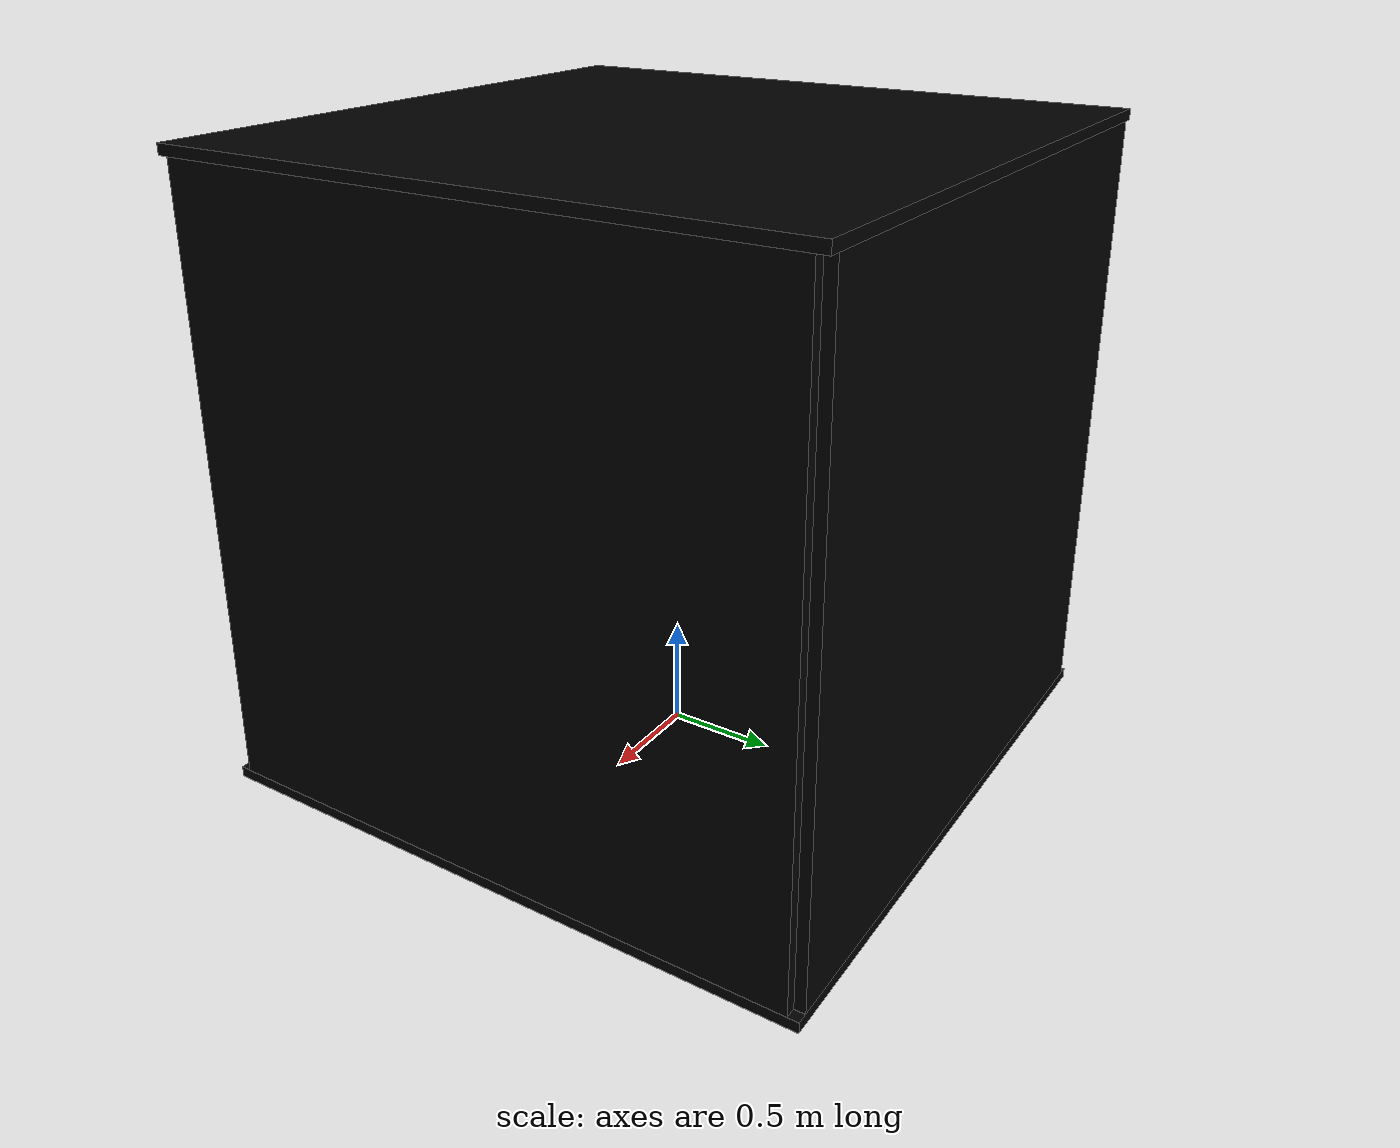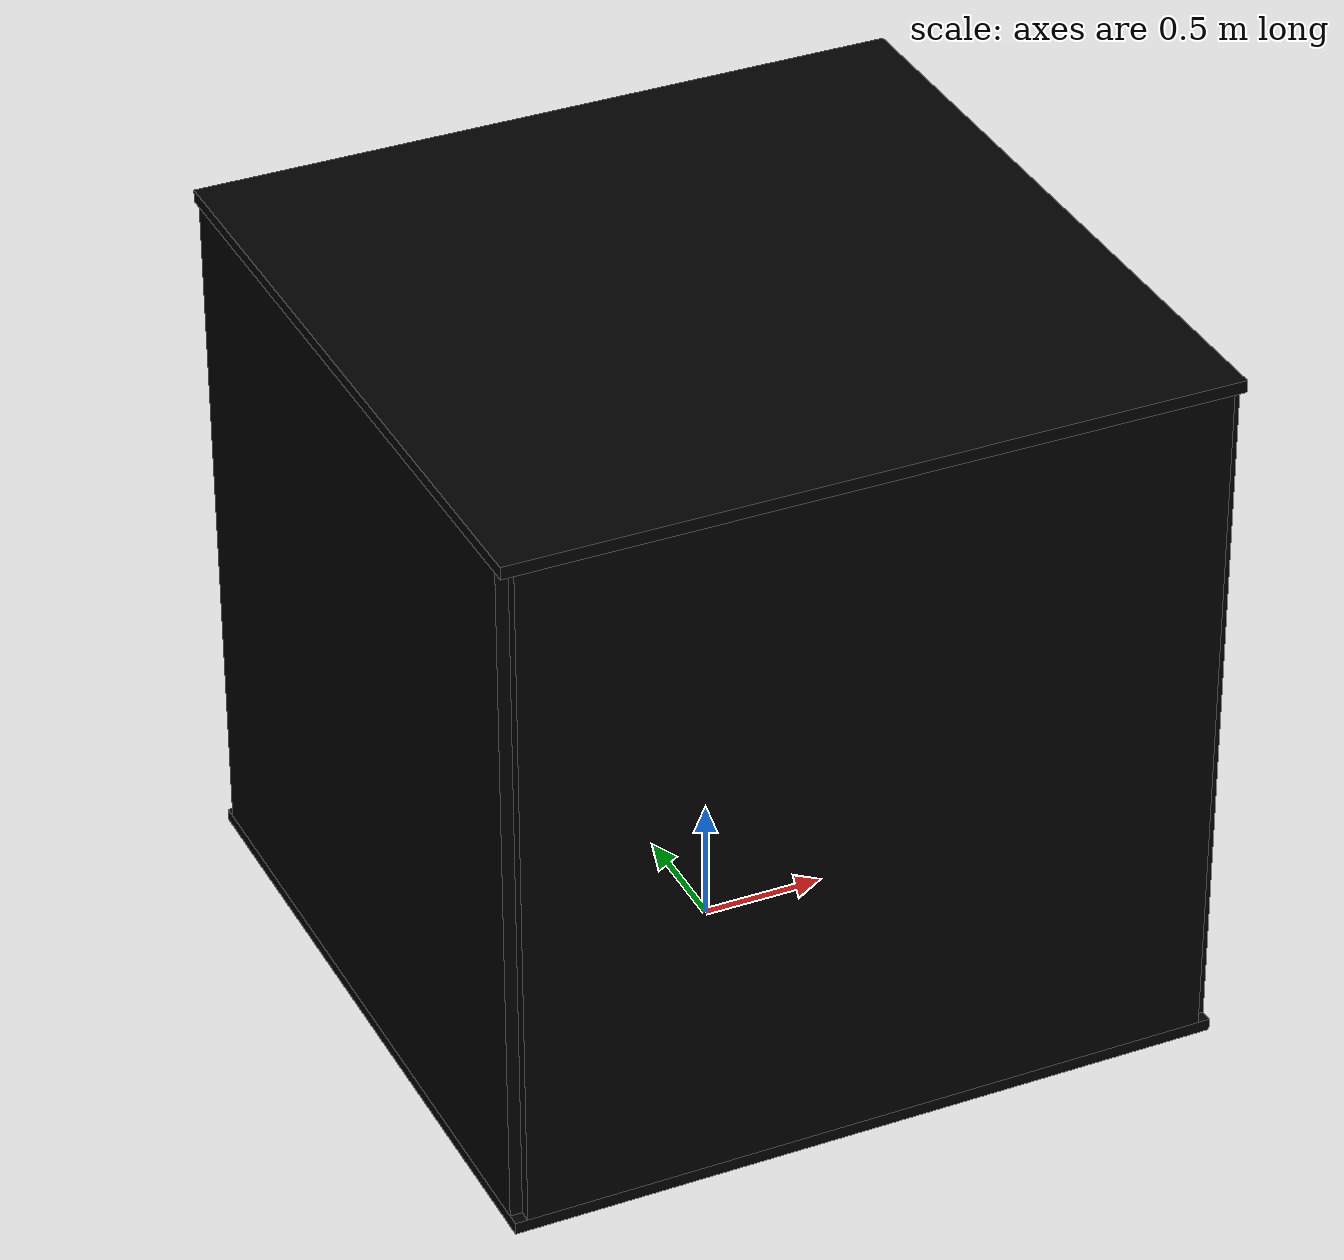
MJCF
<mujoco model="elevated_track"><compiler angle="radian" /><option gravity="0 0 -9.81" timestep=".002" /><visual><global offwidth="768" offheight="768" /><headlight ambient=".5 .5 .5" diffuse=".6 .6 .6" specular="0 0 0" /><map znear=".001" zfar="20" /></visual><asset><material name="darkgray" rgba=".22 .22 .22 1" specular="0" shininess="0" /><material name="black" rgba="0 0 0 1" specular="0" shininess="0" /><mesh name="track_0" vertex="-0.94 0.06 0.98 -0.06 -0.06000000000000005 0.98 -0.94 -0.06000000000000005 0.98 -0.94 0.06 1.0 -0.94 -0.06000000000000005 1.0 -0.06 -0.06000000000000005 1.0 -0.94 0.06 0.98 -0.94 -0.06000000000000005 0.98 -0.94 -0.06000000000000005 1.0 -0.94 0.06 0.98 -0.94 -0.06000000000000005 1.0 -0.94 0.06 1.0 -0.94 -0.06000000000000005 0.98 -0.06 -0.06000000000000005 0.98 -0.06 -0.06000000000000005 1.0 -0.94 -0.06000000000000005 0.98 -0.06 -0.06000000000000005 1.0 -0.94 -0.06000000000000005 1.0 -0.06 -0.06000000000000005 0.98 -0.94 0.06 0.98 -0.94 0.06 1.0 -0.06 -0.06000000000000005 0.98 -0.94 0.06 1.0 -0.06 -0.06000000000000005 1.0" face="0 1 2 3 4 5 6 7 8 9 10 11 12 13 14 15 16 17 18 19 20 21 22 23" normal="0.0 0.0 -1.0 0.0 0.0 -1.0 0.0 0.0 -1.0 0.0 0.0 1.0 0.0 0.0 1.0 0.0 0.0 1.0 -1.0 0.0 0.0 -1.0 0.0 0.0 -1.0 0.0 0.0 -1.0 0.0 0.0 -1.0 0.0 0.0 -1.0 0.0 0.0 0.0 -1.0 0.0 0.0 -1.0 0.0 0.0 -1.0 0.0 0.0 -1.0 0.0 0.0 -1.0 0.0 0.0 -1.0 0.0 0.13511320473331356 0.990830168044299 0.0 0.13511320473331356 0.990830168044299 0.0 0.13511320473331356 0.990830168044299 0.0 0.13511320473331356 0.990830168044299 -0.0 0.13511320473331356 0.990830168044299 -0.0 0.13511320473331356 0.990830168044299 -0.0" /><mesh name="track_1" vertex="-0.06 0.94 0.98 0.06000000000000005 0.06 0.98 -0.06 0.06 0.98 -0.06 0.94 1.0 -0.06 0.06 1.0 0.06000000000000005 0.06 1.0 -0.06 0.94 0.98 -0.06 0.06 0.98 -0.06 0.06 1.0 -0.06 0.94 0.98 -0.06 0.06 1.0 -0.06 0.94 1.0 -0.06 0.06 0.98 0.06000000000000005 0.06 0.98 0.06000000000000005 0.06 1.0 -0.06 0.06 0.98 0.06000000000000005 0.06 1.0 -0.06 0.06 1.0 0.06000000000000005 0.06 0.98 -0.06 0.94 0.98 -0.06 0.94 1.0 0.06000000000000005 0.06 0.98 -0.06 0.94 1.0 0.06000000000000005 0.06 1.0" face="0 1 2 3 4 5 6 7 8 9 10 11 12 13 14 15 16 17 18 19 20 21 22 23" normal="0.0 0.0 -1.0 0.0 0.0 -1.0 0.0 0.0 -1.0 0.0 0.0 1.0 0.0 0.0 1.0 0.0 0.0 1.0 -1.0 0.0 0.0 -1.0 0.0 0.0 -1.0 0.0 0.0 -1.0 0.0 0.0 -1.0 0.0 0.0 -1.0 0.0 0.0 0.0 -1.0 0.0 0.0 -1.0 0.0 0.0 -1.0 0.0 0.0 -1.0 0.0 0.0 -1.0 0.0 0.0 -1.0 0.0 0.990830168044299 0.13511320473331356 0.0 0.990830168044299 0.13511320473331356 0.0 0.990830168044299 0.13511320473331356 0.0 0.990830168044299 0.13511320473331356 -0.0 0.990830168044299 0.13511320473331356 -0.0 0.990830168044299 0.13511320473331356 -0.0" /><mesh name="track_2" vertex="0.06000000000000005 -0.06000000000000005 0.98 0.06000000000000005 0.06 0.98 0.94 -0.06000000000000005 0.98 0.06000000000000005 -0.06000000000000005 1.0 0.94 -0.06000000000000005 1.0 0.06000000000000005 0.06 1.0 0.06000000000000005 -0.06000000000000005 0.98 0.94 -0.06000000000000005 0.98 0.94 -0.06000000000000005 1.0 0.06000000000000005 -0.06000000000000005 0.98 0.94 -0.06000000000000005 1.0 0.06000000000000005 -0.06000000000000005 1.0 0.94 -0.06000000000000005 0.98 0.06000000000000005 0.06 0.98 0.06000000000000005 0.06 1.0 0.94 -0.06000000000000005 0.98 0.06000000000000005 0.06 1.0 0.94 -0.06000000000000005 1.0 0.06000000000000005 0.06 0.98 0.06000000000000005 -0.06000000000000005 0.98 0.06000000000000005 -0.06000000000000005 1.0 0.06000000000000005 0.06 0.98 0.06000000000000005 -0.06000000000000005 1.0 0.06000000000000005 0.06 1.0" face="0 1 2 3 4 5 6 7 8 9 10 11 12 13 14 15 16 17 18 19 20 21 22 23" normal="0.0 0.0 -1.0 0.0 0.0 -1.0 0.0 0.0 -1.0 0.0 0.0 1.0 0.0 0.0 1.0 0.0 0.0 1.0 0.0 -1.0 0.0 0.0 -1.0 0.0 0.0 -1.0 0.0 0.0 -1.0 0.0 0.0 -1.0 0.0 0.0 -1.0 0.0 0.13511320473331356 0.990830168044299 0.0 0.13511320473331356 0.990830168044299 0.0 0.13511320473331356 0.990830168044299 0.0 0.13511320473331356 0.990830168044299 -0.0 0.13511320473331356 0.990830168044299 -0.0 0.13511320473331356 0.990830168044299 -0.0 -1.0 0.0 0.0 -1.0 0.0 0.0 -1.0 0.0 0.0 -1.0 0.0 0.0 -1.0 0.0 0.0 -1.0 0.0 0.0" /><mesh name="track_3" vertex="-0.06 -0.06000000000000005 0.98 0.06000000000000005 -0.06000000000000005 0.98 -0.06 -0.94 0.98 -0.06 -0.06000000000000005 1.0 -0.06 -0.94 1.0 0.06000000000000005 -0.06000000000000005 1.0 -0.06 -0.06000000000000005 0.98 -0.06 -0.94 0.98 -0.06 -0.94 1.0 -0.06 -0.06000000000000005 0.98 -0.06 -0.94 1.0 -0.06 -0.06000000000000005 1.0 -0.06 -0.94 0.98 0.06000000000000005 -0.06000000000000005 0.98 0.06000000000000005 -0.06000000000000005 1.0 -0.06 -0.94 0.98 0.06000000000000005 -0.06000000000000005 1.0 -0.06 -0.94 1.0 0.06000000000000005 -0.06000000000000005 0.98 -0.06 -0.06000000000000005 0.98 -0.06 -0.06000000000000005 1.0 0.06000000000000005 -0.06000000000000005 0.98 -0.06 -0.06000000000000005 1.0 0.06000000000000005 -0.06000000000000005 1.0" face="0 1 2 3 4 5 6 7 8 9 10 11 12 13 14 15 16 17 18 19 20 21 22 23" normal="0.0 0.0 -1.0 0.0 0.0 -1.0 0.0 0.0 -1.0 -0.0 0.0 1.0 -0.0 0.0 1.0 -0.0 0.0 1.0 -1.0 0.0 0.0 -1.0 0.0 0.0 -1.0 0.0 0.0 -1.0 0.0 0.0 -1.0 0.0 0.0 -1.0 0.0 0.0 0.990830168044299 -0.13511320473331356 0.0 0.990830168044299 -0.13511320473331356 0.0 0.990830168044299 -0.13511320473331356 0.0 0.990830168044299 -0.13511320473331356 0.0 0.990830168044299 -0.13511320473331356 0.0 0.990830168044299 -0.13511320473331356 0.0 0.0 1.0 0.0 0.0 1.0 0.0 0.0 1.0 0.0 0.0 1.0 -0.0 0.0 1.0 -0.0 0.0 1.0 -0.0" /><mesh name="track_4" vertex="-0.94 -0.94 0.98 -1.06 -0.95 0.98 -0.94 -0.06000000000000005 0.98 -0.94 -0.94 1.0 -0.94 -0.06000000000000005 1.0 -1.06 -0.95 1.0 -0.94 -0.94 0.98 -0.94 -0.06000000000000005 0.98 -0.94 -0.06000000000000005 1.0 -0.94 -0.94 0.98 -0.94 -0.06000000000000005 1.0 -0.94 -0.94 1.0 -0.94 -0.06000000000000005 0.98 -1.06 -0.95 0.98 -1.06 -0.95 1.0 -0.94 -0.06000000000000005 0.98 -1.06 -0.95 1.0 -0.94 -0.06000000000000005 1.0 -1.06 -0.95 0.98 -0.94 -0.94 0.98 -0.94 -0.94 1.0 -1.06 -0.95 0.98 -0.94 -0.94 1.0 -1.06 -0.95 1.0" face="0 1 2 3 4 5 6 7 8 9 10 11 12 13 14 15 16 17 18 19 20 21 22 23" normal="-0.0 0.0 -1.0 -0.0 0.0 -1.0 -0.0 0.0 -1.0 0.0 -0.0 1.0 0.0 -0.0 1.0 0.0 -0.0 1.0 1.0 0.0 0.0 1.0 0.0 0.0 1.0 0.0 0.0 1.0 0.0 0.0 1.0 0.0 0.0 1.0 0.0 0.0 -0.9910323260599132 0.13362233609796595 0.0 -0.9910323260599132 0.13362233609796595 0.0 -0.9910323260599132 0.13362233609796595 0.0 -0.9910323260599132 0.13362233609796595 0.0 -0.9910323260599132 0.13362233609796595 0.0 -0.9910323260599132 0.13362233609796595 0.0 0.08304547985373997 -0.9965457582448796 0.0 0.08304547985373997 -0.9965457582448796 0.0 0.08304547985373997 -0.9965457582448796 0.0 0.08304547985373997 -0.9965457582448796 0.0 0.08304547985373997 -0.9965457582448796 0.0 0.08304547985373997 -0.9965457582448796 0.0" /><mesh name="track_5" vertex="1.3 1.1875 0.98 0.95 1.06 0.98 1.1875 1.3 0.98 1.3 1.1875 1.0 1.1875 1.3 1.0 0.95 1.06 1.0 1.3 1.1875 0.98 1.1875 1.3 0.98 1.1875 1.3 1.0 1.3 1.1875 0.98 1.1875 1.3 1.0 1.3 1.1875 1.0 1.1875 1.3 0.98 0.95 1.06 0.98 0.95 1.06 1.0 1.1875 1.3 0.98 0.95 1.06 1.0 1.1875 1.3 1.0 0.95 1.06 0.98 1.3 1.1875 0.98 1.3 1.1875 1.0 0.95 1.06 0.98 1.3 1.1875 1.0 0.95 1.06 1.0" face="0 1 2 3 4 5 6 7 8 9 10 11 12 13 14 15 16 17 18 19 20 21 22 23" normal="-0.0 0.0 -1.0 -0.0 0.0 -1.0 -0.0 0.0 -1.0 0.0 0.0 1.0 0.0 0.0 1.0 0.0 0.0 1.0 0.7071067811865476 0.7071067811865476 0.0 0.7071067811865476 0.7071067811865476 0.0 0.7071067811865476 0.7071067811865476 0.0 0.7071067811865476 0.7071067811865476 -0.0 0.7071067811865476 0.7071067811865476 -0.0 0.7071067811865476 0.7071067811865476 -0.0 -0.7107991689516205 0.703395010941708 0.0 -0.7107991689516205 0.703395010941708 0.0 -0.7107991689516205 0.703395010941708 0.0 -0.7107991689516205 0.703395010941708 0.0 -0.7107991689516205 0.703395010941708 0.0 -0.7107991689516205 0.703395010941708 0.0 0.34228187919463066 -0.9395973154362417 0.0 0.34228187919463066 -0.9395973154362417 0.0 0.34228187919463066 -0.9395973154362417 0.0 0.34228187919463066 -0.9395973154362417 0.0 0.34228187919463066 -0.9395973154362417 0.0 0.34228187919463066 -0.9395973154362417 0.0" /><mesh name="track_6" vertex="1.1875 -1.3 0.98 1.06 -0.95 0.98 1.3 -1.1875 0.98 1.1875 -1.3 1.0 1.3 -1.1875 1.0 1.06 -0.95 1.0 1.1875 -1.3 0.98 1.3 -1.1875 0.98 1.3 -1.1875 1.0 1.1875 -1.3 0.98 1.3 -1.1875 1.0 1.1875 -1.3 1.0 1.3 -1.1875 0.98 1.06 -0.95 0.98 1.06 -0.95 1.0 1.3 -1.1875 0.98 1.06 -0.95 1.0 1.3 -1.1875 1.0 1.06 -0.95 0.98 1.1875 -1.3 0.98 1.1875 -1.3 1.0 1.06 -0.95 0.98 1.1875 -1.3 1.0 1.06 -0.95 1.0" face="0 1 2 3 4 5 6 7 8 9 10 11 12 13 14 15 16 17 18 19 20 21 22 23" normal="0.0 0.0 -1.0 0.0 0.0 -1.0 0.0 0.0 -1.0 0.0 -0.0 1.0 0.0 -0.0 1.0 0.0 -0.0 1.0 0.7071067811865476 -0.7071067811865476 0.0 0.7071067811865476 -0.7071067811865476 0.0 0.7071067811865476 -0.7071067811865476 0.0 0.7071067811865476 -0.7071067811865476 0.0 0.7071067811865476 -0.7071067811865476 0.0 0.7071067811865476 -0.7071067811865476 0.0 0.703395010941708 0.7107991689516205 0.0 0.703395010941708 0.7107991689516205 0.0 0.703395010941708 0.7107991689516205 0.0 0.703395010941708 0.7107991689516205 -0.0 0.703395010941708 0.7107991689516205 -0.0 0.703395010941708 0.7107991689516205 -0.0 -0.9395973154362417 -0.34228187919463066 0.0 -0.9395973154362417 -0.34228187919463066 0.0 -0.9395973154362417 -0.34228187919463066 0.0 -0.9395973154362417 -0.34228187919463066 0.0 -0.9395973154362417 -0.34228187919463066 0.0 -0.9395973154362417 -0.34228187919463066 0.0" /><mesh name="track_7" vertex="-1.3 -1.1875 0.98 -0.95 -1.06 0.98 -1.1875 -1.3 0.98 -1.3 -1.1875 1.0 -1.1875 -1.3 1.0 -0.95 -1.06 1.0 -1.3 -1.1875 0.98 -1.1875 -1.3 0.98 -1.1875 -1.3 1.0 -1.3 -1.1875 0.98 -1.1875 -1.3 1.0 -1.3 -1.1875 1.0 -1.1875 -1.3 0.98 -0.95 -1.06 0.98 -0.95 -1.06 1.0 -1.1875 -1.3 0.98 -0.95 -1.06 1.0 -1.1875 -1.3 1.0 -0.95 -1.06 0.98 -1.3 -1.1875 0.98 -1.3 -1.1875 1.0 -0.95 -1.06 0.98 -1.3 -1.1875 1.0 -0.95 -1.06 1.0" face="0 1 2 3 4 5 6 7 8 9 10 11 12 13 14 15 16 17 18 19 20 21 22 23" normal="0.0 0.0 -1.0 0.0 0.0 -1.0 0.0 0.0 -1.0 -0.0 0.0 1.0 -0.0 0.0 1.0 -0.0 0.0 1.0 -0.7071067811865476 -0.7071067811865476 0.0 -0.7071067811865476 -0.7071067811865476 0.0 -0.7071067811865476 -0.7071067811865476 0.0 -0.7071067811865476 -0.7071067811865476 0.0 -0.7071067811865476 -0.7071067811865476 0.0 -0.7071067811865476 -0.7071067811865476 0.0 0.7107991689516205 -0.703395010941708 0.0 0.7107991689516205 -0.703395010941708 0.0 0.7107991689516205 -0.703395010941708 0.0 0.7107991689516205 -0.703395010941708 0.0 0.7107991689516205 -0.703395010941708 0.0 0.7107991689516205 -0.703395010941708 0.0 -0.34228187919463066 0.9395973154362417 0.0 -0.34228187919463066 0.9395973154362417 0.0 -0.34228187919463066 0.9395973154362417 0.0 -0.34228187919463066 0.9395973154362417 0.0 -0.34228187919463066 0.9395973154362417 0.0 -0.34228187919463066 0.9395973154362417 0.0" /><mesh name="track_8" vertex="-1.1875 1.3 0.98 -1.06 0.95 0.98 -1.3 1.1875 0.98 -1.1875 1.3 1.0 -1.3 1.1875 1.0 -1.06 0.95 1.0 -1.1875 1.3 0.98 -1.3 1.1875 0.98 -1.3 1.1875 1.0 -1.1875 1.3 0.98 -1.3 1.1875 1.0 -1.1875 1.3 1.0 -1.3 1.1875 0.98 -1.06 0.95 0.98 -1.06 0.95 1.0 -1.3 1.1875 0.98 -1.06 0.95 1.0 -1.3 1.1875 1.0 -1.06 0.95 0.98 -1.1875 1.3 0.98 -1.1875 1.3 1.0 -1.06 0.95 0.98 -1.1875 1.3 1.0 -1.06 0.95 1.0" face="0 1 2 3 4 5 6 7 8 9 10 11 12 13 14 15 16 17 18 19 20 21 22 23" normal="0.0 -0.0 -1.0 0.0 -0.0 -1.0 0.0 -0.0 -1.0 0.0 0.0 1.0 0.0 0.0 1.0 0.0 0.0 1.0 -0.7071067811865476 0.7071067811865476 0.0 -0.7071067811865476 0.7071067811865476 0.0 -0.7071067811865476 0.7071067811865476 0.0 -0.7071067811865476 0.7071067811865476 0.0 -0.7071067811865476 0.7071067811865476 0.0 -0.7071067811865476 0.7071067811865476 0.0 -0.703395010941708 -0.7107991689516205 0.0 -0.703395010941708 -0.7107991689516205 0.0 -0.703395010941708 -0.7107991689516205 0.0 -0.703395010941708 -0.7107991689516205 0.0 -0.703395010941708 -0.7107991689516205 0.0 -0.703395010941708 -0.7107991689516205 0.0 0.9395973154362417 0.34228187919463066 0.0 0.9395973154362417 0.34228187919463066 0.0 0.9395973154362417 0.34228187919463066 0.0 0.9395973154362417 0.34228187919463066 -0.0 0.9395973154362417 0.34228187919463066 -0.0 0.9395973154362417 0.34228187919463066 -0.0" /><mesh name="track_9" vertex="-0.06 0.06 0.98 -0.06 -0.06000000000000005 0.98 -0.94 0.06 0.98 -0.06 0.06 1.0 -0.94 0.06 1.0 -0.06 -0.06000000000000005 1.0 -0.06 0.06 0.98 -0.94 0.06 0.98 -0.94 0.06 1.0 -0.06 0.06 0.98 -0.94 0.06 1.0 -0.06 0.06 1.0 -0.94 0.06 0.98 -0.06 -0.06000000000000005 0.98 -0.06 -0.06000000000000005 1.0 -0.94 0.06 0.98 -0.06 -0.06000000000000005 1.0 -0.94 0.06 1.0 -0.06 -0.06000000000000005 0.98 -0.06 0.06 0.98 -0.06 0.06 1.0 -0.06 -0.06000000000000005 0.98 -0.06 0.06 1.0 -0.06 -0.06000000000000005 1.0" face="0 1 2 3 4 5 6 7 8 9 10 11 12 13 14 15 16 17 18 19 20 21 22 23" normal="-0.0 -0.0 -1.0 -0.0 -0.0 -1.0 -0.0 -0.0 -1.0 0.0 0.0 1.0 0.0 0.0 1.0 0.0 0.0 1.0 0.0 1.0 0.0 0.0 1.0 0.0 0.0 1.0 0.0 0.0 1.0 -0.0 0.0 1.0 -0.0 0.0 1.0 -0.0 -0.13511320473331356 -0.990830168044299 0.0 -0.13511320473331356 -0.990830168044299 0.0 -0.13511320473331356 -0.990830168044299 0.0 -0.13511320473331356 -0.990830168044299 0.0 -0.13511320473331356 -0.990830168044299 0.0 -0.13511320473331356 -0.990830168044299 0.0 1.0 0.0 0.0 1.0 0.0 0.0 1.0 0.0 0.0 1.0 0.0 0.0 1.0 0.0 0.0 1.0 0.0 0.0" /><mesh name="track_10" vertex="0.94 0.06 0.98 0.94 -0.06000000000000005 0.98 0.06000000000000005 0.06 0.98 0.94 0.06 1.0 0.06000000000000005 0.06 1.0 0.94 -0.06000000000000005 1.0 0.94 0.06 0.98 0.06000000000000005 0.06 0.98 0.06000000000000005 0.06 1.0 0.94 0.06 0.98 0.06000000000000005 0.06 1.0 0.94 0.06 1.0 0.06000000000000005 0.06 0.98 0.94 -0.06000000000000005 0.98 0.94 -0.06000000000000005 1.0 0.06000000000000005 0.06 0.98 0.94 -0.06000000000000005 1.0 0.06000000000000005 0.06 1.0 0.94 -0.06000000000000005 0.98 0.94 0.06 0.98 0.94 0.06 1.0 0.94 -0.06000000000000005 0.98 0.94 0.06 1.0 0.94 -0.06000000000000005 1.0" face="0 1 2 3 4 5 6 7 8 9 10 11 12 13 14 15 16 17 18 19 20 21 22 23" normal="-0.0 -0.0 -1.0 -0.0 -0.0 -1.0 -0.0 -0.0 -1.0 0.0 0.0 1.0 0.0 0.0 1.0 0.0 0.0 1.0 0.0 1.0 0.0 0.0 1.0 0.0 0.0 1.0 0.0 0.0 1.0 -0.0 0.0 1.0 -0.0 0.0 1.0 -0.0 -0.13511320473331356 -0.990830168044299 0.0 -0.13511320473331356 -0.990830168044299 0.0 -0.13511320473331356 -0.990830168044299 0.0 -0.13511320473331356 -0.990830168044299 0.0 -0.13511320473331356 -0.990830168044299 0.0 -0.13511320473331356 -0.990830168044299 0.0 1.0 0.0 0.0 1.0 0.0 0.0 1.0 0.0 0.0 1.0 0.0 0.0 1.0 0.0 0.0 1.0 0.0 0.0" /><mesh name="track_11" vertex="0.06000000000000005 -0.06000000000000005 0.98 -0.06 0.06 0.98 0.06000000000000005 0.06 0.98 0.06000000000000005 -0.06000000000000005 1.0 0.06000000000000005 0.06 1.0 -0.06 0.06 1.0 0.06000000000000005 -0.06000000000000005 0.98 0.06000000000000005 0.06 0.98 0.06000000000000005 0.06 1.0 0.06000000000000005 -0.06000000000000005 0.98 0.06000000000000005 0.06 1.0 0.06000000000000005 -0.06000000000000005 1.0 0.06000000000000005 0.06 0.98 -0.06 0.06 0.98 -0.06 0.06 1.0 0.06000000000000005 0.06 0.98 -0.06 0.06 1.0 0.06000000000000005 0.06 1.0 -0.06 0.06 0.98 0.06000000000000005 -0.06000000000000005 0.98 0.06000000000000005 -0.06000000000000005 1.0 -0.06 0.06 0.98 0.06000000000000005 -0.06000000000000005 1.0 -0.06 0.06 1.0" face="0 1 2 3 4 5 6 7 8 9 10 11 12 13 14 15 16 17 18 19 20 21 22 23" normal="0.0 0.0 -1.0 0.0 0.0 -1.0 0.0 0.0 -1.0 0.0 -0.0 1.0 0.0 -0.0 1.0 0.0 -0.0 1.0 1.0 0.0 0.0 1.0 0.0 0.0 1.0 0.0 0.0 1.0 0.0 0.0 1.0 0.0 0.0 1.0 0.0 0.0 0.0 1.0 0.0 0.0 1.0 0.0 0.0 1.0 0.0 0.0 1.0 -0.0 0.0 1.0 -0.0 0.0 1.0 -0.0 -0.7071067811865476 -0.7071067811865476 0.0 -0.7071067811865476 -0.7071067811865476 0.0 -0.7071067811865476 -0.7071067811865476 0.0 -0.7071067811865476 -0.7071067811865476 0.0 -0.7071067811865476 -0.7071067811865476 0.0 -0.7071067811865476 -0.7071067811865476 0.0" /><mesh name="track_12" vertex="-0.94 -0.06000000000000005 0.98 -1.06 -0.95 0.98 -0.94 0.06 0.98 -0.94 -0.06000000000000005 1.0 -0.94 0.06 1.0 -1.06 -0.95 1.0 -0.94 -0.06000000000000005 0.98 -0.94 0.06 0.98 -0.94 0.06 1.0 -0.94 -0.06000000000000005 0.98 -0.94 0.06 1.0 -0.94 -0.06000000000000005 1.0 -0.94 0.06 0.98 -1.06 -0.95 0.98 -1.06 -0.95 1.0 -0.94 0.06 0.98 -1.06 -0.95 1.0 -0.94 0.06 1.0 -1.06 -0.95 0.98 -0.94 -0.06000000000000005 0.98 -0.94 -0.06000000000000005 1.0 -1.06 -0.95 0.98 -0.94 -0.06000000000000005 1.0 -1.06 -0.95 1.0" face="0 1 2 3 4 5 6 7 8 9 10 11 12 13 14 15 16 17 18 19 20 21 22 23" normal="-0.0 0.0 -1.0 -0.0 0.0 -1.0 -0.0 0.0 -1.0 0.0 -0.0 1.0 0.0 -0.0 1.0 0.0 -0.0 1.0 1.0 0.0 0.0 1.0 0.0 0.0 1.0 0.0 0.0 1.0 0.0 0.0 1.0 0.0 0.0 1.0 0.0 0.0 -0.9930157259561065 0.11798206645023059 0.0 -0.9930157259561065 0.11798206645023059 0.0 -0.9930157259561065 0.11798206645023059 0.0 -0.9930157259561065 0.11798206645023059 0.0 -0.9930157259561065 0.11798206645023059 0.0 -0.9930157259561065 0.11798206645023059 0.0 0.9910323260599132 -0.13362233609796595 0.0 0.9910323260599132 -0.13362233609796595 0.0 0.9910323260599132 -0.13362233609796595 0.0 0.9910323260599132 -0.13362233609796595 0.0 0.9910323260599132 -0.13362233609796595 0.0 0.9910323260599132 -0.13362233609796595 0.0" /><mesh name="track_13" vertex="1.06 0.95 0.98 0.95 1.06 0.98 1.3 1.1875 0.98 1.06 0.95 1.0 1.3 1.1875 1.0 0.95 1.06 1.0 1.06 0.95 0.98 1.3 1.1875 0.98 1.3 1.1875 1.0 1.06 0.95 0.98 1.3 1.1875 1.0 1.06 0.95 1.0 1.3 1.1875 0.98 0.95 1.06 0.98 0.95 1.06 1.0 1.3 1.1875 0.98 0.95 1.06 1.0 1.3 1.1875 1.0 0.95 1.06 0.98 1.06 0.95 0.98 1.06 0.95 1.0 0.95 1.06 0.98 1.06 0.95 1.0 0.95 1.06 1.0" face="0 1 2 3 4 5 6 7 8 9 10 11 12 13 14 15 16 17 18 19 20 21 22 23" normal="0.0 0.0 -1.0 0.0 0.0 -1.0 0.0 0.0 -1.0 0.0 -0.0 1.0 0.0 -0.0 1.0 0.0 -0.0 1.0 0.703395010941708 -0.7107991689516205 0.0 0.703395010941708 -0.7107991689516205 0.0 0.703395010941708 -0.7107991689516205 0.0 0.703395010941708 -0.7107991689516205 0.0 0.703395010941708 -0.7107991689516205 0.0 0.703395010941708 -0.7107991689516205 0.0 -0.34228187919463066 0.9395973154362417 0.0 -0.34228187919463066 0.9395973154362417 0.0 -0.34228187919463066 0.9395973154362417 0.0 -0.34228187919463066 0.9395973154362417 0.0 -0.34228187919463066 0.9395973154362417 0.0 -0.34228187919463066 0.9395973154362417 0.0 -0.7071067811865475 -0.7071067811865475 0.0 -0.7071067811865475 -0.7071067811865475 0.0 -0.7071067811865475 -0.7071067811865475 0.0 -0.7071067811865475 -0.7071067811865475 0.0 -0.7071067811865475 -0.7071067811865475 0.0 -0.7071067811865475 -0.7071067811865475 0.0" /><mesh name="track_14" vertex="0.95 -1.06 0.98 1.06 -0.95 0.98 1.1875 -1.3 0.98 0.95 -1.06 1.0 1.1875 -1.3 1.0 1.06 -0.95 1.0 0.95 -1.06 0.98 1.1875 -1.3 0.98 1.1875 -1.3 1.0 0.95 -1.06 0.98 1.1875 -1.3 1.0 0.95 -1.06 1.0 1.1875 -1.3 0.98 1.06 -0.95 0.98 1.06 -0.95 1.0 1.1875 -1.3 0.98 1.06 -0.95 1.0 1.1875 -1.3 1.0 1.06 -0.95 0.98 0.95 -1.06 0.98 0.95 -1.06 1.0 1.06 -0.95 0.98 0.95 -1.06 1.0 1.06 -0.95 1.0" face="0 1 2 3 4 5 6 7 8 9 10 11 12 13 14 15 16 17 18 19 20 21 22 23" normal="0.0 0.0 -1.0 0.0 0.0 -1.0 0.0 0.0 -1.0 -0.0 0.0 1.0 -0.0 0.0 1.0 -0.0 0.0 1.0 -0.7107991689516205 -0.703395010941708 0.0 -0.7107991689516205 -0.703395010941708 0.0 -0.7107991689516205 -0.703395010941708 0.0 -0.7107991689516205 -0.703395010941708 0.0 -0.7107991689516205 -0.703395010941708 0.0 -0.7107991689516205 -0.703395010941708 0.0 0.9395973154362417 0.34228187919463066 0.0 0.9395973154362417 0.34228187919463066 0.0 0.9395973154362417 0.34228187919463066 0.0 0.9395973154362417 0.34228187919463066 -0.0 0.9395973154362417 0.34228187919463066 -0.0 0.9395973154362417 0.34228187919463066 -0.0 -0.7071067811865475 0.7071067811865475 0.0 -0.7071067811865475 0.7071067811865475 0.0 -0.7071067811865475 0.7071067811865475 0.0 -0.7071067811865475 0.7071067811865475 0.0 -0.7071067811865475 0.7071067811865475 0.0 -0.7071067811865475 0.7071067811865475 0.0" /><mesh name="track_15" vertex="-1.06 -0.95 0.98 -0.95 -1.06 0.98 -1.3 -1.1875 0.98 -1.06 -0.95 1.0 -1.3 -1.1875 1.0 -0.95 -1.06 1.0 -1.06 -0.95 0.98 -1.3 -1.1875 0.98 -1.3 -1.1875 1.0 -1.06 -0.95 0.98 -1.3 -1.1875 1.0 -1.06 -0.95 1.0 -1.3 -1.1875 0.98 -0.95 -1.06 0.98 -0.95 -1.06 1.0 -1.3 -1.1875 0.98 -0.95 -1.06 1.0 -1.3 -1.1875 1.0 -0.95 -1.06 0.98 -1.06 -0.95 0.98 -1.06 -0.95 1.0 -0.95 -1.06 0.98 -1.06 -0.95 1.0 -0.95 -1.06 1.0" face="0 1 2 3 4 5 6 7 8 9 10 11 12 13 14 15 16 17 18 19 20 21 22 23" normal="0.0 -0.0 -1.0 0.0 -0.0 -1.0 0.0 -0.0 -1.0 0.0 0.0 1.0 0.0 0.0 1.0 0.0 0.0 1.0 -0.703395010941708 0.7107991689516205 0.0 -0.703395010941708 0.7107991689516205 0.0 -0.703395010941708 0.7107991689516205 0.0 -0.703395010941708 0.7107991689516205 0.0 -0.703395010941708 0.7107991689516205 0.0 -0.703395010941708 0.7107991689516205 0.0 0.34228187919463066 -0.9395973154362417 0.0 0.34228187919463066 -0.9395973154362417 0.0 0.34228187919463066 -0.9395973154362417 0.0 0.34228187919463066 -0.9395973154362417 0.0 0.34228187919463066 -0.9395973154362417 0.0 0.34228187919463066 -0.9395973154362417 0.0 0.7071067811865475 0.7071067811865475 0.0 0.7071067811865475 0.7071067811865475 0.0 0.7071067811865475 0.7071067811865475 0.0 0.7071067811865475 0.7071067811865475 -0.0 0.7071067811865475 0.7071067811865475 -0.0 0.7071067811865475 0.7071067811865475 -0.0" /><mesh name="track_16" vertex="-0.95 1.06 0.98 -1.06 0.95 0.98 -1.1875 1.3 0.98 -0.95 1.06 1.0 -1.1875 1.3 1.0 -1.06 0.95 1.0 -0.95 1.06 0.98 -1.1875 1.3 0.98 -1.1875 1.3 1.0 -0.95 1.06 0.98 -1.1875 1.3 1.0 -0.95 1.06 1.0 -1.1875 1.3 0.98 -1.06 0.95 0.98 -1.06 0.95 1.0 -1.1875 1.3 0.98 -1.06 0.95 1.0 -1.1875 1.3 1.0 -1.06 0.95 0.98 -0.95 1.06 0.98 -0.95 1.06 1.0 -1.06 0.95 0.98 -0.95 1.06 1.0 -1.06 0.95 1.0" face="0 1 2 3 4 5 6 7 8 9 10 11 12 13 14 15 16 17 18 19 20 21 22 23" normal="-0.0 0.0 -1.0 -0.0 0.0 -1.0 -0.0 0.0 -1.0 0.0 0.0 1.0 0.0 0.0 1.0 0.0 0.0 1.0 0.7107991689516205 0.703395010941708 0.0 0.7107991689516205 0.703395010941708 0.0 0.7107991689516205 0.703395010941708 0.0 0.7107991689516205 0.703395010941708 -0.0 0.7107991689516205 0.703395010941708 -0.0 0.7107991689516205 0.703395010941708 -0.0 -0.9395973154362417 -0.34228187919463066 0.0 -0.9395973154362417 -0.34228187919463066 0.0 -0.9395973154362417 -0.34228187919463066 0.0 -0.9395973154362417 -0.34228187919463066 0.0 -0.9395973154362417 -0.34228187919463066 0.0 -0.9395973154362417 -0.34228187919463066 0.0 0.7071067811865475 -0.7071067811865475 0.0 0.7071067811865475 -0.7071067811865475 0.0 0.7071067811865475 -0.7071067811865475 0.0 0.7071067811865475 -0.7071067811865475 0.0 0.7071067811865475 -0.7071067811865475 0.0 0.7071067811865475 -0.7071067811865475 0.0" /><mesh name="track_17" vertex="-0.06 0.06 0.98 0.06000000000000005 -0.06000000000000005 0.98 -0.06 -0.06000000000000005 0.98 -0.06 0.06 1.0 -0.06 -0.06000000000000005 1.0 0.06000000000000005 -0.06000000000000005 1.0 -0.06 0.06 0.98 -0.06 -0.06000000000000005 0.98 -0.06 -0.06000000000000005 1.0 -0.06 0.06 0.98 -0.06 -0.06000000000000005 1.0 -0.06 0.06 1.0 -0.06 -0.06000000000000005 0.98 0.06000000000000005 -0.06000000000000005 0.98 0.06000000000000005 -0.06000000000000005 1.0 -0.06 -0.06000000000000005 0.98 0.06000000000000005 -0.06000000000000005 1.0 -0.06 -0.06000000000000005 1.0 0.06000000000000005 -0.06000000000000005 0.98 -0.06 0.06 0.98 -0.06 0.06 1.0 0.06000000000000005 -0.06000000000000005 0.98 -0.06 0.06 1.0 0.06000000000000005 -0.06000000000000005 1.0" face="0 1 2 3 4 5 6 7 8 9 10 11 12 13 14 15 16 17 18 19 20 21 22 23" normal="0.0 0.0 -1.0 0.0 0.0 -1.0 0.0 0.0 -1.0 0.0 0.0 1.0 0.0 0.0 1.0 0.0 0.0 1.0 -1.0 0.0 0.0 -1.0 0.0 0.0 -1.0 0.0 0.0 -1.0 0.0 0.0 -1.0 0.0 0.0 -1.0 0.0 0.0 0.0 -1.0 0.0 0.0 -1.0 0.0 0.0 -1.0 0.0 0.0 -1.0 0.0 0.0 -1.0 0.0 0.0 -1.0 0.0 0.7071067811865476 0.7071067811865476 0.0 0.7071067811865476 0.7071067811865476 0.0 0.7071067811865476 0.7071067811865476 0.0 0.7071067811865476 0.7071067811865476 -0.0 0.7071067811865476 0.7071067811865476 -0.0 0.7071067811865476 0.7071067811865476 -0.0" /><mesh name="track_18" vertex="-0.06 0.94 0.98 0.06000000000000005 0.94 0.98 0.06000000000000005 0.06 0.98 -0.06 0.94 1.0 0.06000000000000005 0.06 1.0 0.06000000000000005 0.94 1.0 -0.06 0.94 0.98 0.06000000000000005 0.06 0.98 0.06000000000000005 0.06 1.0 -0.06 0.94 0.98 0.06000000000000005 0.06 1.0 -0.06 0.94 1.0 0.06000000000000005 0.06 0.98 0.06000000000000005 0.94 0.98 0.06000000000000005 0.94 1.0 0.06000000000000005 0.06 0.98 0.06000000000000005 0.94 1.0 0.06000000000000005 0.06 1.0 0.06000000000000005 0.94 0.98 -0.06 0.94 0.98 -0.06 0.94 1.0 0.06000000000000005 0.94 0.98 -0.06 0.94 1.0 0.06000000000000005 0.94 1.0" face="0 1 2 3 4 5 6 7 8 9 10 11 12 13 14 15 16 17 18 19 20 21 22 23" normal="0.0 0.0 -1.0 0.0 0.0 -1.0 0.0 0.0 -1.0 -0.0 0.0 1.0 -0.0 0.0 1.0 -0.0 0.0 1.0 -0.990830168044299 -0.13511320473331356 0.0 -0.990830168044299 -0.13511320473331356 0.0 -0.990830168044299 -0.13511320473331356 0.0 -0.990830168044299 -0.13511320473331356 0.0 -0.990830168044299 -0.13511320473331356 0.0 -0.990830168044299 -0.13511320473331356 0.0 1.0 0.0 0.0 1.0 0.0 0.0 1.0 0.0 0.0 1.0 0.0 0.0 1.0 0.0 0.0 1.0 0.0 0.0 0.0 1.0 0.0 0.0 1.0 0.0 0.0 1.0 0.0 0.0 1.0 -0.0 0.0 1.0 -0.0 0.0 1.0 -0.0" /><mesh name="track_19" vertex="-0.94 0.06 0.98 -1.06 0.95 0.98 -0.94 0.94 0.98 -0.94 0.06 1.0 -0.94 0.94 1.0 -1.06 0.95 1.0 -0.94 0.06 0.98 -0.94 0.94 0.98 -0.94 0.94 1.0 -0.94 0.06 0.98 -0.94 0.94 1.0 -0.94 0.06 1.0 -0.94 0.94 0.98 -1.06 0.95 0.98 -1.06 0.95 1.0 -0.94 0.94 0.98 -1.06 0.95 1.0 -0.94 0.94 1.0 -1.06 0.95 0.98 -0.94 0.06 0.98 -0.94 0.06 1.0 -1.06 0.95 0.98 -0.94 0.06 1.0 -1.06 0.95 1.0" face="0 1 2 3 4 5 6 7 8 9 10 11 12 13 14 15 16 17 18 19 20 21 22 23" normal="0.0 0.0 -1.0 0.0 0.0 -1.0 0.0 0.0 -1.0 0.0 -0.0 1.0 0.0 -0.0 1.0 0.0 -0.0 1.0 1.0 0.0 0.0 1.0 0.0 0.0 1.0 0.0 0.0 1.0 0.0 0.0 1.0 0.0 0.0 1.0 0.0 0.0 0.08304547985373997 0.9965457582448796 0.0 0.08304547985373997 0.9965457582448796 0.0 0.08304547985373997 0.9965457582448796 0.0 0.08304547985373997 0.9965457582448796 -0.0 0.08304547985373997 0.9965457582448796 -0.0 0.08304547985373997 0.9965457582448796 -0.0 -0.9910323260599132 -0.13362233609796595 0.0 -0.9910323260599132 -0.13362233609796595 0.0 -0.9910323260599132 -0.13362233609796595 0.0 -0.9910323260599132 -0.13362233609796595 0.0 -0.9910323260599132 -0.13362233609796595 0.0 -0.9910323260599132 -0.13362233609796595 0.0" /><mesh name="track_20" vertex="1.06 0.95 0.98 0.94 0.94 0.98 0.95 1.06 0.98 1.06 0.95 1.0 0.95 1.06 1.0 0.94 0.94 1.0 1.06 0.95 0.98 0.95 1.06 0.98 0.95 1.06 1.0 1.06 0.95 0.98 0.95 1.06 1.0 1.06 0.95 1.0 0.95 1.06 0.98 0.94 0.94 0.98 0.94 0.94 1.0 0.95 1.06 0.98 0.94 0.94 1.0 0.95 1.06 1.0 0.94 0.94 0.98 1.06 0.95 0.98 1.06 0.95 1.0 0.94 0.94 0.98 1.06 0.95 1.0 0.94 0.94 1.0" face="0 1 2 3 4 5 6 7 8 9 10 11 12 13 14 15 16 17 18 19 20 21 22 23" normal="-0.0 0.0 -1.0 -0.0 0.0 -1.0 -0.0 0.0 -1.0 0.0 0.0 1.0 0.0 0.0 1.0 0.0 0.0 1.0 0.7071067811865475 0.7071067811865475 0.0 0.7071067811865475 0.7071067811865475 0.0 0.7071067811865475 0.7071067811865475 0.0 0.7071067811865475 0.7071067811865475 -0.0 0.7071067811865475 0.7071067811865475 -0.0 0.7071067811865475 0.7071067811865475 -0.0 -0.9965457582448796 0.08304547985373997 0.0 -0.9965457582448796 0.08304547985373997 0.0 -0.9965457582448796 0.08304547985373997 0.0 -0.9965457582448796 0.08304547985373997 0.0 -0.9965457582448796 0.08304547985373997 0.0 -0.9965457582448796 0.08304547985373997 0.0 0.08304547985373997 -0.9965457582448796 0.0 0.08304547985373997 -0.9965457582448796 0.0 0.08304547985373997 -0.9965457582448796 0.0 0.08304547985373997 -0.9965457582448796 0.0 0.08304547985373997 -0.9965457582448796 0.0 0.08304547985373997 -0.9965457582448796 0.0" /><mesh name="track_21" vertex="0.95 -1.06 0.98 0.94 -0.94 0.98 1.06 -0.95 0.98 0.95 -1.06 1.0 1.06 -0.95 1.0 0.94 -0.94 1.0 0.95 -1.06 0.98 1.06 -0.95 0.98 1.06 -0.95 1.0 0.95 -1.06 0.98 1.06 -0.95 1.0 0.95 -1.06 1.0 1.06 -0.95 0.98 0.94 -0.94 0.98 0.94 -0.94 1.0 1.06 -0.95 0.98 0.94 -0.94 1.0 1.06 -0.95 1.0 0.94 -0.94 0.98 0.95 -1.06 0.98 0.95 -1.06 1.0 0.94 -0.94 0.98 0.95 -1.06 1.0 0.94 -0.94 1.0" face="0 1 2 3 4 5 6 7 8 9 10 11 12 13 14 15 16 17 18 19 20 21 22 23" normal="0.0 0.0 -1.0 0.0 0.0 -1.0 0.0 0.0 -1.0 0.0 -0.0 1.0 0.0 -0.0 1.0 0.0 -0.0 1.0 0.7071067811865475 -0.7071067811865475 0.0 0.7071067811865475 -0.7071067811865475 0.0 0.7071067811865475 -0.7071067811865475 0.0 0.7071067811865475 -0.7071067811865475 0.0 0.7071067811865475 -0.7071067811865475 0.0 0.7071067811865475 -0.7071067811865475 0.0 0.08304547985373997 0.9965457582448796 0.0 0.08304547985373997 0.9965457582448796 0.0 0.08304547985373997 0.9965457582448796 0.0 0.08304547985373997 0.9965457582448796 -0.0 0.08304547985373997 0.9965457582448796 -0.0 0.08304547985373997 0.9965457582448796 -0.0 -0.9965457582448796 -0.08304547985373997 0.0 -0.9965457582448796 -0.08304547985373997 0.0 -0.9965457582448796 -0.08304547985373997 0.0 -0.9965457582448796 -0.08304547985373997 0.0 -0.9965457582448796 -0.08304547985373997 0.0 -0.9965457582448796 -0.08304547985373997 0.0" /><mesh name="track_22" vertex="-1.06 -0.95 0.98 -0.94 -0.94 0.98 -0.95 -1.06 0.98 -1.06 -0.95 1.0 -0.95 -1.06 1.0 -0.94 -0.94 1.0 -1.06 -0.95 0.98 -0.95 -1.06 0.98 -0.95 -1.06 1.0 -1.06 -0.95 0.98 -0.95 -1.06 1.0 -1.06 -0.95 1.0 -0.95 -1.06 0.98 -0.94 -0.94 0.98 -0.94 -0.94 1.0 -0.95 -1.06 0.98 -0.94 -0.94 1.0 -0.95 -1.06 1.0 -0.94 -0.94 0.98 -1.06 -0.95 0.98 -1.06 -0.95 1.0 -0.94 -0.94 0.98 -1.06 -0.95 1.0 -0.94 -0.94 1.0" face="0 1 2 3 4 5 6 7 8 9 10 11 12 13 14 15 16 17 18 19 20 21 22 23" normal="0.0 0.0 -1.0 0.0 0.0 -1.0 0.0 0.0 -1.0 -0.0 0.0 1.0 -0.0 0.0 1.0 -0.0 0.0 1.0 -0.7071067811865475 -0.7071067811865475 0.0 -0.7071067811865475 -0.7071067811865475 0.0 -0.7071067811865475 -0.7071067811865475 0.0 -0.7071067811865475 -0.7071067811865475 0.0 -0.7071067811865475 -0.7071067811865475 0.0 -0.7071067811865475 -0.7071067811865475 0.0 0.9965457582448796 -0.08304547985373997 0.0 0.9965457582448796 -0.08304547985373997 0.0 0.9965457582448796 -0.08304547985373997 0.0 0.9965457582448796 -0.08304547985373997 0.0 0.9965457582448796 -0.08304547985373997 0.0 0.9965457582448796 -0.08304547985373997 0.0 -0.08304547985373997 0.9965457582448796 0.0 -0.08304547985373997 0.9965457582448796 0.0 -0.08304547985373997 0.9965457582448796 0.0 -0.08304547985373997 0.9965457582448796 0.0 -0.08304547985373997 0.9965457582448796 0.0 -0.08304547985373997 0.9965457582448796 0.0" /><mesh name="track_23" vertex="-0.95 1.06 0.98 -0.94 0.94 0.98 -1.06 0.95 0.98 -0.95 1.06 1.0 -1.06 0.95 1.0 -0.94 0.94 1.0 -0.95 1.06 0.98 -1.06 0.95 0.98 -1.06 0.95 1.0 -0.95 1.06 0.98 -1.06 0.95 1.0 -0.95 1.06 1.0 -1.06 0.95 0.98 -0.94 0.94 0.98 -0.94 0.94 1.0 -1.06 0.95 0.98 -0.94 0.94 1.0 -1.06 0.95 1.0 -0.94 0.94 0.98 -0.95 1.06 0.98 -0.95 1.06 1.0 -0.94 0.94 0.98 -0.95 1.06 1.0 -0.94 0.94 1.0" face="0 1 2 3 4 5 6 7 8 9 10 11 12 13 14 15 16 17 18 19 20 21 22 23" normal="0.0 -0.0 -1.0 0.0 -0.0 -1.0 0.0 -0.0 -1.0 0.0 0.0 1.0 0.0 0.0 1.0 0.0 0.0 1.0 -0.7071067811865475 0.7071067811865475 0.0 -0.7071067811865475 0.7071067811865475 0.0 -0.7071067811865475 0.7071067811865475 0.0 -0.7071067811865475 0.7071067811865475 0.0 -0.7071067811865475 0.7071067811865475 0.0 -0.7071067811865475 0.7071067811865475 0.0 -0.08304547985373997 -0.9965457582448796 0.0 -0.08304547985373997 -0.9965457582448796 0.0 -0.08304547985373997 -0.9965457582448796 0.0 -0.08304547985373997 -0.9965457582448796 0.0 -0.08304547985373997 -0.9965457582448796 0.0 -0.08304547985373997 -0.9965457582448796 0.0 0.9965457582448796 0.08304547985373997 0.0 0.9965457582448796 0.08304547985373997 0.0 0.9965457582448796 0.08304547985373997 0.0 0.9965457582448796 0.08304547985373997 -0.0 0.9965457582448796 0.08304547985373997 -0.0 0.9965457582448796 0.08304547985373997 -0.0" /><mesh name="track_24" vertex="0.06000000000000005 -0.94 0.98 -0.06 -0.94 0.98 0.06000000000000005 -0.06000000000000005 0.98 0.06000000000000005 -0.94 1.0 0.06000000000000005 -0.06000000000000005 1.0 -0.06 -0.94 1.0 0.06000000000000005 -0.94 0.98 0.06000000000000005 -0.06000000000000005 0.98 0.06000000000000005 -0.06000000000000005 1.0 0.06000000000000005 -0.94 0.98 0.06000000000000005 -0.06000000000000005 1.0 0.06000000000000005 -0.94 1.0 0.06000000000000005 -0.06000000000000005 0.98 -0.06 -0.94 0.98 -0.06 -0.94 1.0 0.06000000000000005 -0.06000000000000005 0.98 -0.06 -0.94 1.0 0.06000000000000005 -0.06000000000000005 1.0 -0.06 -0.94 0.98 0.06000000000000005 -0.94 0.98 0.06000000000000005 -0.94 1.0 -0.06 -0.94 0.98 0.06000000000000005 -0.94 1.0 -0.06 -0.94 1.0" face="0 1 2 3 4 5 6 7 8 9 10 11 12 13 14 15 16 17 18 19 20 21 22 23" normal="0.0 0.0 -1.0 0.0 0.0 -1.0 0.0 0.0 -1.0 0.0 -0.0 1.0 0.0 -0.0 1.0 0.0 -0.0 1.0 1.0 0.0 0.0 1.0 0.0 0.0 1.0 0.0 0.0 1.0 0.0 0.0 1.0 0.0 0.0 1.0 0.0 0.0 -0.990830168044299 0.13511320473331356 0.0 -0.990830168044299 0.13511320473331356 0.0 -0.990830168044299 0.13511320473331356 0.0 -0.990830168044299 0.13511320473331356 0.0 -0.990830168044299 0.13511320473331356 0.0 -0.990830168044299 0.13511320473331356 0.0 0.0 -1.0 0.0 0.0 -1.0 0.0 0.0 -1.0 0.0 0.0 -1.0 0.0 0.0 -1.0 0.0 0.0 -1.0 0.0" /><mesh name="track_25" vertex="-0.95 1.06 0.98 -0.06 0.94 0.98 -0.94 0.94 0.98 -0.95 1.06 1.0 -0.94 0.94 1.0 -0.06 0.94 1.0 -0.95 1.06 0.98 -0.94 0.94 0.98 -0.94 0.94 1.0 -0.95 1.06 0.98 -0.94 0.94 1.0 -0.95 1.06 1.0 -0.94 0.94 0.98 -0.06 0.94 0.98 -0.06 0.94 1.0 -0.94 0.94 0.98 -0.06 0.94 1.0 -0.94 0.94 1.0 -0.06 0.94 0.98 -0.95 1.06 0.98 -0.95 1.06 1.0 -0.06 0.94 0.98 -0.95 1.06 1.0 -0.06 0.94 1.0" face="0 1 2 3 4 5 6 7 8 9 10 11 12 13 14 15 16 17 18 19 20 21 22 23" normal="0.0 0.0 -1.0 0.0 0.0 -1.0 0.0 0.0 -1.0 0.0 0.0 1.0 0.0 0.0 1.0 0.0 0.0 1.0 -0.9965457582448796 -0.08304547985373997 0.0 -0.9965457582448796 -0.08304547985373997 0.0 -0.9965457582448796 -0.08304547985373997 0.0 -0.9965457582448796 -0.08304547985373997 0.0 -0.9965457582448796 -0.08304547985373997 0.0 -0.9965457582448796 -0.08304547985373997 0.0 0.0 -1.0 0.0 0.0 -1.0 0.0 0.0 -1.0 0.0 0.0 -1.0 0.0 0.0 -1.0 0.0 0.0 -1.0 0.0 0.13362233609796595 0.9910323260599132 0.0 0.13362233609796595 0.9910323260599132 0.0 0.13362233609796595 0.9910323260599132 0.0 0.13362233609796595 0.9910323260599132 -0.0 0.13362233609796595 0.9910323260599132 -0.0 0.13362233609796595 0.9910323260599132 -0.0" /><mesh name="track_26" vertex="-1.06 -0.95 0.98 -1.06 0.95 0.98 -0.94 0.06 0.98 -1.06 -0.95 1.0 -0.94 0.06 1.0 -1.06 0.95 1.0 -1.06 -0.95 0.98 -0.94 0.06 0.98 -0.94 0.06 1.0 -1.06 -0.95 0.98 -0.94 0.06 1.0 -1.06 -0.95 1.0 -0.94 0.06 0.98 -1.06 0.95 0.98 -1.06 0.95 1.0 -0.94 0.06 0.98 -1.06 0.95 1.0 -0.94 0.06 1.0 -1.06 0.95 0.98 -1.06 -0.95 0.98 -1.06 -0.95 1.0 -1.06 0.95 0.98 -1.06 -0.95 1.0 -1.06 0.95 1.0" face="0 1 2 3 4 5 6 7 8 9 10 11 12 13 14 15 16 17 18 19 20 21 22 23" normal="0.0 0.0 -1.0 0.0 0.0 -1.0 0.0 0.0 -1.0 0.0 0.0 1.0 0.0 0.0 1.0 0.0 0.0 1.0 0.9930157259561065 -0.11798206645023059 0.0 0.9930157259561065 -0.11798206645023059 0.0 0.9930157259561065 -0.11798206645023059 0.0 0.9930157259561065 -0.11798206645023059 0.0 0.9930157259561065 -0.11798206645023059 0.0 0.9930157259561065 -0.11798206645023059 0.0 0.9910323260599132 0.13362233609796595 0.0 0.9910323260599132 0.13362233609796595 0.0 0.9910323260599132 0.13362233609796595 0.0 0.9910323260599132 0.13362233609796595 -0.0 0.9910323260599132 0.13362233609796595 -0.0 0.9910323260599132 0.13362233609796595 -0.0 -1.0 0.0 0.0 -1.0 0.0 0.0 -1.0 0.0 0.0 -1.0 0.0 0.0 -1.0 0.0 0.0 -1.0 0.0 0.0" /><mesh name="track_27" vertex="-0.95 1.06 0.98 0.95 1.06 0.98 -0.06 0.94 0.98 -0.95 1.06 1.0 -0.06 0.94 1.0 0.95 1.06 1.0 -0.95 1.06 0.98 -0.06 0.94 0.98 -0.06 0.94 1.0 -0.95 1.06 0.98 -0.06 0.94 1.0 -0.95 1.06 1.0 -0.06 0.94 0.98 0.95 1.06 0.98 0.95 1.06 1.0 -0.06 0.94 0.98 0.95 1.06 1.0 -0.06 0.94 1.0 0.95 1.06 0.98 -0.95 1.06 0.98 -0.95 1.06 1.0 0.95 1.06 0.98 -0.95 1.06 1.0 0.95 1.06 1.0" face="0 1 2 3 4 5 6 7 8 9 10 11 12 13 14 15 16 17 18 19 20 21 22 23" normal="0.0 0.0 -1.0 0.0 0.0 -1.0 0.0 0.0 -1.0 -0.0 0.0 1.0 -0.0 0.0 1.0 -0.0 0.0 1.0 -0.13362233609796595 -0.9910323260599132 0.0 -0.13362233609796595 -0.9910323260599132 0.0 -0.13362233609796595 -0.9910323260599132 0.0 -0.13362233609796595 -0.9910323260599132 0.0 -0.13362233609796595 -0.9910323260599132 0.0 -0.13362233609796595 -0.9910323260599132 0.0 0.11798206645023059 -0.9930157259561065 0.0 0.11798206645023059 -0.9930157259561065 0.0 0.11798206645023059 -0.9930157259561065 0.0 0.11798206645023059 -0.9930157259561065 0.0 0.11798206645023059 -0.9930157259561065 0.0 0.11798206645023059 -0.9930157259561065 0.0 0.0 1.0 0.0 0.0 1.0 0.0 0.0 1.0 0.0 0.0 1.0 -0.0 0.0 1.0 -0.0 0.0 1.0 -0.0" /><mesh name="track_28" vertex="-0.94 -0.94 0.98 -0.06 -0.94 0.98 -0.95 -1.06 0.98 -0.94 -0.94 1.0 -0.95 -1.06 1.0 -0.06 -0.94 1.0 -0.94 -0.94 0.98 -0.95 -1.06 0.98 -0.95 -1.06 1.0 -0.94 -0.94 0.98 -0.95 -1.06 1.0 -0.94 -0.94 1.0 -0.95 -1.06 0.98 -0.06 -0.94 0.98 -0.06 -0.94 1.0 -0.95 -1.06 0.98 -0.06 -0.94 1.0 -0.95 -1.06 1.0 -0.06 -0.94 0.98 -0.94 -0.94 0.98 -0.94 -0.94 1.0 -0.06 -0.94 0.98 -0.94 -0.94 1.0 -0.06 -0.94 1.0" face="0 1 2 3 4 5 6 7 8 9 10 11 12 13 14 15 16 17 18 19 20 21 22 23" normal="0.0 -0.0 -1.0 0.0 -0.0 -1.0 0.0 -0.0 -1.0 -0.0 0.0 1.0 -0.0 0.0 1.0 -0.0 0.0 1.0 -0.9965457582448796 0.08304547985373997 0.0 -0.9965457582448796 0.08304547985373997 0.0 -0.9965457582448796 0.08304547985373997 0.0 -0.9965457582448796 0.08304547985373997 0.0 -0.9965457582448796 0.08304547985373997 0.0 -0.9965457582448796 0.08304547985373997 0.0 0.13362233609796595 -0.9910323260599132 0.0 0.13362233609796595 -0.9910323260599132 0.0 0.13362233609796595 -0.9910323260599132 0.0 0.13362233609796595 -0.9910323260599132 0.0 0.13362233609796595 -0.9910323260599132 0.0 0.13362233609796595 -0.9910323260599132 0.0 0.0 1.0 0.0 0.0 1.0 0.0 0.0 1.0 0.0 0.0 1.0 -0.0 0.0 1.0 -0.0 0.0 1.0 -0.0" /><mesh name="track_29" vertex="0.06000000000000005 0.94 0.98 -0.06 0.94 0.98 0.95 1.06 0.98 0.06000000000000005 0.94 1.0 0.95 1.06 1.0 -0.06 0.94 1.0 0.06000000000000005 0.94 0.98 0.95 1.06 0.98 0.95 1.06 1.0 0.06000000000000005 0.94 0.98 0.95 1.06 1.0 0.06000000000000005 0.94 1.0 0.95 1.06 0.98 -0.06 0.94 0.98 -0.06 0.94 1.0 0.95 1.06 0.98 -0.06 0.94 1.0 0.95 1.06 1.0 -0.06 0.94 0.98 0.06000000000000005 0.94 0.98 0.06000000000000005 0.94 1.0 -0.06 0.94 0.98 0.06000000000000005 0.94 1.0 -0.06 0.94 1.0" face="0 1 2 3 4 5 6 7 8 9 10 11 12 13 14 15 16 17 18 19 20 21 22 23" normal="0.0 0.0 -1.0 0.0 0.0 -1.0 0.0 0.0 -1.0 0.0 -0.0 1.0 0.0 -0.0 1.0 0.0 -0.0 1.0 0.13362233609796595 -0.9910323260599132 0.0 0.13362233609796595 -0.9910323260599132 0.0 0.13362233609796595 -0.9910323260599132 0.0 0.13362233609796595 -0.9910323260599132 0.0 0.13362233609796595 -0.9910323260599132 0.0 0.13362233609796595 -0.9910323260599132 0.0 -0.11798206645023059 0.9930157259561065 0.0 -0.11798206645023059 0.9930157259561065 0.0 -0.11798206645023059 0.9930157259561065 0.0 -0.11798206645023059 0.9930157259561065 0.0 -0.11798206645023059 0.9930157259561065 0.0 -0.11798206645023059 0.9930157259561065 0.0 0.0 -1.0 0.0 0.0 -1.0 0.0 0.0 -1.0 0.0 0.0 -1.0 0.0 0.0 -1.0 0.0 0.0 -1.0 0.0" /><mesh name="track_30" vertex="0.95 -1.06 0.98 -0.95 -1.06 0.98 -0.06 -0.94 0.98 0.95 -1.06 1.0 -0.06 -0.94 1.0 -0.95 -1.06 1.0 0.95 -1.06 0.98 -0.06 -0.94 0.98 -0.06 -0.94 1.0 0.95 -1.06 0.98 -0.06 -0.94 1.0 0.95 -1.06 1.0 -0.06 -0.94 0.98 -0.95 -1.06 0.98 -0.95 -1.06 1.0 -0.06 -0.94 0.98 -0.95 -1.06 1.0 -0.06 -0.94 1.0 -0.95 -1.06 0.98 0.95 -1.06 0.98 0.95 -1.06 1.0 -0.95 -1.06 0.98 0.95 -1.06 1.0 -0.95 -1.06 1.0" face="0 1 2 3 4 5 6 7 8 9 10 11 12 13 14 15 16 17 18 19 20 21 22 23" normal="0.0 0.0 -1.0 0.0 0.0 -1.0 0.0 0.0 -1.0 0.0 0.0 1.0 0.0 0.0 1.0 0.0 0.0 1.0 0.11798206645023059 0.9930157259561065 0.0 0.11798206645023059 0.9930157259561065 0.0 0.11798206645023059 0.9930157259561065 0.0 0.11798206645023059 0.9930157259561065 -0.0 0.11798206645023059 0.9930157259561065 -0.0 0.11798206645023059 0.9930157259561065 -0.0 -0.13362233609796595 0.9910323260599132 0.0 -0.13362233609796595 0.9910323260599132 0.0 -0.13362233609796595 0.9910323260599132 0.0 -0.13362233609796595 0.9910323260599132 0.0 -0.13362233609796595 0.9910323260599132 0.0 -0.13362233609796595 0.9910323260599132 0.0 0.0 -1.0 0.0 0.0 -1.0 0.0 0.0 -1.0 0.0 0.0 -1.0 0.0 0.0 -1.0 0.0 0.0 -1.0 0.0" /><mesh name="track_31" vertex="0.94 0.94 0.98 0.06000000000000005 0.94 0.98 0.95 1.06 0.98 0.94 0.94 1.0 0.95 1.06 1.0 0.06000000000000005 0.94 1.0 0.94 0.94 0.98 0.95 1.06 0.98 0.95 1.06 1.0 0.94 0.94 0.98 0.95 1.06 1.0 0.94 0.94 1.0 0.95 1.06 0.98 0.06000000000000005 0.94 0.98 0.06000000000000005 0.94 1.0 0.95 1.06 0.98 0.06000000000000005 0.94 1.0 0.95 1.06 1.0 0.06000000000000005 0.94 0.98 0.94 0.94 0.98 0.94 0.94 1.0 0.06000000000000005 0.94 0.98 0.94 0.94 1.0 0.06000000000000005 0.94 1.0" face="0 1 2 3 4 5 6 7 8 9 10 11 12 13 14 15 16 17 18 19 20 21 22 23" normal="0.0 0.0 -1.0 0.0 0.0 -1.0 0.0 0.0 -1.0 0.0 -0.0 1.0 0.0 -0.0 1.0 0.0 -0.0 1.0 0.9965457582448796 -0.08304547985373997 0.0 0.9965457582448796 -0.08304547985373997 0.0 0.9965457582448796 -0.08304547985373997 0.0 0.9965457582448796 -0.08304547985373997 0.0 0.9965457582448796 -0.08304547985373997 0.0 0.9965457582448796 -0.08304547985373997 0.0 -0.13362233609796595 0.9910323260599132 0.0 -0.13362233609796595 0.9910323260599132 0.0 -0.13362233609796595 0.9910323260599132 0.0 -0.13362233609796595 0.9910323260599132 0.0 -0.13362233609796595 0.9910323260599132 0.0 -0.13362233609796595 0.9910323260599132 0.0 0.0 -1.0 0.0 0.0 -1.0 0.0 0.0 -1.0 0.0 0.0 -1.0 0.0 0.0 -1.0 0.0 0.0 -1.0 0.0" /><mesh name="track_32" vertex="0.06000000000000005 -0.94 0.98 0.95 -1.06 0.98 -0.06 -0.94 0.98 0.06000000000000005 -0.94 1.0 -0.06 -0.94 1.0 0.95 -1.06 1.0 0.06000000000000005 -0.94 0.98 -0.06 -0.94 0.98 -0.06 -0.94 1.0 0.06000000000000005 -0.94 0.98 -0.06 -0.94 1.0 0.06000000000000005 -0.94 1.0 -0.06 -0.94 0.98 0.95 -1.06 0.98 0.95 -1.06 1.0 -0.06 -0.94 0.98 0.95 -1.06 1.0 -0.06 -0.94 1.0 0.95 -1.06 0.98 0.06000000000000005 -0.94 0.98 0.06000000000000005 -0.94 1.0 0.95 -1.06 0.98 0.06000000000000005 -0.94 1.0 0.95 -1.06 1.0" face="0 1 2 3 4 5 6 7 8 9 10 11 12 13 14 15 16 17 18 19 20 21 22 23" normal="-0.0 -0.0 -1.0 -0.0 -0.0 -1.0 -0.0 -0.0 -1.0 0.0 0.0 1.0 0.0 0.0 1.0 0.0 0.0 1.0 0.0 1.0 0.0 0.0 1.0 0.0 0.0 1.0 0.0 0.0 1.0 -0.0 0.0 1.0 -0.0 0.0 1.0 -0.0 -0.11798206645023059 -0.9930157259561065 0.0 -0.11798206645023059 -0.9930157259561065 0.0 -0.11798206645023059 -0.9930157259561065 0.0 -0.11798206645023059 -0.9930157259561065 0.0 -0.11798206645023059 -0.9930157259561065 0.0 -0.11798206645023059 -0.9930157259561065 0.0 0.13362233609796595 0.9910323260599132 0.0 0.13362233609796595 0.9910323260599132 0.0 0.13362233609796595 0.9910323260599132 0.0 0.13362233609796595 0.9910323260599132 -0.0 0.13362233609796595 0.9910323260599132 -0.0 0.13362233609796595 0.9910323260599132 -0.0" /><mesh name="track_33" vertex="1.06 0.95 0.98 0.94 0.06 0.98 0.94 0.94 0.98 1.06 0.95 1.0 0.94 0.94 1.0 0.94 0.06 1.0 1.06 0.95 0.98 0.94 0.94 0.98 0.94 0.94 1.0 1.06 0.95 0.98 0.94 0.94 1.0 1.06 0.95 1.0 0.94 0.94 0.98 0.94 0.06 0.98 0.94 0.06 1.0 0.94 0.94 0.98 0.94 0.06 1.0 0.94 0.94 1.0 0.94 0.06 0.98 1.06 0.95 0.98 1.06 0.95 1.0 0.94 0.06 0.98 1.06 0.95 1.0 0.94 0.06 1.0" face="0 1 2 3 4 5 6 7 8 9 10 11 12 13 14 15 16 17 18 19 20 21 22 23" normal="0.0 0.0 -1.0 0.0 0.0 -1.0 0.0 0.0 -1.0 0.0 0.0 1.0 0.0 0.0 1.0 0.0 0.0 1.0 -0.08304547985373997 0.9965457582448796 0.0 -0.08304547985373997 0.9965457582448796 0.0 -0.08304547985373997 0.9965457582448796 0.0 -0.08304547985373997 0.9965457582448796 0.0 -0.08304547985373997 0.9965457582448796 0.0 -0.08304547985373997 0.9965457582448796 0.0 -1.0 0.0 0.0 -1.0 0.0 0.0 -1.0 0.0 0.0 -1.0 0.0 0.0 -1.0 0.0 0.0 -1.0 0.0 0.0 0.9910323260599132 -0.13362233609796595 0.0 0.9910323260599132 -0.13362233609796595 0.0 0.9910323260599132 -0.13362233609796595 0.0 0.9910323260599132 -0.13362233609796595 0.0 0.9910323260599132 -0.13362233609796595 0.0 0.9910323260599132 -0.13362233609796595 0.0" /><mesh name="track_34" vertex="0.94 -0.94 0.98 0.95 -1.06 0.98 0.06000000000000005 -0.94 0.98 0.94 -0.94 1.0 0.06000000000000005 -0.94 1.0 0.95 -1.06 1.0 0.94 -0.94 0.98 0.06000000000000005 -0.94 0.98 0.06000000000000005 -0.94 1.0 0.94 -0.94 0.98 0.06000000000000005 -0.94 1.0 0.94 -0.94 1.0 0.06000000000000005 -0.94 0.98 0.95 -1.06 0.98 0.95 -1.06 1.0 0.06000000000000005 -0.94 0.98 0.95 -1.06 1.0 0.06000000000000005 -0.94 1.0 0.95 -1.06 0.98 0.94 -0.94 0.98 0.94 -0.94 1.0 0.95 -1.06 0.98 0.94 -0.94 1.0 0.95 -1.06 1.0" face="0 1 2 3 4 5 6 7 8 9 10 11 12 13 14 15 16 17 18 19 20 21 22 23" normal="-0.0 -0.0 -1.0 -0.0 -0.0 -1.0 -0.0 -0.0 -1.0 0.0 0.0 1.0 0.0 0.0 1.0 0.0 0.0 1.0 0.0 1.0 0.0 0.0 1.0 0.0 0.0 1.0 0.0 0.0 1.0 -0.0 0.0 1.0 -0.0 0.0 1.0 -0.0 -0.13362233609796595 -0.9910323260599132 0.0 -0.13362233609796595 -0.9910323260599132 0.0 -0.13362233609796595 -0.9910323260599132 0.0 -0.13362233609796595 -0.9910323260599132 0.0 -0.13362233609796595 -0.9910323260599132 0.0 -0.13362233609796595 -0.9910323260599132 0.0 0.9965457582448796 0.08304547985373997 0.0 0.9965457582448796 0.08304547985373997 0.0 0.9965457582448796 0.08304547985373997 0.0 0.9965457582448796 0.08304547985373997 -0.0 0.9965457582448796 0.08304547985373997 -0.0 0.9965457582448796 0.08304547985373997 -0.0" /><mesh name="track_35" vertex="1.06 0.95 0.98 1.06 -0.95 0.98 0.94 0.06 0.98 1.06 0.95 1.0 0.94 0.06 1.0 1.06 -0.95 1.0 1.06 0.95 0.98 0.94 0.06 0.98 0.94 0.06 1.0 1.06 0.95 0.98 0.94 0.06 1.0 1.06 0.95 1.0 0.94 0.06 0.98 1.06 -0.95 0.98 1.06 -0.95 1.0 0.94 0.06 0.98 1.06 -0.95 1.0 0.94 0.06 1.0 1.06 -0.95 0.98 1.06 0.95 0.98 1.06 0.95 1.0 1.06 -0.95 0.98 1.06 0.95 1.0 1.06 -0.95 1.0" face="0 1 2 3 4 5 6 7 8 9 10 11 12 13 14 15 16 17 18 19 20 21 22 23" normal="0.0 -0.0 -1.0 0.0 -0.0 -1.0 0.0 -0.0 -1.0 0.0 0.0 1.0 0.0 0.0 1.0 0.0 0.0 1.0 -0.9910323260599132 0.13362233609796595 0.0 -0.9910323260599132 0.13362233609796595 0.0 -0.9910323260599132 0.13362233609796595 0.0 -0.9910323260599132 0.13362233609796595 0.0 -0.9910323260599132 0.13362233609796595 0.0 -0.9910323260599132 0.13362233609796595 0.0 -0.9930157259561065 -0.11798206645023059 0.0 -0.9930157259561065 -0.11798206645023059 0.0 -0.9930157259561065 -0.11798206645023059 0.0 -0.9930157259561065 -0.11798206645023059 0.0 -0.9930157259561065 -0.11798206645023059 0.0 -0.9930157259561065 -0.11798206645023059 0.0 1.0 0.0 0.0 1.0 0.0 0.0 1.0 0.0 0.0 1.0 0.0 0.0 1.0 0.0 0.0 1.0 0.0 0.0" /><mesh name="track_36" vertex="0.94 -0.94 0.98 0.94 -0.06000000000000005 0.98 1.06 -0.95 0.98 0.94 -0.94 1.0 1.06 -0.95 1.0 0.94 -0.06000000000000005 1.0 0.94 -0.94 0.98 1.06 -0.95 0.98 1.06 -0.95 1.0 0.94 -0.94 0.98 1.06 -0.95 1.0 0.94 -0.94 1.0 1.06 -0.95 0.98 0.94 -0.06000000000000005 0.98 0.94 -0.06000000000000005 1.0 1.06 -0.95 0.98 0.94 -0.06000000000000005 1.0 1.06 -0.95 1.0 0.94 -0.06000000000000005 0.98 0.94 -0.94 0.98 0.94 -0.94 1.0 0.94 -0.06000000000000005 0.98 0.94 -0.94 1.0 0.94 -0.06000000000000005 1.0" face="0 1 2 3 4 5 6 7 8 9 10 11 12 13 14 15 16 17 18 19 20 21 22 23" normal="0.0 0.0 -1.0 0.0 0.0 -1.0 0.0 0.0 -1.0 -0.0 0.0 1.0 -0.0 0.0 1.0 -0.0 0.0 1.0 -0.08304547985373997 -0.9965457582448796 0.0 -0.08304547985373997 -0.9965457582448796 0.0 -0.08304547985373997 -0.9965457582448796 0.0 -0.08304547985373997 -0.9965457582448796 0.0 -0.08304547985373997 -0.9965457582448796 0.0 -0.08304547985373997 -0.9965457582448796 0.0 0.9910323260599132 0.13362233609796595 0.0 0.9910323260599132 0.13362233609796595 0.0 0.9910323260599132 0.13362233609796595 0.0 0.9910323260599132 0.13362233609796595 -0.0 0.9910323260599132 0.13362233609796595 -0.0 0.9910323260599132 0.13362233609796595 -0.0 -1.0 0.0 0.0 -1.0 0.0 0.0 -1.0 0.0 0.0 -1.0 0.0 0.0 -1.0 0.0 0.0 -1.0 0.0 0.0" /><mesh name="track_37" vertex="0.94 -0.06000000000000005 0.98 0.94 0.06 0.98 1.06 -0.95 0.98 0.94 -0.06000000000000005 1.0 1.06 -0.95 1.0 0.94 0.06 1.0 0.94 -0.06000000000000005 0.98 1.06 -0.95 0.98 1.06 -0.95 1.0 0.94 -0.06000000000000005 0.98 1.06 -0.95 1.0 0.94 -0.06000000000000005 1.0 1.06 -0.95 0.98 0.94 0.06 0.98 0.94 0.06 1.0 1.06 -0.95 0.98 0.94 0.06 1.0 1.06 -0.95 1.0 0.94 0.06 0.98 0.94 -0.06000000000000005 0.98 0.94 -0.06000000000000005 1.0 0.94 0.06 0.98 0.94 -0.06000000000000005 1.0 0.94 0.06 1.0" face="0 1 2 3 4 5 6 7 8 9 10 11 12 13 14 15 16 17 18 19 20 21 22 23" normal="0.0 0.0 -1.0 0.0 0.0 -1.0 0.0 0.0 -1.0 -0.0 0.0 1.0 -0.0 0.0 1.0 -0.0 0.0 1.0 -0.9910323260599132 -0.13362233609796595 0.0 -0.9910323260599132 -0.13362233609796595 0.0 -0.9910323260599132 -0.13362233609796595 0.0 -0.9910323260599132 -0.13362233609796595 0.0 -0.9910323260599132 -0.13362233609796595 0.0 -0.9910323260599132 -0.13362233609796595 0.0 0.9930157259561065 0.11798206645023059 0.0 0.9930157259561065 0.11798206645023059 0.0 0.9930157259561065 0.11798206645023059 0.0 0.9930157259561065 0.11798206645023059 -0.0 0.9930157259561065 0.11798206645023059 -0.0 0.9930157259561065 0.11798206645023059 -0.0 -1.0 0.0 0.0 -1.0 0.0 0.0 -1.0 0.0 0.0 -1.0 0.0 0.0 -1.0 0.0 0.0 -1.0 0.0 0.0" /><mesh name="rim_0" vertex="-1.3283585076698048 -1.1874257635776573 0.98 -1.3 -1.1875 0.98 -1.1874257635776573 -1.3283585076698048 0.98 -1.3283585076698048 -1.1874257635776573 1.025 -1.1874257635776573 -1.3283585076698048 1.025 -1.3 -1.1875 1.025 -1.3283585076698048 -1.1874257635776573 0.98 -1.1874257635776573 -1.3283585076698048 0.98 -1.1874257635776573 -1.3283585076698048 1.025 -1.3283585076698048 -1.1874257635776573 0.98 -1.1874257635776573 -1.3283585076698048 1.025 -1.3283585076698048 -1.1874257635776573 1.025 -1.1874257635776573 -1.3283585076698048 0.98 -1.3 -1.1875 0.98 -1.3 -1.1875 1.025 -1.1874257635776573 -1.3283585076698048 0.98 -1.3 -1.1875 1.025 -1.1874257635776573 -1.3283585076698048 1.025 -1.3 -1.1875 0.98 -1.3283585076698048 -1.1874257635776573 0.98 -1.3283585076698048 -1.1874257635776573 1.025 -1.3 -1.1875 0.98 -1.3283585076698048 -1.1874257635776573 1.025 -1.3 -1.1875 1.025" face="0 1 2 3 4 5 6 7 8 9 10 11 12 13 14 15 16 17 18 19 20 21 22 23" normal="0.0 0.0 -1.0 0.0 0.0 -1.0 0.0 0.0 -1.0 0.0 0.0 1.0 0.0 0.0 1.0 0.0 0.0 1.0 -0.7071067811865476 -0.7071067811865476 0.0 -0.7071067811865476 -0.7071067811865476 0.0 -0.7071067811865476 -0.7071067811865476 0.0 -0.7071067811865476 -0.7071067811865476 0.0 -0.7071067811865476 -0.7071067811865476 0.0 -0.7071067811865476 -0.7071067811865476 0.0 0.7811732479881507 0.6243143091645772 0.0 0.7811732479881507 0.6243143091645772 0.0 0.7811732479881507 0.6243143091645772 0.0 0.7811732479881507 0.6243143091645772 -0.0 0.7811732479881507 0.6243143091645772 -0.0 0.7811732479881507 0.6243143091645772 -0.0 0.002617774138369996 0.9999965736234102 0.0 0.002617774138369996 0.9999965736234102 0.0 0.002617774138369996 0.9999965736234102 0.0 0.002617774138369996 0.9999965736234102 -0.0 0.002617774138369996 0.9999965736234102 -0.0 0.002617774138369996 0.9999965736234102 -0.0" /><mesh name="rim_1" vertex="-1.3283585076698048 -1.1874257635776573 0.98 -1.08 -0.9416543236960796 0.98 -1.3 -1.1875 0.98 -1.3283585076698048 -1.1874257635776573 1.025 -1.3 -1.1875 1.025 -1.08 -0.9416543236960796 1.025 -1.3283585076698048 -1.1874257635776573 0.98 -1.3 -1.1875 0.98 -1.3 -1.1875 1.025 -1.3283585076698048 -1.1874257635776573 0.98 -1.3 -1.1875 1.025 -1.3283585076698048 -1.1874257635776573 1.025 -1.3 -1.1875 0.98 -1.08 -0.9416543236960796 0.98 -1.08 -0.9416543236960796 1.025 -1.3 -1.1875 0.98 -1.08 -0.9416543236960796 1.025 -1.3 -1.1875 1.025 -1.08 -0.9416543236960796 0.98 -1.3283585076698048 -1.1874257635776573 0.98 -1.3283585076698048 -1.1874257635776573 1.025 -1.08 -0.9416543236960796 0.98 -1.3283585076698048 -1.1874257635776573 1.025 -1.08 -0.9416543236960796 1.025" face="0 1 2 3 4 5 6 7 8 9 10 11 12 13 14 15 16 17 18 19 20 21 22 23" normal="0.0 0.0 -1.0 0.0 0.0 -1.0 0.0 0.0 -1.0 -0.0 0.0 1.0 -0.0 0.0 1.0 -0.0 0.0 1.0 -0.002617774138369996 -0.9999965736234102 0.0 -0.002617774138369996 -0.9999965736234102 0.0 -0.002617774138369996 -0.9999965736234102 0.0 -0.002617774138369996 -0.9999965736234102 0.0 -0.002617774138369996 -0.9999965736234102 0.0 -0.002617774138369996 -0.9999965736234102 0.0 0.7451918827378572 -0.6668501015232792 0.0 0.7451918827378572 -0.6668501015232792 0.0 0.7451918827378572 -0.6668501015232792 0.0 0.7451918827378572 -0.6668501015232792 0.0 0.7451918827378572 -0.6668501015232792 0.0 0.7451918827378572 -0.6668501015232792 0.0 -0.703395010941708 0.7107991689516204 0.0 -0.703395010941708 0.7107991689516204 0.0 -0.703395010941708 0.7107991689516204 0.0 -0.703395010941708 0.7107991689516204 0.0 -0.703395010941708 0.7107991689516204 0.0 -0.703395010941708 0.7107991689516204 0.0" /><mesh name="rim_2" vertex="-1.1875 -1.3 0.98 -1.1874257635776573 -1.3283585076698048 0.98 -1.3 -1.1875 0.98 -1.1875 -1.3 1.025 -1.3 -1.1875 1.025 -1.1874257635776573 -1.3283585076698048 1.025 -1.1875 -1.3 0.98 -1.3 -1.1875 0.98 -1.3 -1.1875 1.025 -1.1875 -1.3 0.98 -1.3 -1.1875 1.025 -1.1875 -1.3 1.025 -1.3 -1.1875 0.98 -1.1874257635776573 -1.3283585076698048 0.98 -1.1874257635776573 -1.3283585076698048 1.025 -1.3 -1.1875 0.98 -1.1874257635776573 -1.3283585076698048 1.025 -1.3 -1.1875 1.025 -1.1874257635776573 -1.3283585076698048 0.98 -1.1875 -1.3 0.98 -1.1875 -1.3 1.025 -1.1874257635776573 -1.3283585076698048 0.98 -1.1875 -1.3 1.025 -1.1874257635776573 -1.3283585076698048 1.025" face="0 1 2 3 4 5 6 7 8 9 10 11 12 13 14 15 16 17 18 19 20 21 22 23" normal="-0.0 -0.0 -1.0 -0.0 -0.0 -1.0 -0.0 -0.0 -1.0 0.0 0.0 1.0 0.0 0.0 1.0 0.0 0.0 1.0 0.7071067811865476 0.7071067811865476 0.0 0.7071067811865476 0.7071067811865476 0.0 0.7071067811865476 0.7071067811865476 0.0 0.7071067811865476 0.7071067811865476 -0.0 0.7071067811865476 0.7071067811865476 -0.0 0.7071067811865476 0.7071067811865476 -0.0 -0.7811732479881507 -0.6243143091645772 0.0 -0.7811732479881507 -0.6243143091645772 0.0 -0.7811732479881507 -0.6243143091645772 0.0 -0.7811732479881507 -0.6243143091645772 0.0 -0.7811732479881507 -0.6243143091645772 0.0 -0.7811732479881507 -0.6243143091645772 0.0 0.9999965736234102 0.002617774138369996 0.0 0.9999965736234102 0.002617774138369996 0.0 0.9999965736234102 0.002617774138369996 0.0 0.9999965736234102 0.002617774138369996 -0.0 0.9999965736234102 0.002617774138369996 -0.0 0.9999965736234102 0.002617774138369996 -0.0" /><mesh name="rim_3" vertex="-1.06 -0.95 0.98 -1.3 -1.1875 0.98 -1.08 -0.9416543236960796 0.98 -1.06 -0.95 1.025 -1.08 -0.9416543236960796 1.025 -1.3 -1.1875 1.025 -1.06 -0.95 0.98 -1.08 -0.9416543236960796 0.98 -1.08 -0.9416543236960796 1.025 -1.06 -0.95 0.98 -1.08 -0.9416543236960796 1.025 -1.06 -0.95 1.025 -1.08 -0.9416543236960796 0.98 -1.3 -1.1875 0.98 -1.3 -1.1875 1.025 -1.08 -0.9416543236960796 0.98 -1.3 -1.1875 1.025 -1.08 -0.9416543236960796 1.025 -1.3 -1.1875 0.98 -1.06 -0.95 0.98 -1.06 -0.95 1.025 -1.3 -1.1875 0.98 -1.06 -0.95 1.025 -1.3 -1.1875 1.025" face="0 1 2 3 4 5 6 7 8 9 10 11 12 13 14 15 16 17 18 19 20 21 22 23" normal="-0.0 0.0 -1.0 -0.0 0.0 -1.0 -0.0 0.0 -1.0 0.0 0.0 1.0 0.0 0.0 1.0 0.0 0.0 1.0 0.3851006290947147 0.9228745881596561 0.0 0.3851006290947147 0.9228745881596561 0.0 0.3851006290947147 0.9228745881596561 0.0 0.3851006290947147 0.9228745881596561 -0.0 0.3851006290947147 0.9228745881596561 -0.0 0.3851006290947147 0.9228745881596561 -0.0 -0.7451918827378572 0.6668501015232792 0.0 -0.7451918827378572 0.6668501015232792 0.0 -0.7451918827378572 0.6668501015232792 0.0 -0.7451918827378572 0.6668501015232792 0.0 -0.7451918827378572 0.6668501015232792 0.0 -0.7451918827378572 0.6668501015232792 0.0 0.703395010941708 -0.7107991689516205 0.0 0.703395010941708 -0.7107991689516205 0.0 0.703395010941708 -0.7107991689516205 0.0 0.703395010941708 -0.7107991689516205 0.0 0.703395010941708 -0.7107991689516205 0.0 0.703395010941708 -0.7107991689516205 0.0" /><mesh name="rim_4" vertex="-1.1875 -1.3 0.98 -0.9416543236960796 -1.08 0.98 -1.1874257635776573 -1.3283585076698048 0.98 -1.1875 -1.3 1.025 -1.1874257635776573 -1.3283585076698048 1.025 -0.9416543236960796 -1.08 1.025 -1.1875 -1.3 0.98 -1.1874257635776573 -1.3283585076698048 0.98 -1.1874257635776573 -1.3283585076698048 1.025 -1.1875 -1.3 0.98 -1.1874257635776573 -1.3283585076698048 1.025 -1.1875 -1.3 1.025 -1.1874257635776573 -1.3283585076698048 0.98 -0.9416543236960796 -1.08 0.98 -0.9416543236960796 -1.08 1.025 -1.1874257635776573 -1.3283585076698048 0.98 -0.9416543236960796 -1.08 1.025 -1.1874257635776573 -1.3283585076698048 1.025 -0.9416543236960796 -1.08 0.98 -1.1875 -1.3 0.98 -1.1875 -1.3 1.025 -0.9416543236960796 -1.08 0.98 -1.1875 -1.3 1.025 -0.9416543236960796 -1.08 1.025" face="0 1 2 3 4 5 6 7 8 9 10 11 12 13 14 15 16 17 18 19 20 21 22 23" normal="0.0 0.0 -1.0 0.0 0.0 -1.0 0.0 0.0 -1.0 -0.0 0.0 1.0 -0.0 0.0 1.0 -0.0 0.0 1.0 -0.9999965736234102 -0.002617774138369996 0.0 -0.9999965736234102 -0.002617774138369996 0.0 -0.9999965736234102 -0.002617774138369996 0.0 -0.9999965736234102 -0.002617774138369996 0.0 -0.9999965736234102 -0.002617774138369996 0.0 -0.9999965736234102 -0.002617774138369996 0.0 0.7107991689516204 -0.703395010941708 0.0 0.7107991689516204 -0.703395010941708 0.0 0.7107991689516204 -0.703395010941708 0.0 0.7107991689516204 -0.703395010941708 0.0 0.7107991689516204 -0.703395010941708 0.0 0.7107991689516204 -0.703395010941708 0.0 -0.6668501015232792 0.7451918827378572 0.0 -0.6668501015232792 0.7451918827378572 0.0 -0.6668501015232792 0.7451918827378572 0.0 -0.6668501015232792 0.7451918827378572 0.0 -0.6668501015232792 0.7451918827378572 0.0 -0.6668501015232792 0.7451918827378572 0.0" /><mesh name="rim_5" vertex="-1.08 -0.9416543236960796 0.98 -1.06 0.95 0.98 -1.06 -0.95 0.98 -1.08 -0.9416543236960796 1.025 -1.06 -0.95 1.025 -1.06 0.95 1.025 -1.08 -0.9416543236960796 0.98 -1.06 -0.95 0.98 -1.06 -0.95 1.025 -1.08 -0.9416543236960796 0.98 -1.06 -0.95 1.025 -1.08 -0.9416543236960796 1.025 -1.06 -0.95 0.98 -1.06 0.95 0.98 -1.06 0.95 1.025 -1.06 -0.95 0.98 -1.06 0.95 1.025 -1.06 -0.95 1.025 -1.06 0.95 0.98 -1.08 -0.9416543236960796 0.98 -1.08 -0.9416543236960796 1.025 -1.06 0.95 0.98 -1.08 -0.9416543236960796 1.025 -1.06 0.95 1.025" face="0 1 2 3 4 5 6 7 8 9 10 11 12 13 14 15 16 17 18 19 20 21 22 23" normal="0.0 0.0 -1.0 0.0 0.0 -1.0 0.0 0.0 -1.0 -0.0 0.0 1.0 -0.0 0.0 1.0 -0.0 0.0 1.0 -0.3851006290947147 -0.9228745881596561 0.0 -0.3851006290947147 -0.9228745881596561 0.0 -0.3851006290947147 -0.9228745881596561 0.0 -0.3851006290947147 -0.9228745881596561 0.0 -0.3851006290947147 -0.9228745881596561 0.0 -0.3851006290947147 -0.9228745881596561 0.0 1.0 0.0 0.0 1.0 0.0 0.0 1.0 0.0 0.0 1.0 0.0 0.0 1.0 0.0 0.0 1.0 0.0 0.0 -0.9999441130984187 0.010572165332455046 0.0 -0.9999441130984187 0.010572165332455046 0.0 -0.9999441130984187 0.010572165332455046 0.0 -0.9999441130984187 0.010572165332455046 0.0 -0.9999441130984187 0.010572165332455046 0.0 -0.9999441130984187 0.010572165332455046 0.0" /><mesh name="rim_6" vertex="-0.95 -1.06 0.98 -0.9416543236960796 -1.08 0.98 -1.1875 -1.3 0.98 -0.95 -1.06 1.025 -1.1875 -1.3 1.025 -0.9416543236960796 -1.08 1.025 -0.95 -1.06 0.98 -1.1875 -1.3 0.98 -1.1875 -1.3 1.025 -0.95 -1.06 0.98 -1.1875 -1.3 1.025 -0.95 -1.06 1.025 -1.1875 -1.3 0.98 -0.9416543236960796 -1.08 0.98 -0.9416543236960796 -1.08 1.025 -1.1875 -1.3 0.98 -0.9416543236960796 -1.08 1.025 -1.1875 -1.3 1.025 -0.9416543236960796 -1.08 0.98 -0.95 -1.06 0.98 -0.95 -1.06 1.025 -0.9416543236960796 -1.08 0.98 -0.95 -1.06 1.025 -0.9416543236960796 -1.08 1.025" face="0 1 2 3 4 5 6 7 8 9 10 11 12 13 14 15 16 17 18 19 20 21 22 23" normal="0.0 -0.0 -1.0 0.0 -0.0 -1.0 0.0 -0.0 -1.0 0.0 0.0 1.0 0.0 0.0 1.0 0.0 0.0 1.0 -0.7107991689516205 0.703395010941708 0.0 -0.7107991689516205 0.703395010941708 0.0 -0.7107991689516205 0.703395010941708 0.0 -0.7107991689516205 0.703395010941708 0.0 -0.7107991689516205 0.703395010941708 0.0 -0.7107991689516205 0.703395010941708 0.0 0.6668501015232792 -0.7451918827378572 0.0 0.6668501015232792 -0.7451918827378572 0.0 0.6668501015232792 -0.7451918827378572 0.0 0.6668501015232792 -0.7451918827378572 0.0 0.6668501015232792 -0.7451918827378572 0.0 0.6668501015232792 -0.7451918827378572 0.0 0.9228745881596561 0.3851006290947147 0.0 0.9228745881596561 0.3851006290947147 0.0 0.9228745881596561 0.3851006290947147 0.0 0.9228745881596561 0.3851006290947147 -0.0 0.9228745881596561 0.3851006290947147 -0.0 0.9228745881596561 0.3851006290947147 -0.0" /><mesh name="rim_7" vertex="-1.08 0.9416543236960796 0.98 -1.06 0.95 0.98 -1.08 -0.9416543236960796 0.98 -1.08 0.9416543236960796 1.025 -1.08 -0.9416543236960796 1.025 -1.06 0.95 1.025 -1.08 0.9416543236960796 0.98 -1.08 -0.9416543236960796 0.98 -1.08 -0.9416543236960796 1.025 -1.08 0.9416543236960796 0.98 -1.08 -0.9416543236960796 1.025 -1.08 0.9416543236960796 1.025 -1.08 -0.9416543236960796 0.98 -1.06 0.95 0.98 -1.06 0.95 1.025 -1.08 -0.9416543236960796 0.98 -1.06 0.95 1.025 -1.08 -0.9416543236960796 1.025 -1.06 0.95 0.98 -1.08 0.9416543236960796 0.98 -1.08 0.9416543236960796 1.025 -1.06 0.95 0.98 -1.08 0.9416543236960796 1.025 -1.06 0.95 1.025" face="0 1 2 3 4 5 6 7 8 9 10 11 12 13 14 15 16 17 18 19 20 21 22 23" normal="0.0 0.0 -1.0 0.0 0.0 -1.0 0.0 0.0 -1.0 -0.0 0.0 1.0 -0.0 0.0 1.0 -0.0 0.0 1.0 -1.0 0.0 0.0 -1.0 0.0 0.0 -1.0 0.0 0.0 -1.0 0.0 0.0 -1.0 0.0 0.0 -1.0 0.0 0.0 0.9999441130984187 -0.010572165332455046 0.0 0.9999441130984187 -0.010572165332455046 0.0 0.9999441130984187 -0.010572165332455046 0.0 0.9999441130984187 -0.010572165332455046 0.0 0.9999441130984187 -0.010572165332455046 0.0 0.9999441130984187 -0.010572165332455046 0.0 -0.3851006290947147 0.9228745881596561 0.0 -0.3851006290947147 0.9228745881596561 0.0 -0.3851006290947147 0.9228745881596561 0.0 -0.3851006290947147 0.9228745881596561 0.0 -0.3851006290947147 0.9228745881596561 0.0 -0.3851006290947147 0.9228745881596561 0.0" /><mesh name="rim_8" vertex="-0.95 -1.06 0.98 0.9416543236960796 -1.08 0.98 -0.9416543236960796 -1.08 0.98 -0.95 -1.06 1.025 -0.9416543236960796 -1.08 1.025 0.9416543236960796 -1.08 1.025 -0.95 -1.06 0.98 -0.9416543236960796 -1.08 0.98 -0.9416543236960796 -1.08 1.025 -0.95 -1.06 0.98 -0.9416543236960796 -1.08 1.025 -0.95 -1.06 1.025 -0.9416543236960796 -1.08 0.98 0.9416543236960796 -1.08 0.98 0.9416543236960796 -1.08 1.025 -0.9416543236960796 -1.08 0.98 0.9416543236960796 -1.08 1.025 -0.9416543236960796 -1.08 1.025 0.9416543236960796 -1.08 0.98 -0.95 -1.06 0.98 -0.95 -1.06 1.025 0.9416543236960796 -1.08 0.98 -0.95 -1.06 1.025 0.9416543236960796 -1.08 1.025" face="0 1 2 3 4 5 6 7 8 9 10 11 12 13 14 15 16 17 18 19 20 21 22 23" normal="0.0 0.0 -1.0 0.0 0.0 -1.0 0.0 0.0 -1.0 0.0 0.0 1.0 0.0 0.0 1.0 0.0 0.0 1.0 -0.9228745881596561 -0.3851006290947147 0.0 -0.9228745881596561 -0.3851006290947147 0.0 -0.9228745881596561 -0.3851006290947147 0.0 -0.9228745881596561 -0.3851006290947147 0.0 -0.9228745881596561 -0.3851006290947147 0.0 -0.9228745881596561 -0.3851006290947147 0.0 0.0 -1.0 0.0 0.0 -1.0 0.0 0.0 -1.0 0.0 0.0 -1.0 0.0 0.0 -1.0 0.0 0.0 -1.0 0.0 0.010572165332455046 0.9999441130984187 0.0 0.010572165332455046 0.9999441130984187 0.0 0.010572165332455046 0.9999441130984187 0.0 0.010572165332455046 0.9999441130984187 -0.0 0.010572165332455046 0.9999441130984187 -0.0 0.010572165332455046 0.9999441130984187 -0.0" /><mesh name="rim_9" vertex="-1.08 0.9416543236960796 0.98 -1.3 1.1875 0.98 -1.06 0.95 0.98 -1.08 0.9416543236960796 1.025 -1.06 0.95 1.025 -1.3 1.1875 1.025 -1.08 0.9416543236960796 0.98 -1.06 0.95 0.98 -1.06 0.95 1.025 -1.08 0.9416543236960796 0.98 -1.06 0.95 1.025 -1.08 0.9416543236960796 1.025 -1.06 0.95 0.98 -1.3 1.1875 0.98 -1.3 1.1875 1.025 -1.06 0.95 0.98 -1.3 1.1875 1.025 -1.06 0.95 1.025 -1.3 1.1875 0.98 -1.08 0.9416543236960796 0.98 -1.08 0.9416543236960796 1.025 -1.3 1.1875 0.98 -1.08 0.9416543236960796 1.025 -1.3 1.1875 1.025" face="0 1 2 3 4 5 6 7 8 9 10 11 12 13 14 15 16 17 18 19 20 21 22 23" normal="0.0 0.0 -1.0 0.0 0.0 -1.0 0.0 0.0 -1.0 0.0 -0.0 1.0 0.0 -0.0 1.0 0.0 -0.0 1.0 0.3851006290947147 -0.9228745881596561 0.0 0.3851006290947147 -0.9228745881596561 0.0 0.3851006290947147 -0.9228745881596561 0.0 0.3851006290947147 -0.9228745881596561 0.0 0.3851006290947147 -0.9228745881596561 0.0 0.3851006290947147 -0.9228745881596561 0.0 0.703395010941708 0.7107991689516205 0.0 0.703395010941708 0.7107991689516205 0.0 0.703395010941708 0.7107991689516205 0.0 0.703395010941708 0.7107991689516205 -0.0 0.703395010941708 0.7107991689516205 -0.0 0.703395010941708 0.7107991689516205 -0.0 -0.7451918827378572 -0.6668501015232792 0.0 -0.7451918827378572 -0.6668501015232792 0.0 -0.7451918827378572 -0.6668501015232792 0.0 -0.7451918827378572 -0.6668501015232792 0.0 -0.7451918827378572 -0.6668501015232792 0.0 -0.7451918827378572 -0.6668501015232792 0.0" /><mesh name="rim_10" vertex="0.95 -1.06 0.98 0.9416543236960796 -1.08 0.98 -0.95 -1.06 0.98 0.95 -1.06 1.025 -0.95 -1.06 1.025 0.9416543236960796 -1.08 1.025 0.95 -1.06 0.98 -0.95 -1.06 0.98 -0.95 -1.06 1.025 0.95 -1.06 0.98 -0.95 -1.06 1.025 0.95 -1.06 1.025 -0.95 -1.06 0.98 0.9416543236960796 -1.08 0.98 0.9416543236960796 -1.08 1.025 -0.95 -1.06 0.98 0.9416543236960796 -1.08 1.025 -0.95 -1.06 1.025 0.9416543236960796 -1.08 0.98 0.95 -1.06 0.98 0.95 -1.06 1.025 0.9416543236960796 -1.08 0.98 0.95 -1.06 1.025 0.9416543236960796 -1.08 1.025" face="0 1 2 3 4 5 6 7 8 9 10 11 12 13 14 15 16 17 18 19 20 21 22 23" normal="-0.0 0.0 -1.0 -0.0 0.0 -1.0 -0.0 0.0 -1.0 0.0 0.0 1.0 0.0 0.0 1.0 0.0 0.0 1.0 0.0 1.0 0.0 0.0 1.0 0.0 0.0 1.0 0.0 0.0 1.0 -0.0 0.0 1.0 -0.0 0.0 1.0 -0.0 -0.010572165332455046 -0.9999441130984187 0.0 -0.010572165332455046 -0.9999441130984187 0.0 -0.010572165332455046 -0.9999441130984187 0.0 -0.010572165332455046 -0.9999441130984187 0.0 -0.010572165332455046 -0.9999441130984187 0.0 -0.010572165332455046 -0.9999441130984187 0.0 0.9228745881596561 -0.3851006290947147 0.0 0.9228745881596561 -0.3851006290947147 0.0 0.9228745881596561 -0.3851006290947147 0.0 0.9228745881596561 -0.3851006290947147 0.0 0.9228745881596561 -0.3851006290947147 0.0 0.9228745881596561 -0.3851006290947147 0.0" /><mesh name="rim_11" vertex="-1.3283585076698048 1.1874257635776573 0.98 -1.3 1.1875 0.98 -1.08 0.9416543236960796 0.98 -1.3283585076698048 1.1874257635776573 1.025 -1.08 0.9416543236960796 1.025 -1.3 1.1875 1.025 -1.3283585076698048 1.1874257635776573 0.98 -1.08 0.9416543236960796 0.98 -1.08 0.9416543236960796 1.025 -1.3283585076698048 1.1874257635776573 0.98 -1.08 0.9416543236960796 1.025 -1.3283585076698048 1.1874257635776573 1.025 -1.08 0.9416543236960796 0.98 -1.3 1.1875 0.98 -1.3 1.1875 1.025 -1.08 0.9416543236960796 0.98 -1.3 1.1875 1.025 -1.08 0.9416543236960796 1.025 -1.3 1.1875 0.98 -1.3283585076698048 1.1874257635776573 0.98 -1.3283585076698048 1.1874257635776573 1.025 -1.3 1.1875 0.98 -1.3283585076698048 1.1874257635776573 1.025 -1.3 1.1875 1.025" face="0 1 2 3 4 5 6 7 8 9 10 11 12 13 14 15 16 17 18 19 20 21 22 23" normal="0.0 0.0 -1.0 0.0 0.0 -1.0 0.0 0.0 -1.0 -0.0 0.0 1.0 -0.0 0.0 1.0 -0.0 0.0 1.0 -0.703395010941708 -0.7107991689516204 0.0 -0.703395010941708 -0.7107991689516204 0.0 -0.703395010941708 -0.7107991689516204 0.0 -0.703395010941708 -0.7107991689516204 0.0 -0.703395010941708 -0.7107991689516204 0.0 -0.703395010941708 -0.7107991689516204 0.0 0.7451918827378572 0.6668501015232792 0.0 0.7451918827378572 0.6668501015232792 0.0 0.7451918827378572 0.6668501015232792 0.0 0.7451918827378572 0.6668501015232792 -0.0 0.7451918827378572 0.6668501015232792 -0.0 0.7451918827378572 0.6668501015232792 -0.0 -0.002617774138369996 0.9999965736234102 0.0 -0.002617774138369996 0.9999965736234102 0.0 -0.002617774138369996 0.9999965736234102 0.0 -0.002617774138369996 0.9999965736234102 0.0 -0.002617774138369996 0.9999965736234102 0.0 -0.002617774138369996 0.9999965736234102 0.0" /><mesh name="rim_12" vertex="0.95 -1.06 0.98 1.1875 -1.3 0.98 0.9416543236960796 -1.08 0.98 0.95 -1.06 1.025 0.9416543236960796 -1.08 1.025 1.1875 -1.3 1.025 0.95 -1.06 0.98 0.9416543236960796 -1.08 0.98 0.9416543236960796 -1.08 1.025 0.95 -1.06 0.98 0.9416543236960796 -1.08 1.025 0.95 -1.06 1.025 0.9416543236960796 -1.08 0.98 1.1875 -1.3 0.98 1.1875 -1.3 1.025 0.9416543236960796 -1.08 0.98 1.1875 -1.3 1.025 0.9416543236960796 -1.08 1.025 1.1875 -1.3 0.98 0.95 -1.06 0.98 0.95 -1.06 1.025 1.1875 -1.3 0.98 0.95 -1.06 1.025 1.1875 -1.3 1.025" face="0 1 2 3 4 5 6 7 8 9 10 11 12 13 14 15 16 17 18 19 20 21 22 23" normal="0.0 -0.0 -1.0 0.0 -0.0 -1.0 0.0 -0.0 -1.0 0.0 0.0 1.0 0.0 0.0 1.0 0.0 0.0 1.0 -0.9228745881596561 0.3851006290947147 0.0 -0.9228745881596561 0.3851006290947147 0.0 -0.9228745881596561 0.3851006290947147 0.0 -0.9228745881596561 0.3851006290947147 0.0 -0.9228745881596561 0.3851006290947147 0.0 -0.9228745881596561 0.3851006290947147 0.0 -0.6668501015232792 -0.7451918827378572 0.0 -0.6668501015232792 -0.7451918827378572 0.0 -0.6668501015232792 -0.7451918827378572 0.0 -0.6668501015232792 -0.7451918827378572 0.0 -0.6668501015232792 -0.7451918827378572 0.0 -0.6668501015232792 -0.7451918827378572 0.0 0.7107991689516205 0.703395010941708 0.0 0.7107991689516205 0.703395010941708 0.0 0.7107991689516205 0.703395010941708 0.0 0.7107991689516205 0.703395010941708 -0.0 0.7107991689516205 0.703395010941708 -0.0 0.7107991689516205 0.703395010941708 -0.0" /><mesh name="rim_13" vertex="-1.3 1.1875 0.98 -1.3283585076698048 1.1874257635776573 0.98 -1.1875 1.3 0.98 -1.3 1.1875 1.025 -1.1875 1.3 1.025 -1.3283585076698048 1.1874257635776573 1.025 -1.3 1.1875 0.98 -1.1875 1.3 0.98 -1.1875 1.3 1.025 -1.3 1.1875 0.98 -1.1875 1.3 1.025 -1.3 1.1875 1.025 -1.1875 1.3 0.98 -1.3283585076698048 1.1874257635776573 0.98 -1.3283585076698048 1.1874257635776573 1.025 -1.1875 1.3 0.98 -1.3283585076698048 1.1874257635776573 1.025 -1.1875 1.3 1.025 -1.3283585076698048 1.1874257635776573 0.98 -1.3 1.1875 0.98 -1.3 1.1875 1.025 -1.3283585076698048 1.1874257635776573 0.98 -1.3 1.1875 1.025 -1.3283585076698048 1.1874257635776573 1.025" face="0 1 2 3 4 5 6 7 8 9 10 11 12 13 14 15 16 17 18 19 20 21 22 23" normal="-0.0 0.0 -1.0 -0.0 0.0 -1.0 -0.0 0.0 -1.0 0.0 -0.0 1.0 0.0 -0.0 1.0 0.0 -0.0 1.0 0.7071067811865476 -0.7071067811865476 0.0 0.7071067811865476 -0.7071067811865476 0.0 0.7071067811865476 -0.7071067811865476 0.0 0.7071067811865476 -0.7071067811865476 0.0 0.7071067811865476 -0.7071067811865476 0.0 0.7071067811865476 -0.7071067811865476 0.0 -0.6243143091645772 0.7811732479881507 0.0 -0.6243143091645772 0.7811732479881507 0.0 -0.6243143091645772 0.7811732479881507 0.0 -0.6243143091645772 0.7811732479881507 0.0 -0.6243143091645772 0.7811732479881507 0.0 -0.6243143091645772 0.7811732479881507 0.0 0.002617774138369996 -0.9999965736234102 0.0 0.002617774138369996 -0.9999965736234102 0.0 0.002617774138369996 -0.9999965736234102 0.0 0.002617774138369996 -0.9999965736234102 0.0 0.002617774138369996 -0.9999965736234102 0.0 0.002617774138369996 -0.9999965736234102 0.0" /><mesh name="rim_14" vertex="1.1874257635776573 -1.3283585076698048 0.98 0.9416543236960796 -1.08 0.98 1.1875 -1.3 0.98 1.1874257635776573 -1.3283585076698048 1.025 1.1875 -1.3 1.025 0.9416543236960796 -1.08 1.025 1.1874257635776573 -1.3283585076698048 0.98 1.1875 -1.3 0.98 1.1875 -1.3 1.025 1.1874257635776573 -1.3283585076698048 0.98 1.1875 -1.3 1.025 1.1874257635776573 -1.3283585076698048 1.025 1.1875 -1.3 0.98 0.9416543236960796 -1.08 0.98 0.9416543236960796 -1.08 1.025 1.1875 -1.3 0.98 0.9416543236960796 -1.08 1.025 1.1875 -1.3 1.025 0.9416543236960796 -1.08 0.98 1.1874257635776573 -1.3283585076698048 0.98 1.1874257635776573 -1.3283585076698048 1.025 0.9416543236960796 -1.08 0.98 1.1874257635776573 -1.3283585076698048 1.025 0.9416543236960796 -1.08 1.025" face="0 1 2 3 4 5 6 7 8 9 10 11 12 13 14 15 16 17 18 19 20 21 22 23" normal="0.0 0.0 -1.0 0.0 0.0 -1.0 0.0 0.0 -1.0 0.0 -0.0 1.0 0.0 -0.0 1.0 0.0 -0.0 1.0 0.9999965736234102 -0.002617774138369996 0.0 0.9999965736234102 -0.002617774138369996 0.0 0.9999965736234102 -0.002617774138369996 0.0 0.9999965736234102 -0.002617774138369996 0.0 0.9999965736234102 -0.002617774138369996 0.0 0.9999965736234102 -0.002617774138369996 0.0 0.6668501015232792 0.7451918827378572 0.0 0.6668501015232792 0.7451918827378572 0.0 0.6668501015232792 0.7451918827378572 0.0 0.6668501015232792 0.7451918827378572 -0.0 0.6668501015232792 0.7451918827378572 -0.0 0.6668501015232792 0.7451918827378572 -0.0 -0.7107991689516204 -0.703395010941708 0.0 -0.7107991689516204 -0.703395010941708 0.0 -0.7107991689516204 -0.703395010941708 0.0 -0.7107991689516204 -0.703395010941708 0.0 -0.7107991689516204 -0.703395010941708 0.0 -0.7107991689516204 -0.703395010941708 0.0" /><mesh name="rim_15" vertex="-1.1874257635776573 1.3283585076698048 0.98 -1.1875 1.3 0.98 -1.3283585076698048 1.1874257635776573 0.98 -1.1874257635776573 1.3283585076698048 1.025 -1.3283585076698048 1.1874257635776573 1.025 -1.1875 1.3 1.025 -1.1874257635776573 1.3283585076698048 0.98 -1.3283585076698048 1.1874257635776573 0.98 -1.3283585076698048 1.1874257635776573 1.025 -1.1874257635776573 1.3283585076698048 0.98 -1.3283585076698048 1.1874257635776573 1.025 -1.1874257635776573 1.3283585076698048 1.025 -1.3283585076698048 1.1874257635776573 0.98 -1.1875 1.3 0.98 -1.1875 1.3 1.025 -1.3283585076698048 1.1874257635776573 0.98 -1.1875 1.3 1.025 -1.3283585076698048 1.1874257635776573 1.025 -1.1875 1.3 0.98 -1.1874257635776573 1.3283585076698048 0.98 -1.1874257635776573 1.3283585076698048 1.025 -1.1875 1.3 0.98 -1.1874257635776573 1.3283585076698048 1.025 -1.1875 1.3 1.025" face="0 1 2 3 4 5 6 7 8 9 10 11 12 13 14 15 16 17 18 19 20 21 22 23" normal="0.0 0.0 -1.0 0.0 0.0 -1.0 0.0 0.0 -1.0 0.0 0.0 1.0 0.0 0.0 1.0 0.0 0.0 1.0 -0.7071067811865476 0.7071067811865476 0.0 -0.7071067811865476 0.7071067811865476 0.0 -0.7071067811865476 0.7071067811865476 0.0 -0.7071067811865476 0.7071067811865476 0.0 -0.7071067811865476 0.7071067811865476 0.0 -0.7071067811865476 0.7071067811865476 0.0 0.6243143091645772 -0.7811732479881507 0.0 0.6243143091645772 -0.7811732479881507 0.0 0.6243143091645772 -0.7811732479881507 0.0 0.6243143091645772 -0.7811732479881507 0.0 0.6243143091645772 -0.7811732479881507 0.0 0.6243143091645772 -0.7811732479881507 0.0 0.9999965736234102 -0.002617774138369996 0.0 0.9999965736234102 -0.002617774138369996 0.0 0.9999965736234102 -0.002617774138369996 0.0 0.9999965736234102 -0.002617774138369996 0.0 0.9999965736234102 -0.002617774138369996 0.0 0.9999965736234102 -0.002617774138369996 0.0" /><mesh name="rim_16" vertex="1.1874257635776573 -1.3283585076698048 0.98 1.1875 -1.3 0.98 1.3283585076698048 -1.1874257635776573 0.98 1.1874257635776573 -1.3283585076698048 1.025 1.3283585076698048 -1.1874257635776573 1.025 1.1875 -1.3 1.025 1.1874257635776573 -1.3283585076698048 0.98 1.3283585076698048 -1.1874257635776573 0.98 1.3283585076698048 -1.1874257635776573 1.025 1.1874257635776573 -1.3283585076698048 0.98 1.3283585076698048 -1.1874257635776573 1.025 1.1874257635776573 -1.3283585076698048 1.025 1.3283585076698048 -1.1874257635776573 0.98 1.1875 -1.3 0.98 1.1875 -1.3 1.025 1.3283585076698048 -1.1874257635776573 0.98 1.1875 -1.3 1.025 1.3283585076698048 -1.1874257635776573 1.025 1.1875 -1.3 0.98 1.1874257635776573 -1.3283585076698048 0.98 1.1874257635776573 -1.3283585076698048 1.025 1.1875 -1.3 0.98 1.1874257635776573 -1.3283585076698048 1.025 1.1875 -1.3 1.025" face="0 1 2 3 4 5 6 7 8 9 10 11 12 13 14 15 16 17 18 19 20 21 22 23" normal="0.0 0.0 -1.0 0.0 0.0 -1.0 0.0 0.0 -1.0 0.0 0.0 1.0 0.0 0.0 1.0 0.0 0.0 1.0 0.7071067811865476 -0.7071067811865476 0.0 0.7071067811865476 -0.7071067811865476 0.0 0.7071067811865476 -0.7071067811865476 0.0 0.7071067811865476 -0.7071067811865476 0.0 0.7071067811865476 -0.7071067811865476 0.0 0.7071067811865476 -0.7071067811865476 0.0 -0.6243143091645772 0.7811732479881507 0.0 -0.6243143091645772 0.7811732479881507 0.0 -0.6243143091645772 0.7811732479881507 0.0 -0.6243143091645772 0.7811732479881507 0.0 -0.6243143091645772 0.7811732479881507 0.0 -0.6243143091645772 0.7811732479881507 0.0 -0.9999965736234102 0.002617774138369996 0.0 -0.9999965736234102 0.002617774138369996 0.0 -0.9999965736234102 0.002617774138369996 0.0 -0.9999965736234102 0.002617774138369996 0.0 -0.9999965736234102 0.002617774138369996 0.0 -0.9999965736234102 0.002617774138369996 0.0" /><mesh name="rim_17" vertex="-1.1874257635776573 1.3283585076698048 0.98 -0.9416543236960796 1.08 0.98 -1.1875 1.3 0.98 -1.1874257635776573 1.3283585076698048 1.025 -1.1875 1.3 1.025 -0.9416543236960796 1.08 1.025 -1.1874257635776573 1.3283585076698048 0.98 -1.1875 1.3 0.98 -1.1875 1.3 1.025 -1.1874257635776573 1.3283585076698048 0.98 -1.1875 1.3 1.025 -1.1874257635776573 1.3283585076698048 1.025 -1.1875 1.3 0.98 -0.9416543236960796 1.08 0.98 -0.9416543236960796 1.08 1.025 -1.1875 1.3 0.98 -0.9416543236960796 1.08 1.025 -1.1875 1.3 1.025 -0.9416543236960796 1.08 0.98 -1.1874257635776573 1.3283585076698048 0.98 -1.1874257635776573 1.3283585076698048 1.025 -0.9416543236960796 1.08 0.98 -1.1874257635776573 1.3283585076698048 1.025 -0.9416543236960796 1.08 1.025" face="0 1 2 3 4 5 6 7 8 9 10 11 12 13 14 15 16 17 18 19 20 21 22 23" normal="0.0 -0.0 -1.0 0.0 -0.0 -1.0 0.0 -0.0 -1.0 0.0 0.0 1.0 0.0 0.0 1.0 0.0 0.0 1.0 -0.9999965736234102 0.002617774138369996 0.0 -0.9999965736234102 0.002617774138369996 0.0 -0.9999965736234102 0.002617774138369996 0.0 -0.9999965736234102 0.002617774138369996 0.0 -0.9999965736234102 0.002617774138369996 0.0 -0.9999965736234102 0.002617774138369996 0.0 -0.6668501015232792 -0.7451918827378572 0.0 -0.6668501015232792 -0.7451918827378572 0.0 -0.6668501015232792 -0.7451918827378572 0.0 -0.6668501015232792 -0.7451918827378572 0.0 -0.6668501015232792 -0.7451918827378572 0.0 -0.6668501015232792 -0.7451918827378572 0.0 0.7107991689516204 0.703395010941708 0.0 0.7107991689516204 0.703395010941708 0.0 0.7107991689516204 0.703395010941708 0.0 0.7107991689516204 0.703395010941708 -0.0 0.7107991689516204 0.703395010941708 -0.0 0.7107991689516204 0.703395010941708 -0.0" /><mesh name="rim_18" vertex="1.3 -1.1875 0.98 1.3283585076698048 -1.1874257635776573 0.98 1.1875 -1.3 0.98 1.3 -1.1875 1.025 1.1875 -1.3 1.025 1.3283585076698048 -1.1874257635776573 1.025 1.3 -1.1875 0.98 1.1875 -1.3 0.98 1.1875 -1.3 1.025 1.3 -1.1875 0.98 1.1875 -1.3 1.025 1.3 -1.1875 1.025 1.1875 -1.3 0.98 1.3283585076698048 -1.1874257635776573 0.98 1.3283585076698048 -1.1874257635776573 1.025 1.1875 -1.3 0.98 1.3283585076698048 -1.1874257635776573 1.025 1.1875 -1.3 1.025 1.3283585076698048 -1.1874257635776573 0.98 1.3 -1.1875 0.98 1.3 -1.1875 1.025 1.3283585076698048 -1.1874257635776573 0.98 1.3 -1.1875 1.025 1.3283585076698048 -1.1874257635776573 1.025" face="0 1 2 3 4 5 6 7 8 9 10 11 12 13 14 15 16 17 18 19 20 21 22 23" normal="0.0 -0.0 -1.0 0.0 -0.0 -1.0 0.0 -0.0 -1.0 -0.0 0.0 1.0 -0.0 0.0 1.0 -0.0 0.0 1.0 -0.7071067811865476 0.7071067811865476 0.0 -0.7071067811865476 0.7071067811865476 0.0 -0.7071067811865476 0.7071067811865476 0.0 -0.7071067811865476 0.7071067811865476 0.0 -0.7071067811865476 0.7071067811865476 0.0 -0.7071067811865476 0.7071067811865476 0.0 0.6243143091645772 -0.7811732479881507 0.0 0.6243143091645772 -0.7811732479881507 0.0 0.6243143091645772 -0.7811732479881507 0.0 0.6243143091645772 -0.7811732479881507 0.0 0.6243143091645772 -0.7811732479881507 0.0 0.6243143091645772 -0.7811732479881507 0.0 -0.002617774138369996 0.9999965736234102 0.0 -0.002617774138369996 0.9999965736234102 0.0 -0.002617774138369996 0.9999965736234102 0.0 -0.002617774138369996 0.9999965736234102 0.0 -0.002617774138369996 0.9999965736234102 0.0 -0.002617774138369996 0.9999965736234102 0.0" /><mesh name="rim_19" vertex="-0.95 1.06 0.98 -1.1875 1.3 0.98 -0.9416543236960796 1.08 0.98 -0.95 1.06 1.025 -0.9416543236960796 1.08 1.025 -1.1875 1.3 1.025 -0.95 1.06 0.98 -0.9416543236960796 1.08 0.98 -0.9416543236960796 1.08 1.025 -0.95 1.06 0.98 -0.9416543236960796 1.08 1.025 -0.95 1.06 1.025 -0.9416543236960796 1.08 0.98 -1.1875 1.3 0.98 -1.1875 1.3 1.025 -0.9416543236960796 1.08 0.98 -1.1875 1.3 1.025 -0.9416543236960796 1.08 1.025 -1.1875 1.3 0.98 -0.95 1.06 0.98 -0.95 1.06 1.025 -1.1875 1.3 0.98 -0.95 1.06 1.025 -1.1875 1.3 1.025" face="0 1 2 3 4 5 6 7 8 9 10 11 12 13 14 15 16 17 18 19 20 21 22 23" normal="0.0 0.0 -1.0 0.0 0.0 -1.0 0.0 0.0 -1.0 0.0 -0.0 1.0 0.0 -0.0 1.0 0.0 -0.0 1.0 0.9228745881596561 -0.3851006290947147 0.0 0.9228745881596561 -0.3851006290947147 0.0 0.9228745881596561 -0.3851006290947147 0.0 0.9228745881596561 -0.3851006290947147 0.0 0.9228745881596561 -0.3851006290947147 0.0 0.9228745881596561 -0.3851006290947147 0.0 0.6668501015232792 0.7451918827378572 0.0 0.6668501015232792 0.7451918827378572 0.0 0.6668501015232792 0.7451918827378572 0.0 0.6668501015232792 0.7451918827378572 -0.0 0.6668501015232792 0.7451918827378572 -0.0 0.6668501015232792 0.7451918827378572 -0.0 -0.7107991689516205 -0.703395010941708 0.0 -0.7107991689516205 -0.703395010941708 0.0 -0.7107991689516205 -0.703395010941708 0.0 -0.7107991689516205 -0.703395010941708 0.0 -0.7107991689516205 -0.703395010941708 0.0 -0.7107991689516205 -0.703395010941708 0.0" /><mesh name="rim_20" vertex="1.3 -1.1875 0.98 1.08 -0.9416543236960796 0.98 1.3283585076698048 -1.1874257635776573 0.98 1.3 -1.1875 1.025 1.3283585076698048 -1.1874257635776573 1.025 1.08 -0.9416543236960796 1.025 1.3 -1.1875 0.98 1.3283585076698048 -1.1874257635776573 0.98 1.3283585076698048 -1.1874257635776573 1.025 1.3 -1.1875 0.98 1.3283585076698048 -1.1874257635776573 1.025 1.3 -1.1875 1.025 1.3283585076698048 -1.1874257635776573 0.98 1.08 -0.9416543236960796 0.98 1.08 -0.9416543236960796 1.025 1.3283585076698048 -1.1874257635776573 0.98 1.08 -0.9416543236960796 1.025 1.3283585076698048 -1.1874257635776573 1.025 1.08 -0.9416543236960796 0.98 1.3 -1.1875 0.98 1.3 -1.1875 1.025 1.08 -0.9416543236960796 0.98 1.3 -1.1875 1.025 1.08 -0.9416543236960796 1.025" face="0 1 2 3 4 5 6 7 8 9 10 11 12 13 14 15 16 17 18 19 20 21 22 23" normal="0.0 0.0 -1.0 0.0 0.0 -1.0 0.0 0.0 -1.0 0.0 -0.0 1.0 0.0 -0.0 1.0 0.0 -0.0 1.0 0.002617774138369996 -0.9999965736234102 0.0 0.002617774138369996 -0.9999965736234102 0.0 0.002617774138369996 -0.9999965736234102 0.0 0.002617774138369996 -0.9999965736234102 0.0 0.002617774138369996 -0.9999965736234102 0.0 0.002617774138369996 -0.9999965736234102 0.0 0.703395010941708 0.7107991689516204 0.0 0.703395010941708 0.7107991689516204 0.0 0.703395010941708 0.7107991689516204 0.0 0.703395010941708 0.7107991689516204 -0.0 0.703395010941708 0.7107991689516204 -0.0 0.703395010941708 0.7107991689516204 -0.0 -0.7451918827378572 -0.6668501015232792 0.0 -0.7451918827378572 -0.6668501015232792 0.0 -0.7451918827378572 -0.6668501015232792 0.0 -0.7451918827378572 -0.6668501015232792 0.0 -0.7451918827378572 -0.6668501015232792 0.0 -0.7451918827378572 -0.6668501015232792 0.0" /><mesh name="rim_21" vertex="-0.9416543236960796 1.08 0.98 0.95 1.06 0.98 -0.95 1.06 0.98 -0.9416543236960796 1.08 1.025 -0.95 1.06 1.025 0.95 1.06 1.025 -0.9416543236960796 1.08 0.98 -0.95 1.06 0.98 -0.95 1.06 1.025 -0.9416543236960796 1.08 0.98 -0.95 1.06 1.025 -0.9416543236960796 1.08 1.025 -0.95 1.06 0.98 0.95 1.06 0.98 0.95 1.06 1.025 -0.95 1.06 0.98 0.95 1.06 1.025 -0.95 1.06 1.025 0.95 1.06 0.98 -0.9416543236960796 1.08 0.98 -0.9416543236960796 1.08 1.025 0.95 1.06 0.98 -0.9416543236960796 1.08 1.025 0.95 1.06 1.025" face="0 1 2 3 4 5 6 7 8 9 10 11 12 13 14 15 16 17 18 19 20 21 22 23" normal="0.0 -0.0 -1.0 0.0 -0.0 -1.0 0.0 -0.0 -1.0 0.0 0.0 1.0 0.0 0.0 1.0 0.0 0.0 1.0 -0.9228745881596561 0.3851006290947147 0.0 -0.9228745881596561 0.3851006290947147 0.0 -0.9228745881596561 0.3851006290947147 0.0 -0.9228745881596561 0.3851006290947147 0.0 -0.9228745881596561 0.3851006290947147 0.0 -0.9228745881596561 0.3851006290947147 0.0 0.0 -1.0 0.0 0.0 -1.0 0.0 0.0 -1.0 0.0 0.0 -1.0 0.0 0.0 -1.0 0.0 0.0 -1.0 0.0 0.010572165332455046 0.9999441130984187 0.0 0.010572165332455046 0.9999441130984187 0.0 0.010572165332455046 0.9999441130984187 0.0 0.010572165332455046 0.9999441130984187 -0.0 0.010572165332455046 0.9999441130984187 -0.0 0.010572165332455046 0.9999441130984187 -0.0" /><mesh name="rim_22" vertex="1.06 -0.95 0.98 1.08 -0.9416543236960796 0.98 1.3 -1.1875 0.98 1.06 -0.95 1.025 1.3 -1.1875 1.025 1.08 -0.9416543236960796 1.025 1.06 -0.95 0.98 1.3 -1.1875 0.98 1.3 -1.1875 1.025 1.06 -0.95 0.98 1.3 -1.1875 1.025 1.06 -0.95 1.025 1.3 -1.1875 0.98 1.08 -0.9416543236960796 0.98 1.08 -0.9416543236960796 1.025 1.3 -1.1875 0.98 1.08 -0.9416543236960796 1.025 1.3 -1.1875 1.025 1.08 -0.9416543236960796 0.98 1.06 -0.95 0.98 1.06 -0.95 1.025 1.08 -0.9416543236960796 0.98 1.06 -0.95 1.025 1.08 -0.9416543236960796 1.025" face="0 1 2 3 4 5 6 7 8 9 10 11 12 13 14 15 16 17 18 19 20 21 22 23" normal="0.0 0.0 -1.0 0.0 0.0 -1.0 0.0 0.0 -1.0 -0.0 0.0 1.0 -0.0 0.0 1.0 -0.0 0.0 1.0 -0.703395010941708 -0.7107991689516205 0.0 -0.703395010941708 -0.7107991689516205 0.0 -0.703395010941708 -0.7107991689516205 0.0 -0.703395010941708 -0.7107991689516205 0.0 -0.703395010941708 -0.7107991689516205 0.0 -0.703395010941708 -0.7107991689516205 0.0 0.7451918827378572 0.6668501015232792 0.0 0.7451918827378572 0.6668501015232792 0.0 0.7451918827378572 0.6668501015232792 0.0 0.7451918827378572 0.6668501015232792 -0.0 0.7451918827378572 0.6668501015232792 -0.0 0.7451918827378572 0.6668501015232792 -0.0 -0.3851006290947147 0.9228745881596561 0.0 -0.3851006290947147 0.9228745881596561 0.0 -0.3851006290947147 0.9228745881596561 0.0 -0.3851006290947147 0.9228745881596561 0.0 -0.3851006290947147 0.9228745881596561 0.0 -0.3851006290947147 0.9228745881596561 0.0" /><mesh name="rim_23" vertex="0.9416543236960796 1.08 0.98 0.95 1.06 0.98 -0.9416543236960796 1.08 0.98 0.9416543236960796 1.08 1.025 -0.9416543236960796 1.08 1.025 0.95 1.06 1.025 0.9416543236960796 1.08 0.98 -0.9416543236960796 1.08 0.98 -0.9416543236960796 1.08 1.025 0.9416543236960796 1.08 0.98 -0.9416543236960796 1.08 1.025 0.9416543236960796 1.08 1.025 -0.9416543236960796 1.08 0.98 0.95 1.06 0.98 0.95 1.06 1.025 -0.9416543236960796 1.08 0.98 0.95 1.06 1.025 -0.9416543236960796 1.08 1.025 0.95 1.06 0.98 0.9416543236960796 1.08 0.98 0.9416543236960796 1.08 1.025 0.95 1.06 0.98 0.9416543236960796 1.08 1.025 0.95 1.06 1.025" face="0 1 2 3 4 5 6 7 8 9 10 11 12 13 14 15 16 17 18 19 20 21 22 23" normal="-0.0 -0.0 -1.0 -0.0 -0.0 -1.0 -0.0 -0.0 -1.0 0.0 0.0 1.0 0.0 0.0 1.0 0.0 0.0 1.0 0.0 1.0 0.0 0.0 1.0 0.0 0.0 1.0 0.0 0.0 1.0 -0.0 0.0 1.0 -0.0 0.0 1.0 -0.0 -0.010572165332455046 -0.9999441130984187 0.0 -0.010572165332455046 -0.9999441130984187 0.0 -0.010572165332455046 -0.9999441130984187 0.0 -0.010572165332455046 -0.9999441130984187 0.0 -0.010572165332455046 -0.9999441130984187 0.0 -0.010572165332455046 -0.9999441130984187 0.0 0.9228745881596561 0.3851006290947147 0.0 0.9228745881596561 0.3851006290947147 0.0 0.9228745881596561 0.3851006290947147 0.0 0.9228745881596561 0.3851006290947147 -0.0 0.9228745881596561 0.3851006290947147 -0.0 0.9228745881596561 0.3851006290947147 -0.0" /><mesh name="rim_24" vertex="1.06 -0.95 0.98 1.08 0.9416543236960796 0.98 1.08 -0.9416543236960796 0.98 1.06 -0.95 1.025 1.08 -0.9416543236960796 1.025 1.08 0.9416543236960796 1.025 1.06 -0.95 0.98 1.08 -0.9416543236960796 0.98 1.08 -0.9416543236960796 1.025 1.06 -0.95 0.98 1.08 -0.9416543236960796 1.025 1.06 -0.95 1.025 1.08 -0.9416543236960796 0.98 1.08 0.9416543236960796 0.98 1.08 0.9416543236960796 1.025 1.08 -0.9416543236960796 0.98 1.08 0.9416543236960796 1.025 1.08 -0.9416543236960796 1.025 1.08 0.9416543236960796 0.98 1.06 -0.95 0.98 1.06 -0.95 1.025 1.08 0.9416543236960796 0.98 1.06 -0.95 1.025 1.08 0.9416543236960796 1.025" face="0 1 2 3 4 5 6 7 8 9 10 11 12 13 14 15 16 17 18 19 20 21 22 23" normal="0.0 0.0 -1.0 0.0 0.0 -1.0 0.0 0.0 -1.0 0.0 0.0 1.0 0.0 0.0 1.0 0.0 0.0 1.0 0.3851006290947147 -0.9228745881596561 0.0 0.3851006290947147 -0.9228745881596561 0.0 0.3851006290947147 -0.9228745881596561 0.0 0.3851006290947147 -0.9228745881596561 0.0 0.3851006290947147 -0.9228745881596561 0.0 0.3851006290947147 -0.9228745881596561 0.0 1.0 0.0 0.0 1.0 0.0 0.0 1.0 0.0 0.0 1.0 0.0 0.0 1.0 0.0 0.0 1.0 0.0 0.0 -0.9999441130984187 0.010572165332455046 0.0 -0.9999441130984187 0.010572165332455046 0.0 -0.9999441130984187 0.010572165332455046 0.0 -0.9999441130984187 0.010572165332455046 0.0 -0.9999441130984187 0.010572165332455046 0.0 -0.9999441130984187 0.010572165332455046 0.0" /><mesh name="rim_25" vertex="0.9416543236960796 1.08 0.98 1.1875 1.3 0.98 0.95 1.06 0.98 0.9416543236960796 1.08 1.025 0.95 1.06 1.025 1.1875 1.3 1.025 0.9416543236960796 1.08 0.98 0.95 1.06 0.98 0.95 1.06 1.025 0.9416543236960796 1.08 0.98 0.95 1.06 1.025 0.9416543236960796 1.08 1.025 0.95 1.06 0.98 1.1875 1.3 0.98 1.1875 1.3 1.025 0.95 1.06 0.98 1.1875 1.3 1.025 0.95 1.06 1.025 1.1875 1.3 0.98 0.9416543236960796 1.08 0.98 0.9416543236960796 1.08 1.025 1.1875 1.3 0.98 0.9416543236960796 1.08 1.025 1.1875 1.3 1.025" face="0 1 2 3 4 5 6 7 8 9 10 11 12 13 14 15 16 17 18 19 20 21 22 23" normal="0.0 0.0 -1.0 0.0 0.0 -1.0 0.0 0.0 -1.0 -0.0 0.0 1.0 -0.0 0.0 1.0 -0.0 0.0 1.0 -0.9228745881596561 -0.3851006290947147 0.0 -0.9228745881596561 -0.3851006290947147 0.0 -0.9228745881596561 -0.3851006290947147 0.0 -0.9228745881596561 -0.3851006290947147 0.0 -0.9228745881596561 -0.3851006290947147 0.0 -0.9228745881596561 -0.3851006290947147 0.0 0.7107991689516205 -0.703395010941708 0.0 0.7107991689516205 -0.703395010941708 0.0 0.7107991689516205 -0.703395010941708 0.0 0.7107991689516205 -0.703395010941708 0.0 0.7107991689516205 -0.703395010941708 0.0 0.7107991689516205 -0.703395010941708 0.0 -0.6668501015232792 0.7451918827378572 0.0 -0.6668501015232792 0.7451918827378572 0.0 -0.6668501015232792 0.7451918827378572 0.0 -0.6668501015232792 0.7451918827378572 0.0 -0.6668501015232792 0.7451918827378572 0.0 -0.6668501015232792 0.7451918827378572 0.0" /><mesh name="rim_26" vertex="1.06 0.95 0.98 1.08 0.9416543236960796 0.98 1.06 -0.95 0.98 1.06 0.95 1.025 1.06 -0.95 1.025 1.08 0.9416543236960796 1.025 1.06 0.95 0.98 1.06 -0.95 0.98 1.06 -0.95 1.025 1.06 0.95 0.98 1.06 -0.95 1.025 1.06 0.95 1.025 1.06 -0.95 0.98 1.08 0.9416543236960796 0.98 1.08 0.9416543236960796 1.025 1.06 -0.95 0.98 1.08 0.9416543236960796 1.025 1.06 -0.95 1.025 1.08 0.9416543236960796 0.98 1.06 0.95 0.98 1.06 0.95 1.025 1.08 0.9416543236960796 0.98 1.06 0.95 1.025 1.08 0.9416543236960796 1.025" face="0 1 2 3 4 5 6 7 8 9 10 11 12 13 14 15 16 17 18 19 20 21 22 23" normal="0.0 0.0 -1.0 0.0 0.0 -1.0 0.0 0.0 -1.0 0.0 0.0 1.0 0.0 0.0 1.0 0.0 0.0 1.0 -1.0 0.0 0.0 -1.0 0.0 0.0 -1.0 0.0 0.0 -1.0 0.0 0.0 -1.0 0.0 0.0 -1.0 0.0 0.0 0.9999441130984187 -0.010572165332455046 0.0 0.9999441130984187 -0.010572165332455046 0.0 0.9999441130984187 -0.010572165332455046 0.0 0.9999441130984187 -0.010572165332455046 0.0 0.9999441130984187 -0.010572165332455046 0.0 0.9999441130984187 -0.010572165332455046 0.0 0.3851006290947147 0.9228745881596561 0.0 0.3851006290947147 0.9228745881596561 0.0 0.3851006290947147 0.9228745881596561 0.0 0.3851006290947147 0.9228745881596561 -0.0 0.3851006290947147 0.9228745881596561 -0.0 0.3851006290947147 0.9228745881596561 -0.0" /><mesh name="rim_27" vertex="1.1874257635776573 1.3283585076698048 0.98 1.1875 1.3 0.98 0.9416543236960796 1.08 0.98 1.1874257635776573 1.3283585076698048 1.025 0.9416543236960796 1.08 1.025 1.1875 1.3 1.025 1.1874257635776573 1.3283585076698048 0.98 0.9416543236960796 1.08 0.98 0.9416543236960796 1.08 1.025 1.1874257635776573 1.3283585076698048 0.98 0.9416543236960796 1.08 1.025 1.1874257635776573 1.3283585076698048 1.025 0.9416543236960796 1.08 0.98 1.1875 1.3 0.98 1.1875 1.3 1.025 0.9416543236960796 1.08 0.98 1.1875 1.3 1.025 0.9416543236960796 1.08 1.025 1.1875 1.3 0.98 1.1874257635776573 1.3283585076698048 0.98 1.1874257635776573 1.3283585076698048 1.025 1.1875 1.3 0.98 1.1874257635776573 1.3283585076698048 1.025 1.1875 1.3 1.025" face="0 1 2 3 4 5 6 7 8 9 10 11 12 13 14 15 16 17 18 19 20 21 22 23" normal="0.0 -0.0 -1.0 0.0 -0.0 -1.0 0.0 -0.0 -1.0 0.0 0.0 1.0 0.0 0.0 1.0 0.0 0.0 1.0 -0.7107991689516204 0.703395010941708 0.0 -0.7107991689516204 0.703395010941708 0.0 -0.7107991689516204 0.703395010941708 0.0 -0.7107991689516204 0.703395010941708 0.0 -0.7107991689516204 0.703395010941708 0.0 -0.7107991689516204 0.703395010941708 0.0 0.6668501015232792 -0.7451918827378572 0.0 0.6668501015232792 -0.7451918827378572 0.0 0.6668501015232792 -0.7451918827378572 0.0 0.6668501015232792 -0.7451918827378572 0.0 0.6668501015232792 -0.7451918827378572 0.0 0.6668501015232792 -0.7451918827378572 0.0 0.9999965736234102 0.002617774138369996 0.0 0.9999965736234102 0.002617774138369996 0.0 0.9999965736234102 0.002617774138369996 0.0 0.9999965736234102 0.002617774138369996 -0.0 0.9999965736234102 0.002617774138369996 -0.0 0.9999965736234102 0.002617774138369996 -0.0" /><mesh name="rim_28" vertex="1.06 0.95 0.98 1.3 1.1875 0.98 1.08 0.9416543236960796 0.98 1.06 0.95 1.025 1.08 0.9416543236960796 1.025 1.3 1.1875 1.025 1.06 0.95 0.98 1.08 0.9416543236960796 0.98 1.08 0.9416543236960796 1.025 1.06 0.95 0.98 1.08 0.9416543236960796 1.025 1.06 0.95 1.025 1.08 0.9416543236960796 0.98 1.3 1.1875 0.98 1.3 1.1875 1.025 1.08 0.9416543236960796 0.98 1.3 1.1875 1.025 1.08 0.9416543236960796 1.025 1.3 1.1875 0.98 1.06 0.95 0.98 1.06 0.95 1.025 1.3 1.1875 0.98 1.06 0.95 1.025 1.3 1.1875 1.025" face="0 1 2 3 4 5 6 7 8 9 10 11 12 13 14 15 16 17 18 19 20 21 22 23" normal="0.0 0.0 -1.0 0.0 0.0 -1.0 0.0 0.0 -1.0 -0.0 0.0 1.0 -0.0 0.0 1.0 -0.0 0.0 1.0 -0.3851006290947147 -0.9228745881596561 0.0 -0.3851006290947147 -0.9228745881596561 0.0 -0.3851006290947147 -0.9228745881596561 0.0 -0.3851006290947147 -0.9228745881596561 0.0 -0.3851006290947147 -0.9228745881596561 0.0 -0.3851006290947147 -0.9228745881596561 0.0 0.7451918827378572 -0.6668501015232792 0.0 0.7451918827378572 -0.6668501015232792 0.0 0.7451918827378572 -0.6668501015232792 0.0 0.7451918827378572 -0.6668501015232792 0.0 0.7451918827378572 -0.6668501015232792 0.0 0.7451918827378572 -0.6668501015232792 0.0 -0.703395010941708 0.7107991689516205 0.0 -0.703395010941708 0.7107991689516205 0.0 -0.703395010941708 0.7107991689516205 0.0 -0.703395010941708 0.7107991689516205 0.0 -0.703395010941708 0.7107991689516205 0.0 -0.703395010941708 0.7107991689516205 0.0" /><mesh name="rim_29" vertex="1.1875 1.3 0.98 1.1874257635776573 1.3283585076698048 0.98 1.3 1.1875 0.98 1.1875 1.3 1.025 1.3 1.1875 1.025 1.1874257635776573 1.3283585076698048 1.025 1.1875 1.3 0.98 1.3 1.1875 0.98 1.3 1.1875 1.025 1.1875 1.3 0.98 1.3 1.1875 1.025 1.1875 1.3 1.025 1.3 1.1875 0.98 1.1874257635776573 1.3283585076698048 0.98 1.1874257635776573 1.3283585076698048 1.025 1.3 1.1875 0.98 1.1874257635776573 1.3283585076698048 1.025 1.3 1.1875 1.025 1.1874257635776573 1.3283585076698048 0.98 1.1875 1.3 0.98 1.1875 1.3 1.025 1.1874257635776573 1.3283585076698048 0.98 1.1875 1.3 1.025 1.1874257635776573 1.3283585076698048 1.025" face="0 1 2 3 4 5 6 7 8 9 10 11 12 13 14 15 16 17 18 19 20 21 22 23" normal="0.0 0.0 -1.0 0.0 0.0 -1.0 0.0 0.0 -1.0 -0.0 -0.0 1.0 -0.0 -0.0 1.0 -0.0 -0.0 1.0 -0.7071067811865476 -0.7071067811865476 0.0 -0.7071067811865476 -0.7071067811865476 0.0 -0.7071067811865476 -0.7071067811865476 0.0 -0.7071067811865476 -0.7071067811865476 0.0 -0.7071067811865476 -0.7071067811865476 0.0 -0.7071067811865476 -0.7071067811865476 0.0 0.7811732479881507 0.6243143091645772 0.0 0.7811732479881507 0.6243143091645772 0.0 0.7811732479881507 0.6243143091645772 0.0 0.7811732479881507 0.6243143091645772 -0.0 0.7811732479881507 0.6243143091645772 -0.0 0.7811732479881507 0.6243143091645772 -0.0 -0.9999965736234102 -0.002617774138369996 0.0 -0.9999965736234102 -0.002617774138369996 0.0 -0.9999965736234102 -0.002617774138369996 0.0 -0.9999965736234102 -0.002617774138369996 0.0 -0.9999965736234102 -0.002617774138369996 0.0 -0.9999965736234102 -0.002617774138369996 0.0" /><mesh name="rim_30" vertex="1.3283585076698048 1.1874257635776573 0.98 1.08 0.9416543236960796 0.98 1.3 1.1875 0.98 1.3283585076698048 1.1874257635776573 1.025 1.3 1.1875 1.025 1.08 0.9416543236960796 1.025 1.3283585076698048 1.1874257635776573 0.98 1.3 1.1875 0.98 1.3 1.1875 1.025 1.3283585076698048 1.1874257635776573 0.98 1.3 1.1875 1.025 1.3283585076698048 1.1874257635776573 1.025 1.3 1.1875 0.98 1.08 0.9416543236960796 0.98 1.08 0.9416543236960796 1.025 1.3 1.1875 0.98 1.08 0.9416543236960796 1.025 1.3 1.1875 1.025 1.08 0.9416543236960796 0.98 1.3283585076698048 1.1874257635776573 0.98 1.3283585076698048 1.1874257635776573 1.025 1.08 0.9416543236960796 0.98 1.3283585076698048 1.1874257635776573 1.025 1.08 0.9416543236960796 1.025" face="0 1 2 3 4 5 6 7 8 9 10 11 12 13 14 15 16 17 18 19 20 21 22 23" normal="-0.0 0.0 -1.0 -0.0 0.0 -1.0 -0.0 0.0 -1.0 0.0 0.0 1.0 0.0 0.0 1.0 0.0 0.0 1.0 0.002617774138369996 0.9999965736234102 0.0 0.002617774138369996 0.9999965736234102 0.0 0.002617774138369996 0.9999965736234102 0.0 0.002617774138369996 0.9999965736234102 -0.0 0.002617774138369996 0.9999965736234102 -0.0 0.002617774138369996 0.9999965736234102 -0.0 -0.7451918827378572 0.6668501015232792 0.0 -0.7451918827378572 0.6668501015232792 0.0 -0.7451918827378572 0.6668501015232792 0.0 -0.7451918827378572 0.6668501015232792 0.0 -0.7451918827378572 0.6668501015232792 0.0 -0.7451918827378572 0.6668501015232792 0.0 0.703395010941708 -0.7107991689516204 0.0 0.703395010941708 -0.7107991689516204 0.0 0.703395010941708 -0.7107991689516204 0.0 0.703395010941708 -0.7107991689516204 0.0 0.703395010941708 -0.7107991689516204 0.0 0.703395010941708 -0.7107991689516204 0.0" /><mesh name="rim_31" vertex="1.3283585076698048 1.1874257635776573 0.98 1.3 1.1875 0.98 1.1874257635776573 1.3283585076698048 0.98 1.3283585076698048 1.1874257635776573 1.025 1.1874257635776573 1.3283585076698048 1.025 1.3 1.1875 1.025 1.3283585076698048 1.1874257635776573 0.98 1.1874257635776573 1.3283585076698048 0.98 1.1874257635776573 1.3283585076698048 1.025 1.3283585076698048 1.1874257635776573 0.98 1.1874257635776573 1.3283585076698048 1.025 1.3283585076698048 1.1874257635776573 1.025 1.1874257635776573 1.3283585076698048 0.98 1.3 1.1875 0.98 1.3 1.1875 1.025 1.1874257635776573 1.3283585076698048 0.98 1.3 1.1875 1.025 1.1874257635776573 1.3283585076698048 1.025 1.3 1.1875 0.98 1.3283585076698048 1.1874257635776573 0.98 1.3283585076698048 1.1874257635776573 1.025 1.3 1.1875 0.98 1.3283585076698048 1.1874257635776573 1.025 1.3 1.1875 1.025" face="0 1 2 3 4 5 6 7 8 9 10 11 12 13 14 15 16 17 18 19 20 21 22 23" normal="0.0 0.0 -1.0 0.0 0.0 -1.0 0.0 0.0 -1.0 0.0 0.0 1.0 0.0 0.0 1.0 0.0 0.0 1.0 0.7071067811865476 0.7071067811865476 0.0 0.7071067811865476 0.7071067811865476 0.0 0.7071067811865476 0.7071067811865476 0.0 0.7071067811865476 0.7071067811865476 -0.0 0.7071067811865476 0.7071067811865476 -0.0 0.7071067811865476 0.7071067811865476 -0.0 -0.7811732479881507 -0.6243143091645772 0.0 -0.7811732479881507 -0.6243143091645772 0.0 -0.7811732479881507 -0.6243143091645772 0.0 -0.7811732479881507 -0.6243143091645772 0.0 -0.7811732479881507 -0.6243143091645772 0.0 -0.7811732479881507 -0.6243143091645772 0.0 -0.002617774138369996 -0.9999965736234102 0.0 -0.002617774138369996 -0.9999965736234102 0.0 -0.002617774138369996 -0.9999965736234102 0.0 -0.002617774138369996 -0.9999965736234102 0.0 -0.002617774138369996 -0.9999965736234102 0.0 -0.002617774138369996 -0.9999965736234102 0.0" /><mesh name="rim_32" vertex="-0.94 0.94 0.98 -0.9199999999999999 0.9199999999999999 0.98 -0.94 0.06 0.98 -0.94 0.94 1.025 -0.94 0.06 1.025 -0.9199999999999999 0.9199999999999999 1.025 -0.94 0.94 0.98 -0.94 0.06 0.98 -0.94 0.06 1.025 -0.94 0.94 0.98 -0.94 0.06 1.025 -0.94 0.94 1.025 -0.94 0.06 0.98 -0.9199999999999999 0.9199999999999999 0.98 -0.9199999999999999 0.9199999999999999 1.025 -0.94 0.06 0.98 -0.9199999999999999 0.9199999999999999 1.025 -0.94 0.06 1.025 -0.9199999999999999 0.9199999999999999 0.98 -0.94 0.94 0.98 -0.94 0.94 1.025 -0.9199999999999999 0.9199999999999999 0.98 -0.94 0.94 1.025 -0.9199999999999999 0.9199999999999999 1.025" face="0 1 2 3 4 5 6 7 8 9 10 11 12 13 14 15 16 17 18 19 20 21 22 23" normal="0.0 0.0 -1.0 0.0 0.0 -1.0 0.0 0.0 -1.0 0.0 0.0 1.0 0.0 0.0 1.0 0.0 0.0 1.0 -1.0 0.0 0.0 -1.0 0.0 0.0 -1.0 0.0 0.0 -1.0 0.0 0.0 -1.0 0.0 0.0 -1.0 0.0 0.0 0.9997296931968459 -0.02324952774876388 0.0 0.9997296931968459 -0.02324952774876388 0.0 0.9997296931968459 -0.02324952774876388 0.0 0.9997296931968459 -0.02324952774876388 0.0 0.9997296931968459 -0.02324952774876388 0.0 0.9997296931968459 -0.02324952774876388 0.0 0.7071067811865475 0.7071067811865475 0.0 0.7071067811865475 0.7071067811865475 0.0 0.7071067811865475 0.7071067811865475 0.0 0.7071067811865475 0.7071067811865475 -0.0 0.7071067811865475 0.7071067811865475 -0.0 0.7071067811865475 0.7071067811865475 -0.0" /><mesh name="rim_33" vertex="-0.9199999999999999 0.08 0.98 -0.94 0.06 0.98 -0.9199999999999999 0.9199999999999999 0.98 -0.9199999999999999 0.08 1.025 -0.9199999999999999 0.9199999999999999 1.025 -0.94 0.06 1.025 -0.9199999999999999 0.08 0.98 -0.9199999999999999 0.9199999999999999 0.98 -0.9199999999999999 0.9199999999999999 1.025 -0.9199999999999999 0.08 0.98 -0.9199999999999999 0.9199999999999999 1.025 -0.9199999999999999 0.08 1.025 -0.9199999999999999 0.9199999999999999 0.98 -0.94 0.06 0.98 -0.94 0.06 1.025 -0.9199999999999999 0.9199999999999999 0.98 -0.94 0.06 1.025 -0.9199999999999999 0.9199999999999999 1.025 -0.94 0.06 0.98 -0.9199999999999999 0.08 0.98 -0.9199999999999999 0.08 1.025 -0.94 0.06 0.98 -0.9199999999999999 0.08 1.025 -0.94 0.06 1.025" face="0 1 2 3 4 5 6 7 8 9 10 11 12 13 14 15 16 17 18 19 20 21 22 23" normal="-0.0 0.0 -1.0 -0.0 0.0 -1.0 -0.0 0.0 -1.0 0.0 -0.0 1.0 0.0 -0.0 1.0 0.0 -0.0 1.0 1.0 0.0 0.0 1.0 0.0 0.0 1.0 0.0 0.0 1.0 0.0 0.0 1.0 0.0 0.0 1.0 0.0 0.0 -0.9997296931968459 0.02324952774876388 0.0 -0.9997296931968459 0.02324952774876388 0.0 -0.9997296931968459 0.02324952774876388 0.0 -0.9997296931968459 0.02324952774876388 0.0 -0.9997296931968459 0.02324952774876388 0.0 -0.9997296931968459 0.02324952774876388 0.0 0.7071067811865472 -0.7071067811865477 0.0 0.7071067811865472 -0.7071067811865477 0.0 0.7071067811865472 -0.7071067811865477 0.0 0.7071067811865472 -0.7071067811865477 0.0 0.7071067811865472 -0.7071067811865477 0.0 0.7071067811865472 -0.7071067811865477 0.0" /><mesh name="rim_34" vertex="-0.9199999999999999 0.08 0.98 -0.06 0.06 0.98 -0.94 0.06 0.98 -0.9199999999999999 0.08 1.025 -0.94 0.06 1.025 -0.06 0.06 1.025 -0.9199999999999999 0.08 0.98 -0.94 0.06 0.98 -0.94 0.06 1.025 -0.9199999999999999 0.08 0.98 -0.94 0.06 1.025 -0.9199999999999999 0.08 1.025 -0.94 0.06 0.98 -0.06 0.06 0.98 -0.06 0.06 1.025 -0.94 0.06 0.98 -0.06 0.06 1.025 -0.94 0.06 1.025 -0.06 0.06 0.98 -0.9199999999999999 0.08 0.98 -0.9199999999999999 0.08 1.025 -0.06 0.06 0.98 -0.9199999999999999 0.08 1.025 -0.06 0.06 1.025" face="0 1 2 3 4 5 6 7 8 9 10 11 12 13 14 15 16 17 18 19 20 21 22 23" normal="0.0 -0.0 -1.0 0.0 -0.0 -1.0 0.0 -0.0 -1.0 0.0 0.0 1.0 0.0 0.0 1.0 0.0 0.0 1.0 -0.7071067811865472 0.7071067811865477 0.0 -0.7071067811865472 0.7071067811865477 0.0 -0.7071067811865472 0.7071067811865477 0.0 -0.7071067811865472 0.7071067811865477 0.0 -0.7071067811865472 0.7071067811865477 0.0 -0.7071067811865472 0.7071067811865477 0.0 0.0 -1.0 0.0 0.0 -1.0 0.0 0.0 -1.0 0.0 0.0 -1.0 0.0 0.0 -1.0 0.0 0.0 -1.0 0.0 0.023249527748763866 0.9997296931968459 0.0 0.023249527748763866 0.9997296931968459 0.0 0.023249527748763866 0.9997296931968459 0.0 0.023249527748763866 0.9997296931968459 -0.0 0.023249527748763866 0.9997296931968459 -0.0 0.023249527748763866 0.9997296931968459 -0.0" /><mesh name="rim_35" vertex="-0.94 0.94 0.98 -0.06 0.94 0.98 -0.9199999999999999 0.9199999999999999 0.98 -0.94 0.94 1.025 -0.9199999999999999 0.9199999999999999 1.025 -0.06 0.94 1.025 -0.94 0.94 0.98 -0.9199999999999999 0.9199999999999999 0.98 -0.9199999999999999 0.9199999999999999 1.025 -0.94 0.94 0.98 -0.9199999999999999 0.9199999999999999 1.025 -0.94 0.94 1.025 -0.9199999999999999 0.9199999999999999 0.98 -0.06 0.94 0.98 -0.06 0.94 1.025 -0.9199999999999999 0.9199999999999999 0.98 -0.06 0.94 1.025 -0.9199999999999999 0.9199999999999999 1.025 -0.06 0.94 0.98 -0.94 0.94 0.98 -0.94 0.94 1.025 -0.06 0.94 0.98 -0.94 0.94 1.025 -0.06 0.94 1.025" face="0 1 2 3 4 5 6 7 8 9 10 11 12 13 14 15 16 17 18 19 20 21 22 23" normal="0.0 0.0 -1.0 0.0 0.0 -1.0 0.0 0.0 -1.0 -0.0 0.0 1.0 -0.0 0.0 1.0 -0.0 0.0 1.0 -0.7071067811865475 -0.7071067811865475 0.0 -0.7071067811865475 -0.7071067811865475 0.0 -0.7071067811865475 -0.7071067811865475 0.0 -0.7071067811865475 -0.7071067811865475 0.0 -0.7071067811865475 -0.7071067811865475 0.0 -0.7071067811865475 -0.7071067811865475 0.0 0.02324952774876388 -0.9997296931968459 0.0 0.02324952774876388 -0.9997296931968459 0.0 0.02324952774876388 -0.9997296931968459 0.0 0.02324952774876388 -0.9997296931968459 0.0 0.02324952774876388 -0.9997296931968459 0.0 0.02324952774876388 -0.9997296931968459 0.0 0.0 1.0 0.0 0.0 1.0 0.0 0.0 1.0 0.0 0.0 1.0 -0.0 0.0 1.0 -0.0 0.0 1.0 -0.0" /><mesh name="rim_36" vertex="-0.08 0.08 0.98 -0.06 0.06 0.98 -0.9199999999999999 0.08 0.98 -0.08 0.08 1.025 -0.9199999999999999 0.08 1.025 -0.06 0.06 1.025 -0.08 0.08 0.98 -0.9199999999999999 0.08 0.98 -0.9199999999999999 0.08 1.025 -0.08 0.08 0.98 -0.9199999999999999 0.08 1.025 -0.08 0.08 1.025 -0.9199999999999999 0.08 0.98 -0.06 0.06 0.98 -0.06 0.06 1.025 -0.9199999999999999 0.08 0.98 -0.06 0.06 1.025 -0.9199999999999999 0.08 1.025 -0.06 0.06 0.98 -0.08 0.08 0.98 -0.08 0.08 1.025 -0.06 0.06 0.98 -0.08 0.08 1.025 -0.06 0.06 1.025" face="0 1 2 3 4 5 6 7 8 9 10 11 12 13 14 15 16 17 18 19 20 21 22 23" normal="-0.0 -0.0 -1.0 -0.0 -0.0 -1.0 -0.0 -0.0 -1.0 0.0 0.0 1.0 0.0 0.0 1.0 0.0 0.0 1.0 0.0 1.0 0.0 0.0 1.0 0.0 0.0 1.0 0.0 0.0 1.0 -0.0 0.0 1.0 -0.0 0.0 1.0 -0.0 -0.023249527748763866 -0.9997296931968459 0.0 -0.023249527748763866 -0.9997296931968459 0.0 -0.023249527748763866 -0.9997296931968459 0.0 -0.023249527748763866 -0.9997296931968459 0.0 -0.023249527748763866 -0.9997296931968459 0.0 -0.023249527748763866 -0.9997296931968459 0.0 0.7071067811865476 0.7071067811865476 0.0 0.7071067811865476 0.7071067811865476 0.0 0.7071067811865476 0.7071067811865476 0.0 0.7071067811865476 0.7071067811865476 -0.0 0.7071067811865476 0.7071067811865476 -0.0 0.7071067811865476 0.7071067811865476 -0.0" /><mesh name="rim_37" vertex="-0.08 0.9199999999999999 0.98 -0.9199999999999999 0.9199999999999999 0.98 -0.06 0.94 0.98 -0.08 0.9199999999999999 1.025 -0.06 0.94 1.025 -0.9199999999999999 0.9199999999999999 1.025 -0.08 0.9199999999999999 0.98 -0.06 0.94 0.98 -0.06 0.94 1.025 -0.08 0.9199999999999999 0.98 -0.06 0.94 1.025 -0.08 0.9199999999999999 1.025 -0.06 0.94 0.98 -0.9199999999999999 0.9199999999999999 0.98 -0.9199999999999999 0.9199999999999999 1.025 -0.06 0.94 0.98 -0.9199999999999999 0.9199999999999999 1.025 -0.06 0.94 1.025 -0.9199999999999999 0.9199999999999999 0.98 -0.08 0.9199999999999999 0.98 -0.08 0.9199999999999999 1.025 -0.9199999999999999 0.9199999999999999 0.98 -0.08 0.9199999999999999 1.025 -0.9199999999999999 0.9199999999999999 1.025" face="0 1 2 3 4 5 6 7 8 9 10 11 12 13 14 15 16 17 18 19 20 21 22 23" normal="0.0 0.0 -1.0 0.0 0.0 -1.0 0.0 0.0 -1.0 0.0 -0.0 1.0 0.0 -0.0 1.0 0.0 -0.0 1.0 0.7071067811865477 -0.7071067811865472 0.0 0.7071067811865477 -0.7071067811865472 0.0 0.7071067811865477 -0.7071067811865472 0.0 0.7071067811865477 -0.7071067811865472 0.0 0.7071067811865477 -0.7071067811865472 0.0 0.7071067811865477 -0.7071067811865472 0.0 -0.02324952774876388 0.9997296931968459 0.0 -0.02324952774876388 0.9997296931968459 0.0 -0.02324952774876388 0.9997296931968459 0.0 -0.02324952774876388 0.9997296931968459 0.0 -0.02324952774876388 0.9997296931968459 0.0 -0.02324952774876388 0.9997296931968459 0.0 0.0 -1.0 0.0 0.0 -1.0 0.0 0.0 -1.0 0.0 0.0 -1.0 0.0 0.0 -1.0 0.0 0.0 -1.0 0.0" /><mesh name="rim_38" vertex="-0.08 0.08 0.98 -0.08 0.9199999999999999 0.98 -0.06 0.06 0.98 -0.08 0.08 1.025 -0.06 0.06 1.025 -0.08 0.9199999999999999 1.025 -0.08 0.08 0.98 -0.06 0.06 0.98 -0.06 0.06 1.025 -0.08 0.08 0.98 -0.06 0.06 1.025 -0.08 0.08 1.025 -0.06 0.06 0.98 -0.08 0.9199999999999999 0.98 -0.08 0.9199999999999999 1.025 -0.06 0.06 0.98 -0.08 0.9199999999999999 1.025 -0.06 0.06 1.025 -0.08 0.9199999999999999 0.98 -0.08 0.08 0.98 -0.08 0.08 1.025 -0.08 0.9199999999999999 0.98 -0.08 0.08 1.025 -0.08 0.9199999999999999 1.025" face="0 1 2 3 4 5 6 7 8 9 10 11 12 13 14 15 16 17 18 19 20 21 22 23" normal="0.0 0.0 -1.0 0.0 0.0 -1.0 0.0 0.0 -1.0 -0.0 0.0 1.0 -0.0 0.0 1.0 -0.0 0.0 1.0 -0.7071067811865476 -0.7071067811865476 0.0 -0.7071067811865476 -0.7071067811865476 0.0 -0.7071067811865476 -0.7071067811865476 0.0 -0.7071067811865476 -0.7071067811865476 0.0 -0.7071067811865476 -0.7071067811865476 0.0 -0.7071067811865476 -0.7071067811865476 0.0 0.9997296931968459 0.023249527748763866 0.0 0.9997296931968459 0.023249527748763866 0.0 0.9997296931968459 0.023249527748763866 0.0 0.9997296931968459 0.023249527748763866 -0.0 0.9997296931968459 0.023249527748763866 -0.0 0.9997296931968459 0.023249527748763866 -0.0 -1.0 0.0 0.0 -1.0 0.0 0.0 -1.0 0.0 0.0 -1.0 0.0 0.0 -1.0 0.0 0.0 -1.0 0.0 0.0" /><mesh name="rim_39" vertex="-0.06 0.94 0.98 -0.06 0.06 0.98 -0.08 0.9199999999999999 0.98 -0.06 0.94 1.025 -0.08 0.9199999999999999 1.025 -0.06 0.06 1.025 -0.06 0.94 0.98 -0.08 0.9199999999999999 0.98 -0.08 0.9199999999999999 1.025 -0.06 0.94 0.98 -0.08 0.9199999999999999 1.025 -0.06 0.94 1.025 -0.08 0.9199999999999999 0.98 -0.06 0.06 0.98 -0.06 0.06 1.025 -0.08 0.9199999999999999 0.98 -0.06 0.06 1.025 -0.08 0.9199999999999999 1.025 -0.06 0.06 0.98 -0.06 0.94 0.98 -0.06 0.94 1.025 -0.06 0.06 0.98 -0.06 0.94 1.025 -0.06 0.06 1.025" face="0 1 2 3 4 5 6 7 8 9 10 11 12 13 14 15 16 17 18 19 20 21 22 23" normal="0.0 -0.0 -1.0 0.0 -0.0 -1.0 0.0 -0.0 -1.0 0.0 0.0 1.0 0.0 0.0 1.0 0.0 0.0 1.0 -0.7071067811865477 0.7071067811865472 0.0 -0.7071067811865477 0.7071067811865472 0.0 -0.7071067811865477 0.7071067811865472 0.0 -0.7071067811865477 0.7071067811865472 0.0 -0.7071067811865477 0.7071067811865472 0.0 -0.7071067811865477 0.7071067811865472 0.0 -0.9997296931968459 -0.023249527748763866 0.0 -0.9997296931968459 -0.023249527748763866 0.0 -0.9997296931968459 -0.023249527748763866 0.0 -0.9997296931968459 -0.023249527748763866 0.0 -0.9997296931968459 -0.023249527748763866 0.0 -0.9997296931968459 -0.023249527748763866 0.0 1.0 0.0 0.0 1.0 0.0 0.0 1.0 0.0 0.0 1.0 0.0 0.0 1.0 0.0 0.0 1.0 0.0 0.0" /><mesh name="rim_40" vertex="0.06000000000000005 0.94 0.98 0.08000000000000006 0.9199999999999999 0.98 0.06000000000000005 0.06 0.98 0.06000000000000005 0.94 1.025 0.06000000000000005 0.06 1.025 0.08000000000000006 0.9199999999999999 1.025 0.06000000000000005 0.94 0.98 0.06000000000000005 0.06 0.98 0.06000000000000005 0.06 1.025 0.06000000000000005 0.94 0.98 0.06000000000000005 0.06 1.025 0.06000000000000005 0.94 1.025 0.06000000000000005 0.06 0.98 0.08000000000000006 0.9199999999999999 0.98 0.08000000000000006 0.9199999999999999 1.025 0.06000000000000005 0.06 0.98 0.08000000000000006 0.9199999999999999 1.025 0.06000000000000005 0.06 1.025 0.08000000000000006 0.9199999999999999 0.98 0.06000000000000005 0.94 0.98 0.06000000000000005 0.94 1.025 0.08000000000000006 0.9199999999999999 0.98 0.06000000000000005 0.94 1.025 0.08000000000000006 0.9199999999999999 1.025" face="0 1 2 3 4 5 6 7 8 9 10 11 12 13 14 15 16 17 18 19 20 21 22 23" normal="0.0 0.0 -1.0 0.0 0.0 -1.0 0.0 0.0 -1.0 0.0 0.0 1.0 0.0 0.0 1.0 0.0 0.0 1.0 -1.0 0.0 0.0 -1.0 0.0 0.0 -1.0 0.0 0.0 -1.0 0.0 0.0 -1.0 0.0 0.0 -1.0 0.0 0.0 0.9997296931968459 -0.023249527748763866 0.0 0.9997296931968459 -0.023249527748763866 0.0 0.9997296931968459 -0.023249527748763866 0.0 0.9997296931968459 -0.023249527748763866 0.0 0.9997296931968459 -0.023249527748763866 0.0 0.9997296931968459 -0.023249527748763866 0.0 0.7071067811865477 0.7071067811865472 0.0 0.7071067811865477 0.7071067811865472 0.0 0.7071067811865477 0.7071067811865472 0.0 0.7071067811865477 0.7071067811865472 -0.0 0.7071067811865477 0.7071067811865472 -0.0 0.7071067811865477 0.7071067811865472 -0.0" /><mesh name="rim_41" vertex="0.08000000000000006 0.08 0.98 0.06000000000000005 0.06 0.98 0.08000000000000006 0.9199999999999999 0.98 0.08000000000000006 0.08 1.025 0.08000000000000006 0.9199999999999999 1.025 0.06000000000000005 0.06 1.025 0.08000000000000006 0.08 0.98 0.08000000000000006 0.9199999999999999 0.98 0.08000000000000006 0.9199999999999999 1.025 0.08000000000000006 0.08 0.98 0.08000000000000006 0.9199999999999999 1.025 0.08000000000000006 0.08 1.025 0.08000000000000006 0.9199999999999999 0.98 0.06000000000000005 0.06 0.98 0.06000000000000005 0.06 1.025 0.08000000000000006 0.9199999999999999 0.98 0.06000000000000005 0.06 1.025 0.08000000000000006 0.9199999999999999 1.025 0.06000000000000005 0.06 0.98 0.08000000000000006 0.08 0.98 0.08000000000000006 0.08 1.025 0.06000000000000005 0.06 0.98 0.08000000000000006 0.08 1.025 0.06000000000000005 0.06 1.025" face="0 1 2 3 4 5 6 7 8 9 10 11 12 13 14 15 16 17 18 19 20 21 22 23" normal="-0.0 0.0 -1.0 -0.0 0.0 -1.0 -0.0 0.0 -1.0 0.0 -0.0 1.0 0.0 -0.0 1.0 0.0 -0.0 1.0 1.0 0.0 0.0 1.0 0.0 0.0 1.0 0.0 0.0 1.0 0.0 0.0 1.0 0.0 0.0 1.0 0.0 0.0 -0.9997296931968459 0.023249527748763866 0.0 -0.9997296931968459 0.023249527748763866 0.0 -0.9997296931968459 0.023249527748763866 0.0 -0.9997296931968459 0.023249527748763866 0.0 -0.9997296931968459 0.023249527748763866 0.0 -0.9997296931968459 0.023249527748763866 0.0 0.7071067811865476 -0.7071067811865476 0.0 0.7071067811865476 -0.7071067811865476 0.0 0.7071067811865476 -0.7071067811865476 0.0 0.7071067811865476 -0.7071067811865476 0.0 0.7071067811865476 -0.7071067811865476 0.0 0.7071067811865476 -0.7071067811865476 0.0" /><mesh name="rim_42" vertex="0.08000000000000006 0.08 0.98 0.9199999999999999 0.08 0.98 0.06000000000000005 0.06 0.98 0.08000000000000006 0.08 1.025 0.06000000000000005 0.06 1.025 0.9199999999999999 0.08 1.025 0.08000000000000006 0.08 0.98 0.06000000000000005 0.06 0.98 0.06000000000000005 0.06 1.025 0.08000000000000006 0.08 0.98 0.06000000000000005 0.06 1.025 0.08000000000000006 0.08 1.025 0.06000000000000005 0.06 0.98 0.9199999999999999 0.08 0.98 0.9199999999999999 0.08 1.025 0.06000000000000005 0.06 0.98 0.9199999999999999 0.08 1.025 0.06000000000000005 0.06 1.025 0.9199999999999999 0.08 0.98 0.08000000000000006 0.08 0.98 0.08000000000000006 0.08 1.025 0.9199999999999999 0.08 0.98 0.08000000000000006 0.08 1.025 0.9199999999999999 0.08 1.025" face="0 1 2 3 4 5 6 7 8 9 10 11 12 13 14 15 16 17 18 19 20 21 22 23" normal="0.0 -0.0 -1.0 0.0 -0.0 -1.0 0.0 -0.0 -1.0 -0.0 0.0 1.0 -0.0 0.0 1.0 -0.0 0.0 1.0 -0.7071067811865476 0.7071067811865476 0.0 -0.7071067811865476 0.7071067811865476 0.0 -0.7071067811865476 0.7071067811865476 0.0 -0.7071067811865476 0.7071067811865476 0.0 -0.7071067811865476 0.7071067811865476 0.0 -0.7071067811865476 0.7071067811865476 0.0 0.023249527748763866 -0.9997296931968459 0.0 0.023249527748763866 -0.9997296931968459 0.0 0.023249527748763866 -0.9997296931968459 0.0 0.023249527748763866 -0.9997296931968459 0.0 0.023249527748763866 -0.9997296931968459 0.0 0.023249527748763866 -0.9997296931968459 0.0 0.0 1.0 0.0 0.0 1.0 0.0 0.0 1.0 0.0 0.0 1.0 -0.0 0.0 1.0 -0.0 0.0 1.0 -0.0" /><mesh name="rim_43" vertex="0.06000000000000005 0.94 0.98 0.9199999999999999 0.9199999999999999 0.98 0.08000000000000006 0.9199999999999999 0.98 0.06000000000000005 0.94 1.025 0.08000000000000006 0.9199999999999999 1.025 0.9199999999999999 0.9199999999999999 1.025 0.06000000000000005 0.94 0.98 0.08000000000000006 0.9199999999999999 0.98 0.08000000000000006 0.9199999999999999 1.025 0.06000000000000005 0.94 0.98 0.08000000000000006 0.9199999999999999 1.025 0.06000000000000005 0.94 1.025 0.08000000000000006 0.9199999999999999 0.98 0.9199999999999999 0.9199999999999999 0.98 0.9199999999999999 0.9199999999999999 1.025 0.08000000000000006 0.9199999999999999 0.98 0.9199999999999999 0.9199999999999999 1.025 0.08000000000000006 0.9199999999999999 1.025 0.9199999999999999 0.9199999999999999 0.98 0.06000000000000005 0.94 0.98 0.06000000000000005 0.94 1.025 0.9199999999999999 0.9199999999999999 0.98 0.06000000000000005 0.94 1.025 0.9199999999999999 0.9199999999999999 1.025" face="0 1 2 3 4 5 6 7 8 9 10 11 12 13 14 15 16 17 18 19 20 21 22 23" normal="0.0 0.0 -1.0 0.0 0.0 -1.0 0.0 0.0 -1.0 0.0 0.0 1.0 0.0 0.0 1.0 0.0 0.0 1.0 -0.7071067811865477 -0.7071067811865472 0.0 -0.7071067811865477 -0.7071067811865472 0.0 -0.7071067811865477 -0.7071067811865472 0.0 -0.7071067811865477 -0.7071067811865472 0.0 -0.7071067811865477 -0.7071067811865472 0.0 -0.7071067811865477 -0.7071067811865472 0.0 0.0 -1.0 0.0 0.0 -1.0 0.0 0.0 -1.0 0.0 0.0 -1.0 0.0 0.0 -1.0 0.0 0.0 -1.0 0.0 0.02324952774876388 0.9997296931968459 0.0 0.02324952774876388 0.9997296931968459 0.0 0.02324952774876388 0.9997296931968459 0.0 0.02324952774876388 0.9997296931968459 -0.0 0.02324952774876388 0.9997296931968459 -0.0 0.02324952774876388 0.9997296931968459 -0.0" /><mesh name="rim_44" vertex="0.94 0.06 0.98 0.06000000000000005 0.06 0.98 0.9199999999999999 0.08 0.98 0.94 0.06 1.025 0.9199999999999999 0.08 1.025 0.06000000000000005 0.06 1.025 0.94 0.06 0.98 0.9199999999999999 0.08 0.98 0.9199999999999999 0.08 1.025 0.94 0.06 0.98 0.9199999999999999 0.08 1.025 0.94 0.06 1.025 0.9199999999999999 0.08 0.98 0.06000000000000005 0.06 0.98 0.06000000000000005 0.06 1.025 0.9199999999999999 0.08 0.98 0.06000000000000005 0.06 1.025 0.9199999999999999 0.08 1.025 0.06000000000000005 0.06 0.98 0.94 0.06 0.98 0.94 0.06 1.025 0.06000000000000005 0.06 0.98 0.94 0.06 1.025 0.06000000000000005 0.06 1.025" face="0 1 2 3 4 5 6 7 8 9 10 11 12 13 14 15 16 17 18 19 20 21 22 23" normal="0.0 0.0 -1.0 0.0 0.0 -1.0 0.0 0.0 -1.0 0.0 0.0 1.0 0.0 0.0 1.0 0.0 0.0 1.0 0.7071067811865472 0.7071067811865477 0.0 0.7071067811865472 0.7071067811865477 0.0 0.7071067811865472 0.7071067811865477 0.0 0.7071067811865472 0.7071067811865477 -0.0 0.7071067811865472 0.7071067811865477 -0.0 0.7071067811865472 0.7071067811865477 -0.0 -0.023249527748763866 0.9997296931968459 0.0 -0.023249527748763866 0.9997296931968459 0.0 -0.023249527748763866 0.9997296931968459 0.0 -0.023249527748763866 0.9997296931968459 0.0 -0.023249527748763866 0.9997296931968459 0.0 -0.023249527748763866 0.9997296931968459 0.0 0.0 -1.0 0.0 0.0 -1.0 0.0 0.0 -1.0 0.0 0.0 -1.0 0.0 0.0 -1.0 0.0 0.0 -1.0 0.0" /><mesh name="rim_45" vertex="0.94 0.94 0.98 0.9199999999999999 0.9199999999999999 0.98 0.06000000000000005 0.94 0.98 0.94 0.94 1.025 0.06000000000000005 0.94 1.025 0.9199999999999999 0.9199999999999999 1.025 0.94 0.94 0.98 0.06000000000000005 0.94 0.98 0.06000000000000005 0.94 1.025 0.94 0.94 0.98 0.06000000000000005 0.94 1.025 0.94 0.94 1.025 0.06000000000000005 0.94 0.98 0.9199999999999999 0.9199999999999999 0.98 0.9199999999999999 0.9199999999999999 1.025 0.06000000000000005 0.94 0.98 0.9199999999999999 0.9199999999999999 1.025 0.06000000000000005 0.94 1.025 0.9199999999999999 0.9199999999999999 0.98 0.94 0.94 0.98 0.94 0.94 1.025 0.9199999999999999 0.9199999999999999 0.98 0.94 0.94 1.025 0.9199999999999999 0.9199999999999999 1.025" face="0 1 2 3 4 5 6 7 8 9 10 11 12 13 14 15 16 17 18 19 20 21 22 23" normal="-0.0 0.0 -1.0 -0.0 0.0 -1.0 -0.0 0.0 -1.0 0.0 0.0 1.0 0.0 0.0 1.0 0.0 0.0 1.0 0.0 1.0 0.0 0.0 1.0 0.0 0.0 1.0 0.0 0.0 1.0 -0.0 0.0 1.0 -0.0 0.0 1.0 -0.0 -0.02324952774876388 -0.9997296931968459 0.0 -0.02324952774876388 -0.9997296931968459 0.0 -0.02324952774876388 -0.9997296931968459 0.0 -0.02324952774876388 -0.9997296931968459 0.0 -0.02324952774876388 -0.9997296931968459 0.0 -0.02324952774876388 -0.9997296931968459 0.0 0.7071067811865475 -0.7071067811865475 0.0 0.7071067811865475 -0.7071067811865475 0.0 0.7071067811865475 -0.7071067811865475 0.0 0.7071067811865475 -0.7071067811865475 0.0 0.7071067811865475 -0.7071067811865475 0.0 0.7071067811865475 -0.7071067811865475 0.0" /><mesh name="rim_46" vertex="0.9199999999999999 0.08 0.98 0.9199999999999999 0.9199999999999999 0.98 0.94 0.06 0.98 0.9199999999999999 0.08 1.025 0.94 0.06 1.025 0.9199999999999999 0.9199999999999999 1.025 0.9199999999999999 0.08 0.98 0.94 0.06 0.98 0.94 0.06 1.025 0.9199999999999999 0.08 0.98 0.94 0.06 1.025 0.9199999999999999 0.08 1.025 0.94 0.06 0.98 0.9199999999999999 0.9199999999999999 0.98 0.9199999999999999 0.9199999999999999 1.025 0.94 0.06 0.98 0.9199999999999999 0.9199999999999999 1.025 0.94 0.06 1.025 0.9199999999999999 0.9199999999999999 0.98 0.9199999999999999 0.08 0.98 0.9199999999999999 0.08 1.025 0.9199999999999999 0.9199999999999999 0.98 0.9199999999999999 0.08 1.025 0.9199999999999999 0.9199999999999999 1.025" face="0 1 2 3 4 5 6 7 8 9 10 11 12 13 14 15 16 17 18 19 20 21 22 23" normal="0.0 0.0 -1.0 0.0 0.0 -1.0 0.0 0.0 -1.0 -0.0 0.0 1.0 -0.0 0.0 1.0 -0.0 0.0 1.0 -0.7071067811865472 -0.7071067811865477 0.0 -0.7071067811865472 -0.7071067811865477 0.0 -0.7071067811865472 -0.7071067811865477 0.0 -0.7071067811865472 -0.7071067811865477 0.0 -0.7071067811865472 -0.7071067811865477 0.0 -0.7071067811865472 -0.7071067811865477 0.0 0.9997296931968459 0.02324952774876388 0.0 0.9997296931968459 0.02324952774876388 0.0 0.9997296931968459 0.02324952774876388 0.0 0.9997296931968459 0.02324952774876388 -0.0 0.9997296931968459 0.02324952774876388 -0.0 0.9997296931968459 0.02324952774876388 -0.0 -1.0 0.0 0.0 -1.0 0.0 0.0 -1.0 0.0 0.0 -1.0 0.0 0.0 -1.0 0.0 0.0 -1.0 0.0 0.0" /><mesh name="rim_47" vertex="0.94 0.94 0.98 0.94 0.06 0.98 0.9199999999999999 0.9199999999999999 0.98 0.94 0.94 1.025 0.9199999999999999 0.9199999999999999 1.025 0.94 0.06 1.025 0.94 0.94 0.98 0.9199999999999999 0.9199999999999999 0.98 0.9199999999999999 0.9199999999999999 1.025 0.94 0.94 0.98 0.9199999999999999 0.9199999999999999 1.025 0.94 0.94 1.025 0.9199999999999999 0.9199999999999999 0.98 0.94 0.06 0.98 0.94 0.06 1.025 0.9199999999999999 0.9199999999999999 0.98 0.94 0.06 1.025 0.9199999999999999 0.9199999999999999 1.025 0.94 0.06 0.98 0.94 0.94 0.98 0.94 0.94 1.025 0.94 0.06 0.98 0.94 0.94 1.025 0.94 0.06 1.025" face="0 1 2 3 4 5 6 7 8 9 10 11 12 13 14 15 16 17 18 19 20 21 22 23" normal="0.0 -0.0 -1.0 0.0 -0.0 -1.0 0.0 -0.0 -1.0 0.0 0.0 1.0 0.0 0.0 1.0 0.0 0.0 1.0 -0.7071067811865475 0.7071067811865475 0.0 -0.7071067811865475 0.7071067811865475 0.0 -0.7071067811865475 0.7071067811865475 0.0 -0.7071067811865475 0.7071067811865475 0.0 -0.7071067811865475 0.7071067811865475 0.0 -0.7071067811865475 0.7071067811865475 0.0 -0.9997296931968459 -0.02324952774876388 0.0 -0.9997296931968459 -0.02324952774876388 0.0 -0.9997296931968459 -0.02324952774876388 0.0 -0.9997296931968459 -0.02324952774876388 0.0 -0.9997296931968459 -0.02324952774876388 0.0 -0.9997296931968459 -0.02324952774876388 0.0 1.0 0.0 0.0 1.0 0.0 0.0 1.0 0.0 0.0 1.0 0.0 0.0 1.0 0.0 0.0 1.0 0.0 0.0" /><mesh name="rim_48" vertex="-0.9199999999999999 -0.9199999999999999 0.98 -0.94 -0.94 0.98 -0.94 -0.06000000000000005 0.98 -0.9199999999999999 -0.9199999999999999 1.025 -0.94 -0.06000000000000005 1.025 -0.94 -0.94 1.025 -0.9199999999999999 -0.9199999999999999 0.98 -0.94 -0.06000000000000005 0.98 -0.94 -0.06000000000000005 1.025 -0.9199999999999999 -0.9199999999999999 0.98 -0.94 -0.06000000000000005 1.025 -0.9199999999999999 -0.9199999999999999 1.025 -0.94 -0.06000000000000005 0.98 -0.94 -0.94 0.98 -0.94 -0.94 1.025 -0.94 -0.06000000000000005 0.98 -0.94 -0.94 1.025 -0.94 -0.06000000000000005 1.025 -0.94 -0.94 0.98 -0.9199999999999999 -0.9199999999999999 0.98 -0.9199999999999999 -0.9199999999999999 1.025 -0.94 -0.94 0.98 -0.9199999999999999 -0.9199999999999999 1.025 -0.94 -0.94 1.025" face="0 1 2 3 4 5 6 7 8 9 10 11 12 13 14 15 16 17 18 19 20 21 22 23" normal="-0.0 0.0 -1.0 -0.0 0.0 -1.0 -0.0 0.0 -1.0 0.0 0.0 1.0 0.0 0.0 1.0 0.0 0.0 1.0 0.9997296931968459 0.02324952774876388 0.0 0.9997296931968459 0.02324952774876388 0.0 0.9997296931968459 0.02324952774876388 0.0 0.9997296931968459 0.02324952774876388 -0.0 0.9997296931968459 0.02324952774876388 -0.0 0.9997296931968459 0.02324952774876388 -0.0 -1.0 0.0 0.0 -1.0 0.0 0.0 -1.0 0.0 0.0 -1.0 0.0 0.0 -1.0 0.0 0.0 -1.0 0.0 0.0 0.7071067811865475 -0.7071067811865475 0.0 0.7071067811865475 -0.7071067811865475 0.0 0.7071067811865475 -0.7071067811865475 0.0 0.7071067811865475 -0.7071067811865475 0.0 0.7071067811865475 -0.7071067811865475 0.0 0.7071067811865475 -0.7071067811865475 0.0" /><mesh name="rim_49" vertex="-0.94 -0.06000000000000005 0.98 -0.9199999999999999 -0.08000000000000006 0.98 -0.9199999999999999 -0.9199999999999999 0.98 -0.94 -0.06000000000000005 1.025 -0.9199999999999999 -0.9199999999999999 1.025 -0.9199999999999999 -0.08000000000000006 1.025 -0.94 -0.06000000000000005 0.98 -0.9199999999999999 -0.9199999999999999 0.98 -0.9199999999999999 -0.9199999999999999 1.025 -0.94 -0.06000000000000005 0.98 -0.9199999999999999 -0.9199999999999999 1.025 -0.94 -0.06000000000000005 1.025 -0.9199999999999999 -0.9199999999999999 0.98 -0.9199999999999999 -0.08000000000000006 0.98 -0.9199999999999999 -0.08000000000000006 1.025 -0.9199999999999999 -0.9199999999999999 0.98 -0.9199999999999999 -0.08000000000000006 1.025 -0.9199999999999999 -0.9199999999999999 1.025 -0.9199999999999999 -0.08000000000000006 0.98 -0.94 -0.06000000000000005 0.98 -0.94 -0.06000000000000005 1.025 -0.9199999999999999 -0.08000000000000006 0.98 -0.94 -0.06000000000000005 1.025 -0.9199999999999999 -0.08000000000000006 1.025" face="0 1 2 3 4 5 6 7 8 9 10 11 12 13 14 15 16 17 18 19 20 21 22 23" normal="0.0 0.0 -1.0 0.0 0.0 -1.0 0.0 0.0 -1.0 0.0 0.0 1.0 0.0 0.0 1.0 0.0 0.0 1.0 -0.9997296931968459 -0.02324952774876388 0.0 -0.9997296931968459 -0.02324952774876388 0.0 -0.9997296931968459 -0.02324952774876388 0.0 -0.9997296931968459 -0.02324952774876388 0.0 -0.9997296931968459 -0.02324952774876388 0.0 -0.9997296931968459 -0.02324952774876388 0.0 1.0 0.0 0.0 1.0 0.0 0.0 1.0 0.0 0.0 1.0 0.0 0.0 1.0 0.0 0.0 1.0 0.0 0.0 0.7071067811865472 0.7071067811865477 0.0 0.7071067811865472 0.7071067811865477 0.0 0.7071067811865472 0.7071067811865477 0.0 0.7071067811865472 0.7071067811865477 -0.0 0.7071067811865472 0.7071067811865477 -0.0 0.7071067811865472 0.7071067811865477 -0.0" /><mesh name="rim_50" vertex="-0.9199999999999999 -0.9199999999999999 0.98 -0.06 -0.94 0.98 -0.94 -0.94 0.98 -0.9199999999999999 -0.9199999999999999 1.025 -0.94 -0.94 1.025 -0.06 -0.94 1.025 -0.9199999999999999 -0.9199999999999999 0.98 -0.94 -0.94 0.98 -0.94 -0.94 1.025 -0.9199999999999999 -0.9199999999999999 0.98 -0.94 -0.94 1.025 -0.9199999999999999 -0.9199999999999999 1.025 -0.94 -0.94 0.98 -0.06 -0.94 0.98 -0.06 -0.94 1.025 -0.94 -0.94 0.98 -0.06 -0.94 1.025 -0.94 -0.94 1.025 -0.06 -0.94 0.98 -0.9199999999999999 -0.9199999999999999 0.98 -0.9199999999999999 -0.9199999999999999 1.025 -0.06 -0.94 0.98 -0.9199999999999999 -0.9199999999999999 1.025 -0.06 -0.94 1.025" face="0 1 2 3 4 5 6 7 8 9 10 11 12 13 14 15 16 17 18 19 20 21 22 23" normal="0.0 -0.0 -1.0 0.0 -0.0 -1.0 0.0 -0.0 -1.0 0.0 0.0 1.0 0.0 0.0 1.0 0.0 0.0 1.0 -0.7071067811865475 0.7071067811865475 0.0 -0.7071067811865475 0.7071067811865475 0.0 -0.7071067811865475 0.7071067811865475 0.0 -0.7071067811865475 0.7071067811865475 0.0 -0.7071067811865475 0.7071067811865475 0.0 -0.7071067811865475 0.7071067811865475 0.0 0.0 -1.0 0.0 0.0 -1.0 0.0 0.0 -1.0 0.0 0.0 -1.0 0.0 0.0 -1.0 0.0 0.0 -1.0 0.0 0.02324952774876388 0.9997296931968459 0.0 0.02324952774876388 0.9997296931968459 0.0 0.02324952774876388 0.9997296931968459 0.0 0.02324952774876388 0.9997296931968459 -0.0 0.02324952774876388 0.9997296931968459 -0.0 0.02324952774876388 0.9997296931968459 -0.0" /><mesh name="rim_51" vertex="-0.94 -0.06000000000000005 0.98 -0.06 -0.06000000000000005 0.98 -0.9199999999999999 -0.08000000000000006 0.98 -0.94 -0.06000000000000005 1.025 -0.9199999999999999 -0.08000000000000006 1.025 -0.06 -0.06000000000000005 1.025 -0.94 -0.06000000000000005 0.98 -0.9199999999999999 -0.08000000000000006 0.98 -0.9199999999999999 -0.08000000000000006 1.025 -0.94 -0.06000000000000005 0.98 -0.9199999999999999 -0.08000000000000006 1.025 -0.94 -0.06000000000000005 1.025 -0.9199999999999999 -0.08000000000000006 0.98 -0.06 -0.06000000000000005 0.98 -0.06 -0.06000000000000005 1.025 -0.9199999999999999 -0.08000000000000006 0.98 -0.06 -0.06000000000000005 1.025 -0.9199999999999999 -0.08000000000000006 1.025 -0.06 -0.06000000000000005 0.98 -0.94 -0.06000000000000005 0.98 -0.94 -0.06000000000000005 1.025 -0.06 -0.06000000000000005 0.98 -0.94 -0.06000000000000005 1.025 -0.06 -0.06000000000000005 1.025" face="0 1 2 3 4 5 6 7 8 9 10 11 12 13 14 15 16 17 18 19 20 21 22 23" normal="0.0 0.0 -1.0 0.0 0.0 -1.0 0.0 0.0 -1.0 -0.0 0.0 1.0 -0.0 0.0 1.0 -0.0 0.0 1.0 -0.7071067811865472 -0.7071067811865477 0.0 -0.7071067811865472 -0.7071067811865477 0.0 -0.7071067811865472 -0.7071067811865477 0.0 -0.7071067811865472 -0.7071067811865477 0.0 -0.7071067811865472 -0.7071067811865477 0.0 -0.7071067811865472 -0.7071067811865477 0.0 0.023249527748763866 -0.9997296931968459 0.0 0.023249527748763866 -0.9997296931968459 0.0 0.023249527748763866 -0.9997296931968459 0.0 0.023249527748763866 -0.9997296931968459 0.0 0.023249527748763866 -0.9997296931968459 0.0 0.023249527748763866 -0.9997296931968459 0.0 0.0 1.0 0.0 0.0 1.0 0.0 0.0 1.0 0.0 0.0 1.0 -0.0 0.0 1.0 -0.0 0.0 1.0 -0.0" /><mesh name="rim_52" vertex="-0.08 -0.9199999999999999 0.98 -0.06 -0.94 0.98 -0.9199999999999999 -0.9199999999999999 0.98 -0.08 -0.9199999999999999 1.025 -0.9199999999999999 -0.9199999999999999 1.025 -0.06 -0.94 1.025 -0.08 -0.9199999999999999 0.98 -0.9199999999999999 -0.9199999999999999 0.98 -0.9199999999999999 -0.9199999999999999 1.025 -0.08 -0.9199999999999999 0.98 -0.9199999999999999 -0.9199999999999999 1.025 -0.08 -0.9199999999999999 1.025 -0.9199999999999999 -0.9199999999999999 0.98 -0.06 -0.94 0.98 -0.06 -0.94 1.025 -0.9199999999999999 -0.9199999999999999 0.98 -0.06 -0.94 1.025 -0.9199999999999999 -0.9199999999999999 1.025 -0.06 -0.94 0.98 -0.08 -0.9199999999999999 0.98 -0.08 -0.9199999999999999 1.025 -0.06 -0.94 0.98 -0.08 -0.9199999999999999 1.025 -0.06 -0.94 1.025" face="0 1 2 3 4 5 6 7 8 9 10 11 12 13 14 15 16 17 18 19 20 21 22 23" normal="-0.0 -0.0 -1.0 -0.0 -0.0 -1.0 -0.0 -0.0 -1.0 0.0 0.0 1.0 0.0 0.0 1.0 0.0 0.0 1.0 0.0 1.0 0.0 0.0 1.0 0.0 0.0 1.0 0.0 0.0 1.0 -0.0 0.0 1.0 -0.0 0.0 1.0 -0.0 -0.02324952774876388 -0.9997296931968459 0.0 -0.02324952774876388 -0.9997296931968459 0.0 -0.02324952774876388 -0.9997296931968459 0.0 -0.02324952774876388 -0.9997296931968459 0.0 -0.02324952774876388 -0.9997296931968459 0.0 -0.02324952774876388 -0.9997296931968459 0.0 0.7071067811865477 0.7071067811865472 0.0 0.7071067811865477 0.7071067811865472 0.0 0.7071067811865477 0.7071067811865472 0.0 0.7071067811865477 0.7071067811865472 -0.0 0.7071067811865477 0.7071067811865472 -0.0 0.7071067811865477 0.7071067811865472 -0.0" /><mesh name="rim_53" vertex="-0.08 -0.08000000000000006 0.98 -0.9199999999999999 -0.08000000000000006 0.98 -0.06 -0.06000000000000005 0.98 -0.08 -0.08000000000000006 1.025 -0.06 -0.06000000000000005 1.025 -0.9199999999999999 -0.08000000000000006 1.025 -0.08 -0.08000000000000006 0.98 -0.06 -0.06000000000000005 0.98 -0.06 -0.06000000000000005 1.025 -0.08 -0.08000000000000006 0.98 -0.06 -0.06000000000000005 1.025 -0.08 -0.08000000000000006 1.025 -0.06 -0.06000000000000005 0.98 -0.9199999999999999 -0.08000000000000006 0.98 -0.9199999999999999 -0.08000000000000006 1.025 -0.06 -0.06000000000000005 0.98 -0.9199999999999999 -0.08000000000000006 1.025 -0.06 -0.06000000000000005 1.025 -0.9199999999999999 -0.08000000000000006 0.98 -0.08 -0.08000000000000006 0.98 -0.08 -0.08000000000000006 1.025 -0.9199999999999999 -0.08000000000000006 0.98 -0.08 -0.08000000000000006 1.025 -0.9199999999999999 -0.08000000000000006 1.025" face="0 1 2 3 4 5 6 7 8 9 10 11 12 13 14 15 16 17 18 19 20 21 22 23" normal="0.0 0.0 -1.0 0.0 0.0 -1.0 0.0 0.0 -1.0 0.0 -0.0 1.0 0.0 -0.0 1.0 0.0 -0.0 1.0 0.7071067811865476 -0.7071067811865476 0.0 0.7071067811865476 -0.7071067811865476 0.0 0.7071067811865476 -0.7071067811865476 0.0 0.7071067811865476 -0.7071067811865476 0.0 0.7071067811865476 -0.7071067811865476 0.0 0.7071067811865476 -0.7071067811865476 0.0 -0.023249527748763866 0.9997296931968459 0.0 -0.023249527748763866 0.9997296931968459 0.0 -0.023249527748763866 0.9997296931968459 0.0 -0.023249527748763866 0.9997296931968459 0.0 -0.023249527748763866 0.9997296931968459 0.0 -0.023249527748763866 0.9997296931968459 0.0 0.0 -1.0 0.0 0.0 -1.0 0.0 0.0 -1.0 0.0 0.0 -1.0 0.0 0.0 -1.0 0.0 0.0 -1.0 0.0" /><mesh name="rim_54" vertex="-0.08 -0.9199999999999999 0.98 -0.06 -0.06000000000000005 0.98 -0.06 -0.94 0.98 -0.08 -0.9199999999999999 1.025 -0.06 -0.94 1.025 -0.06 -0.06000000000000005 1.025 -0.08 -0.9199999999999999 0.98 -0.06 -0.94 0.98 -0.06 -0.94 1.025 -0.08 -0.9199999999999999 0.98 -0.06 -0.94 1.025 -0.08 -0.9199999999999999 1.025 -0.06 -0.94 0.98 -0.06 -0.06000000000000005 0.98 -0.06 -0.06000000000000005 1.025 -0.06 -0.94 0.98 -0.06 -0.06000000000000005 1.025 -0.06 -0.94 1.025 -0.06 -0.06000000000000005 0.98 -0.08 -0.9199999999999999 0.98 -0.08 -0.9199999999999999 1.025 -0.06 -0.06000000000000005 0.98 -0.08 -0.9199999999999999 1.025 -0.06 -0.06000000000000005 1.025" face="0 1 2 3 4 5 6 7 8 9 10 11 12 13 14 15 16 17 18 19 20 21 22 23" normal="0.0 0.0 -1.0 0.0 0.0 -1.0 0.0 0.0 -1.0 -0.0 0.0 1.0 -0.0 0.0 1.0 -0.0 0.0 1.0 -0.7071067811865477 -0.7071067811865472 0.0 -0.7071067811865477 -0.7071067811865472 0.0 -0.7071067811865477 -0.7071067811865472 0.0 -0.7071067811865477 -0.7071067811865472 0.0 -0.7071067811865477 -0.7071067811865472 0.0 -0.7071067811865477 -0.7071067811865472 0.0 1.0 0.0 0.0 1.0 0.0 0.0 1.0 0.0 0.0 1.0 0.0 0.0 1.0 0.0 0.0 1.0 0.0 0.0 -0.9997296931968459 0.023249527748763866 0.0 -0.9997296931968459 0.023249527748763866 0.0 -0.9997296931968459 0.023249527748763866 0.0 -0.9997296931968459 0.023249527748763866 0.0 -0.9997296931968459 0.023249527748763866 0.0 -0.9997296931968459 0.023249527748763866 0.0" /><mesh name="rim_55" vertex="-0.06 -0.06000000000000005 0.98 -0.08 -0.9199999999999999 0.98 -0.08 -0.08000000000000006 0.98 -0.06 -0.06000000000000005 1.025 -0.08 -0.08000000000000006 1.025 -0.08 -0.9199999999999999 1.025 -0.06 -0.06000000000000005 0.98 -0.08 -0.08000000000000006 0.98 -0.08 -0.08000000000000006 1.025 -0.06 -0.06000000000000005 0.98 -0.08 -0.08000000000000006 1.025 -0.06 -0.06000000000000005 1.025 -0.08 -0.08000000000000006 0.98 -0.08 -0.9199999999999999 0.98 -0.08 -0.9199999999999999 1.025 -0.08 -0.08000000000000006 0.98 -0.08 -0.9199999999999999 1.025 -0.08 -0.08000000000000006 1.025 -0.08 -0.9199999999999999 0.98 -0.06 -0.06000000000000005 0.98 -0.06 -0.06000000000000005 1.025 -0.08 -0.9199999999999999 0.98 -0.06 -0.06000000000000005 1.025 -0.08 -0.9199999999999999 1.025" face="0 1 2 3 4 5 6 7 8 9 10 11 12 13 14 15 16 17 18 19 20 21 22 23" normal="0.0 0.0 -1.0 0.0 0.0 -1.0 0.0 0.0 -1.0 0.0 0.0 1.0 0.0 0.0 1.0 0.0 0.0 1.0 -0.7071067811865476 0.7071067811865476 0.0 -0.7071067811865476 0.7071067811865476 0.0 -0.7071067811865476 0.7071067811865476 0.0 -0.7071067811865476 0.7071067811865476 0.0 -0.7071067811865476 0.7071067811865476 0.0 -0.7071067811865476 0.7071067811865476 0.0 -1.0 0.0 0.0 -1.0 0.0 0.0 -1.0 0.0 0.0 -1.0 0.0 0.0 -1.0 0.0 0.0 -1.0 0.0 0.0 0.9997296931968459 -0.023249527748763866 0.0 0.9997296931968459 -0.023249527748763866 0.0 0.9997296931968459 -0.023249527748763866 0.0 0.9997296931968459 -0.023249527748763866 0.0 0.9997296931968459 -0.023249527748763866 0.0 0.9997296931968459 -0.023249527748763866 0.0" /><mesh name="rim_56" vertex="0.08000000000000006 -0.9199999999999999 0.98 0.06000000000000005 -0.94 0.98 0.06000000000000005 -0.06000000000000005 0.98 0.08000000000000006 -0.9199999999999999 1.025 0.06000000000000005 -0.06000000000000005 1.025 0.06000000000000005 -0.94 1.025 0.08000000000000006 -0.9199999999999999 0.98 0.06000000000000005 -0.06000000000000005 0.98 0.06000000000000005 -0.06000000000000005 1.025 0.08000000000000006 -0.9199999999999999 0.98 0.06000000000000005 -0.06000000000000005 1.025 0.08000000000000006 -0.9199999999999999 1.025 0.06000000000000005 -0.06000000000000005 0.98 0.06000000000000005 -0.94 0.98 0.06000000000000005 -0.94 1.025 0.06000000000000005 -0.06000000000000005 0.98 0.06000000000000005 -0.94 1.025 0.06000000000000005 -0.06000000000000005 1.025 0.06000000000000005 -0.94 0.98 0.08000000000000006 -0.9199999999999999 0.98 0.08000000000000006 -0.9199999999999999 1.025 0.06000000000000005 -0.94 0.98 0.08000000000000006 -0.9199999999999999 1.025 0.06000000000000005 -0.94 1.025" face="0 1 2 3 4 5 6 7 8 9 10 11 12 13 14 15 16 17 18 19 20 21 22 23" normal="-0.0 0.0 -1.0 -0.0 0.0 -1.0 -0.0 0.0 -1.0 0.0 0.0 1.0 0.0 0.0 1.0 0.0 0.0 1.0 0.9997296931968459 0.023249527748763866 0.0 0.9997296931968459 0.023249527748763866 0.0 0.9997296931968459 0.023249527748763866 0.0 0.9997296931968459 0.023249527748763866 -0.0 0.9997296931968459 0.023249527748763866 -0.0 0.9997296931968459 0.023249527748763866 -0.0 -1.0 0.0 0.0 -1.0 0.0 0.0 -1.0 0.0 0.0 -1.0 0.0 0.0 -1.0 0.0 0.0 -1.0 0.0 0.0 0.7071067811865477 -0.7071067811865472 0.0 0.7071067811865477 -0.7071067811865472 0.0 0.7071067811865477 -0.7071067811865472 0.0 0.7071067811865477 -0.7071067811865472 0.0 0.7071067811865477 -0.7071067811865472 0.0 0.7071067811865477 -0.7071067811865472 0.0" /><mesh name="rim_57" vertex="0.06000000000000005 -0.06000000000000005 0.98 0.08000000000000006 -0.08000000000000006 0.98 0.08000000000000006 -0.9199999999999999 0.98 0.06000000000000005 -0.06000000000000005 1.025 0.08000000000000006 -0.9199999999999999 1.025 0.08000000000000006 -0.08000000000000006 1.025 0.06000000000000005 -0.06000000000000005 0.98 0.08000000000000006 -0.9199999999999999 0.98 0.08000000000000006 -0.9199999999999999 1.025 0.06000000000000005 -0.06000000000000005 0.98 0.08000000000000006 -0.9199999999999999 1.025 0.06000000000000005 -0.06000000000000005 1.025 0.08000000000000006 -0.9199999999999999 0.98 0.08000000000000006 -0.08000000000000006 0.98 0.08000000000000006 -0.08000000000000006 1.025 0.08000000000000006 -0.9199999999999999 0.98 0.08000000000000006 -0.08000000000000006 1.025 0.08000000000000006 -0.9199999999999999 1.025 0.08000000000000006 -0.08000000000000006 0.98 0.06000000000000005 -0.06000000000000005 0.98 0.06000000000000005 -0.06000000000000005 1.025 0.08000000000000006 -0.08000000000000006 0.98 0.06000000000000005 -0.06000000000000005 1.025 0.08000000000000006 -0.08000000000000006 1.025" face="0 1 2 3 4 5 6 7 8 9 10 11 12 13 14 15 16 17 18 19 20 21 22 23" normal="0.0 0.0 -1.0 0.0 0.0 -1.0 0.0 0.0 -1.0 0.0 0.0 1.0 0.0 0.0 1.0 0.0 0.0 1.0 -0.9997296931968459 -0.023249527748763866 0.0 -0.9997296931968459 -0.023249527748763866 0.0 -0.9997296931968459 -0.023249527748763866 0.0 -0.9997296931968459 -0.023249527748763866 0.0 -0.9997296931968459 -0.023249527748763866 0.0 -0.9997296931968459 -0.023249527748763866 0.0 1.0 0.0 0.0 1.0 0.0 0.0 1.0 0.0 0.0 1.0 0.0 0.0 1.0 0.0 0.0 1.0 0.0 0.0 0.7071067811865476 0.7071067811865476 0.0 0.7071067811865476 0.7071067811865476 0.0 0.7071067811865476 0.7071067811865476 0.0 0.7071067811865476 0.7071067811865476 -0.0 0.7071067811865476 0.7071067811865476 -0.0 0.7071067811865476 0.7071067811865476 -0.0" /><mesh name="rim_58" vertex="0.08000000000000006 -0.9199999999999999 0.98 0.9199999999999999 -0.9199999999999999 0.98 0.06000000000000005 -0.94 0.98 0.08000000000000006 -0.9199999999999999 1.025 0.06000000000000005 -0.94 1.025 0.9199999999999999 -0.9199999999999999 1.025 0.08000000000000006 -0.9199999999999999 0.98 0.06000000000000005 -0.94 0.98 0.06000000000000005 -0.94 1.025 0.08000000000000006 -0.9199999999999999 0.98 0.06000000000000005 -0.94 1.025 0.08000000000000006 -0.9199999999999999 1.025 0.06000000000000005 -0.94 0.98 0.9199999999999999 -0.9199999999999999 0.98 0.9199999999999999 -0.9199999999999999 1.025 0.06000000000000005 -0.94 0.98 0.9199999999999999 -0.9199999999999999 1.025 0.06000000000000005 -0.94 1.025 0.9199999999999999 -0.9199999999999999 0.98 0.08000000000000006 -0.9199999999999999 0.98 0.08000000000000006 -0.9199999999999999 1.025 0.9199999999999999 -0.9199999999999999 0.98 0.08000000000000006 -0.9199999999999999 1.025 0.9199999999999999 -0.9199999999999999 1.025" face="0 1 2 3 4 5 6 7 8 9 10 11 12 13 14 15 16 17 18 19 20 21 22 23" normal="0.0 -0.0 -1.0 0.0 -0.0 -1.0 0.0 -0.0 -1.0 -0.0 0.0 1.0 -0.0 0.0 1.0 -0.0 0.0 1.0 -0.7071067811865477 0.7071067811865472 0.0 -0.7071067811865477 0.7071067811865472 0.0 -0.7071067811865477 0.7071067811865472 0.0 -0.7071067811865477 0.7071067811865472 0.0 -0.7071067811865477 0.7071067811865472 0.0 -0.7071067811865477 0.7071067811865472 0.0 0.02324952774876388 -0.9997296931968459 0.0 0.02324952774876388 -0.9997296931968459 0.0 0.02324952774876388 -0.9997296931968459 0.0 0.02324952774876388 -0.9997296931968459 0.0 0.02324952774876388 -0.9997296931968459 0.0 0.02324952774876388 -0.9997296931968459 0.0 0.0 1.0 0.0 0.0 1.0 0.0 0.0 1.0 0.0 0.0 1.0 -0.0 0.0 1.0 -0.0 0.0 1.0 -0.0" /><mesh name="rim_59" vertex="0.06000000000000005 -0.06000000000000005 0.98 0.9199999999999999 -0.08000000000000006 0.98 0.08000000000000006 -0.08000000000000006 0.98 0.06000000000000005 -0.06000000000000005 1.025 0.08000000000000006 -0.08000000000000006 1.025 0.9199999999999999 -0.08000000000000006 1.025 0.06000000000000005 -0.06000000000000005 0.98 0.08000000000000006 -0.08000000000000006 0.98 0.08000000000000006 -0.08000000000000006 1.025 0.06000000000000005 -0.06000000000000005 0.98 0.08000000000000006 -0.08000000000000006 1.025 0.06000000000000005 -0.06000000000000005 1.025 0.08000000000000006 -0.08000000000000006 0.98 0.9199999999999999 -0.08000000000000006 0.98 0.9199999999999999 -0.08000000000000006 1.025 0.08000000000000006 -0.08000000000000006 0.98 0.9199999999999999 -0.08000000000000006 1.025 0.08000000000000006 -0.08000000000000006 1.025 0.9199999999999999 -0.08000000000000006 0.98 0.06000000000000005 -0.06000000000000005 0.98 0.06000000000000005 -0.06000000000000005 1.025 0.9199999999999999 -0.08000000000000006 0.98 0.06000000000000005 -0.06000000000000005 1.025 0.9199999999999999 -0.08000000000000006 1.025" face="0 1 2 3 4 5 6 7 8 9 10 11 12 13 14 15 16 17 18 19 20 21 22 23" normal="0.0 0.0 -1.0 0.0 0.0 -1.0 0.0 0.0 -1.0 0.0 0.0 1.0 0.0 0.0 1.0 0.0 0.0 1.0 -0.7071067811865476 -0.7071067811865476 0.0 -0.7071067811865476 -0.7071067811865476 0.0 -0.7071067811865476 -0.7071067811865476 0.0 -0.7071067811865476 -0.7071067811865476 0.0 -0.7071067811865476 -0.7071067811865476 0.0 -0.7071067811865476 -0.7071067811865476 0.0 0.0 -1.0 0.0 0.0 -1.0 0.0 0.0 -1.0 0.0 0.0 -1.0 0.0 0.0 -1.0 0.0 0.0 -1.0 0.0 0.023249527748763866 0.9997296931968459 0.0 0.023249527748763866 0.9997296931968459 0.0 0.023249527748763866 0.9997296931968459 0.0 0.023249527748763866 0.9997296931968459 -0.0 0.023249527748763866 0.9997296931968459 -0.0 0.023249527748763866 0.9997296931968459 -0.0" /><mesh name="rim_60" vertex="0.94 -0.94 0.98 0.06000000000000005 -0.94 0.98 0.9199999999999999 -0.9199999999999999 0.98 0.94 -0.94 1.025 0.9199999999999999 -0.9199999999999999 1.025 0.06000000000000005 -0.94 1.025 0.94 -0.94 0.98 0.9199999999999999 -0.9199999999999999 0.98 0.9199999999999999 -0.9199999999999999 1.025 0.94 -0.94 0.98 0.9199999999999999 -0.9199999999999999 1.025 0.94 -0.94 1.025 0.9199999999999999 -0.9199999999999999 0.98 0.06000000000000005 -0.94 0.98 0.06000000000000005 -0.94 1.025 0.9199999999999999 -0.9199999999999999 0.98 0.06000000000000005 -0.94 1.025 0.9199999999999999 -0.9199999999999999 1.025 0.06000000000000005 -0.94 0.98 0.94 -0.94 0.98 0.94 -0.94 1.025 0.06000000000000005 -0.94 0.98 0.94 -0.94 1.025 0.06000000000000005 -0.94 1.025" face="0 1 2 3 4 5 6 7 8 9 10 11 12 13 14 15 16 17 18 19 20 21 22 23" normal="0.0 0.0 -1.0 0.0 0.0 -1.0 0.0 0.0 -1.0 0.0 0.0 1.0 0.0 0.0 1.0 0.0 0.0 1.0 0.7071067811865475 0.7071067811865475 0.0 0.7071067811865475 0.7071067811865475 0.0 0.7071067811865475 0.7071067811865475 0.0 0.7071067811865475 0.7071067811865475 -0.0 0.7071067811865475 0.7071067811865475 -0.0 0.7071067811865475 0.7071067811865475 -0.0 -0.02324952774876388 0.9997296931968459 0.0 -0.02324952774876388 0.9997296931968459 0.0 -0.02324952774876388 0.9997296931968459 0.0 -0.02324952774876388 0.9997296931968459 0.0 -0.02324952774876388 0.9997296931968459 0.0 -0.02324952774876388 0.9997296931968459 0.0 0.0 -1.0 0.0 0.0 -1.0 0.0 0.0 -1.0 0.0 0.0 -1.0 0.0 0.0 -1.0 0.0 0.0 -1.0 0.0" /><mesh name="rim_61" vertex="0.94 -0.06000000000000005 0.98 0.9199999999999999 -0.08000000000000006 0.98 0.06000000000000005 -0.06000000000000005 0.98 0.94 -0.06000000000000005 1.025 0.06000000000000005 -0.06000000000000005 1.025 0.9199999999999999 -0.08000000000000006 1.025 0.94 -0.06000000000000005 0.98 0.06000000000000005 -0.06000000000000005 0.98 0.06000000000000005 -0.06000000000000005 1.025 0.94 -0.06000000000000005 0.98 0.06000000000000005 -0.06000000000000005 1.025 0.94 -0.06000000000000005 1.025 0.06000000000000005 -0.06000000000000005 0.98 0.9199999999999999 -0.08000000000000006 0.98 0.9199999999999999 -0.08000000000000006 1.025 0.06000000000000005 -0.06000000000000005 0.98 0.9199999999999999 -0.08000000000000006 1.025 0.06000000000000005 -0.06000000000000005 1.025 0.9199999999999999 -0.08000000000000006 0.98 0.94 -0.06000000000000005 0.98 0.94 -0.06000000000000005 1.025 0.9199999999999999 -0.08000000000000006 0.98 0.94 -0.06000000000000005 1.025 0.9199999999999999 -0.08000000000000006 1.025" face="0 1 2 3 4 5 6 7 8 9 10 11 12 13 14 15 16 17 18 19 20 21 22 23" normal="-0.0 0.0 -1.0 -0.0 0.0 -1.0 -0.0 0.0 -1.0 0.0 0.0 1.0 0.0 0.0 1.0 0.0 0.0 1.0 0.0 1.0 0.0 0.0 1.0 0.0 0.0 1.0 0.0 0.0 1.0 -0.0 0.0 1.0 -0.0 0.0 1.0 -0.0 -0.023249527748763866 -0.9997296931968459 0.0 -0.023249527748763866 -0.9997296931968459 0.0 -0.023249527748763866 -0.9997296931968459 0.0 -0.023249527748763866 -0.9997296931968459 0.0 -0.023249527748763866 -0.9997296931968459 0.0 -0.023249527748763866 -0.9997296931968459 0.0 0.7071067811865472 -0.7071067811865477 0.0 0.7071067811865472 -0.7071067811865477 0.0 0.7071067811865472 -0.7071067811865477 0.0 0.7071067811865472 -0.7071067811865477 0.0 0.7071067811865472 -0.7071067811865477 0.0 0.7071067811865472 -0.7071067811865477 0.0" /><mesh name="rim_62" vertex="0.9199999999999999 -0.9199999999999999 0.98 0.94 -0.06000000000000005 0.98 0.94 -0.94 0.98 0.9199999999999999 -0.9199999999999999 1.025 0.94 -0.94 1.025 0.94 -0.06000000000000005 1.025 0.9199999999999999 -0.9199999999999999 0.98 0.94 -0.94 0.98 0.94 -0.94 1.025 0.9199999999999999 -0.9199999999999999 0.98 0.94 -0.94 1.025 0.9199999999999999 -0.9199999999999999 1.025 0.94 -0.94 0.98 0.94 -0.06000000000000005 0.98 0.94 -0.06000000000000005 1.025 0.94 -0.94 0.98 0.94 -0.06000000000000005 1.025 0.94 -0.94 1.025 0.94 -0.06000000000000005 0.98 0.9199999999999999 -0.9199999999999999 0.98 0.9199999999999999 -0.9199999999999999 1.025 0.94 -0.06000000000000005 0.98 0.9199999999999999 -0.9199999999999999 1.025 0.94 -0.06000000000000005 1.025" face="0 1 2 3 4 5 6 7 8 9 10 11 12 13 14 15 16 17 18 19 20 21 22 23" normal="0.0 0.0 -1.0 0.0 0.0 -1.0 0.0 0.0 -1.0 -0.0 0.0 1.0 -0.0 0.0 1.0 -0.0 0.0 1.0 -0.7071067811865475 -0.7071067811865475 0.0 -0.7071067811865475 -0.7071067811865475 0.0 -0.7071067811865475 -0.7071067811865475 0.0 -0.7071067811865475 -0.7071067811865475 0.0 -0.7071067811865475 -0.7071067811865475 0.0 -0.7071067811865475 -0.7071067811865475 0.0 1.0 0.0 0.0 1.0 0.0 0.0 1.0 0.0 0.0 1.0 0.0 0.0 1.0 0.0 0.0 1.0 0.0 0.0 -0.9997296931968459 0.02324952774876388 0.0 -0.9997296931968459 0.02324952774876388 0.0 -0.9997296931968459 0.02324952774876388 0.0 -0.9997296931968459 0.02324952774876388 0.0 -0.9997296931968459 0.02324952774876388 0.0 -0.9997296931968459 0.02324952774876388 0.0" /><mesh name="rim_63" vertex="0.94 -0.06000000000000005 0.98 0.9199999999999999 -0.9199999999999999 0.98 0.9199999999999999 -0.08000000000000006 0.98 0.94 -0.06000000000000005 1.025 0.9199999999999999 -0.08000000000000006 1.025 0.9199999999999999 -0.9199999999999999 1.025 0.94 -0.06000000000000005 0.98 0.9199999999999999 -0.08000000000000006 0.98 0.9199999999999999 -0.08000000000000006 1.025 0.94 -0.06000000000000005 0.98 0.9199999999999999 -0.08000000000000006 1.025 0.94 -0.06000000000000005 1.025 0.9199999999999999 -0.08000000000000006 0.98 0.9199999999999999 -0.9199999999999999 0.98 0.9199999999999999 -0.9199999999999999 1.025 0.9199999999999999 -0.08000000000000006 0.98 0.9199999999999999 -0.9199999999999999 1.025 0.9199999999999999 -0.08000000000000006 1.025 0.9199999999999999 -0.9199999999999999 0.98 0.94 -0.06000000000000005 0.98 0.94 -0.06000000000000005 1.025 0.9199999999999999 -0.9199999999999999 0.98 0.94 -0.06000000000000005 1.025 0.9199999999999999 -0.9199999999999999 1.025" face="0 1 2 3 4 5 6 7 8 9 10 11 12 13 14 15 16 17 18 19 20 21 22 23" normal="0.0 0.0 -1.0 0.0 0.0 -1.0 0.0 0.0 -1.0 0.0 0.0 1.0 0.0 0.0 1.0 0.0 0.0 1.0 -0.7071067811865472 0.7071067811865477 0.0 -0.7071067811865472 0.7071067811865477 0.0 -0.7071067811865472 0.7071067811865477 0.0 -0.7071067811865472 0.7071067811865477 0.0 -0.7071067811865472 0.7071067811865477 0.0 -0.7071067811865472 0.7071067811865477 0.0 -1.0 0.0 0.0 -1.0 0.0 0.0 -1.0 0.0 0.0 -1.0 0.0 0.0 -1.0 0.0 0.0 -1.0 0.0 0.0 0.9997296931968459 -0.02324952774876388 0.0 0.9997296931968459 -0.02324952774876388 0.0 0.9997296931968459 -0.02324952774876388 0.0 0.9997296931968459 -0.02324952774876388 0.0 0.9997296931968459 -0.02324952774876388 0.0 0.9997296931968459 -0.02324952774876388 0.0" /></asset><worldbody><geom name="track_0" type="mesh" mesh="track_0" material="darkgray" friction=".8 .02 .02" /><geom name="track_1" type="mesh" mesh="track_1" material="darkgray" friction=".8 .02 .02" /><geom name="track_2" type="mesh" mesh="track_2" material="darkgray" friction=".8 .02 .02" /><geom name="track_3" type="mesh" mesh="track_3" material="darkgray" friction=".8 .02 .02" /><geom name="track_4" type="mesh" mesh="track_4" material="darkgray" friction=".8 .02 .02" /><geom name="track_5" type="mesh" mesh="track_5" material="darkgray" friction=".8 .02 .02" /><geom name="track_6" type="mesh" mesh="track_6" material="darkgray" friction=".8 .02 .02" /><geom name="track_7" type="mesh" mesh="track_7" material="darkgray" friction=".8 .02 .02" /><geom name="track_8" type="mesh" mesh="track_8" material="darkgray" friction=".8 .02 .02" /><geom name="track_9" type="mesh" mesh="track_9" material="darkgray" friction=".8 .02 .02" /><geom name="track_10" type="mesh" mesh="track_10" material="darkgray" friction=".8 .02 .02" /><geom name="track_11" type="mesh" mesh="track_11" material="darkgray" friction=".8 .02 .02" /><geom name="track_12" type="mesh" mesh="track_12" material="darkgray" friction=".8 .02 .02" /><geom name="track_13" type="mesh" mesh="track_13" material="darkgray" friction=".8 .02 .02" /><geom name="track_14" type="mesh" mesh="track_14" material="darkgray" friction=".8 .02 .02" /><geom name="track_15" type="mesh" mesh="track_15" material="darkgray" friction=".8 .02 .02" /><geom name="track_16" type="mesh" mesh="track_16" material="darkgray" friction=".8 .02 .02" /><geom name="track_17" type="mesh" mesh="track_17" material="darkgray" friction=".8 .02 .02" /><geom name="track_18" type="mesh" mesh="track_18" material="darkgray" friction=".8 .02 .02" /><geom name="track_19" type="mesh" mesh="track_19" material="darkgray" friction=".8 .02 .02" /><geom name="track_20" type="mesh" mesh="track_20" material="darkgray" friction=".8 .02 .02" /><geom name="track_21" type="mesh" mesh="track_21" material="darkgray" friction=".8 .02 .02" /><geom name="track_22" type="mesh" mesh="track_22" material="darkgray" friction=".8 .02 .02" /><geom name="track_23" type="mesh" mesh="track_23" material="darkgray" friction=".8 .02 .02" /><geom name="track_24" type="mesh" mesh="track_24" material="darkgray" friction=".8 .02 .02" /><geom name="track_25" type="mesh" mesh="track_25" material="darkgray" friction=".8 .02 .02" /><geom name="track_26" type="mesh" mesh="track_26" material="darkgray" friction=".8 .02 .02" /><geom name="track_27" type="mesh" mesh="track_27" material="darkgray" friction=".8 .02 .02" /><geom name="track_28" type="mesh" mesh="track_28" material="darkgray" friction=".8 .02 .02" /><geom name="track_29" type="mesh" mesh="track_29" material="darkgray" friction=".8 .02 .02" /><geom name="track_30" type="mesh" mesh="track_30" material="darkgray" friction=".8 .02 .02" /><geom name="track_31" type="mesh" mesh="track_31" material="darkgray" friction=".8 .02 .02" /><geom name="track_32" type="mesh" mesh="track_32" material="darkgray" friction=".8 .02 .02" /><geom name="track_33" type="mesh" mesh="track_33" material="darkgray" friction=".8 .02 .02" /><geom name="track_34" type="mesh" mesh="track_34" material="darkgray" friction=".8 .02 .02" /><geom name="track_35" type="mesh" mesh="track_35" material="darkgray" friction=".8 .02 .02" /><geom name="track_36" type="mesh" mesh="track_36" material="darkgray" friction=".8 .02 .02" /><geom name="track_37" type="mesh" mesh="track_37" material="darkgray" friction=".8 .02 .02" /><geom name="rim_0" type="mesh" mesh="rim_0" material="darkgray" friction=".8 .02 .02" /><geom name="rim_1" type="mesh" mesh="rim_1" material="darkgray" friction=".8 .02 .02" /><geom name="rim_2" type="mesh" mesh="rim_2" material="darkgray" friction=".8 .02 .02" /><geom name="rim_3" type="mesh" mesh="rim_3" material="darkgray" friction=".8 .02 .02" /><geom name="rim_4" type="mesh" mesh="rim_4" material="darkgray" friction=".8 .02 .02" /><geom name="rim_5" type="mesh" mesh="rim_5" material="darkgray" friction=".8 .02 .02" /><geom name="rim_6" type="mesh" mesh="rim_6" material="darkgray" friction=".8 .02 .02" /><geom name="rim_7" type="mesh" mesh="rim_7" material="darkgray" friction=".8 .02 .02" /><geom name="rim_8" type="mesh" mesh="rim_8" material="darkgray" friction=".8 .02 .02" /><geom name="rim_9" type="mesh" mesh="rim_9" material="darkgray" friction=".8 .02 .02" /><geom name="rim_10" type="mesh" mesh="rim_10" material="darkgray" friction=".8 .02 .02" /><geom name="rim_11" type="mesh" mesh="rim_11" material="darkgray" friction=".8 .02 .02" /><geom name="rim_12" type="mesh" mesh="rim_12" material="darkgray" friction=".8 .02 .02" /><geom name="rim_13" type="mesh" mesh="rim_13" material="darkgray" friction=".8 .02 .02" /><geom name="rim_14" type="mesh" mesh="rim_14" material="darkgray" friction=".8 .02 .02" /><geom name="rim_15" type="mesh" mesh="rim_15" material="darkgray" friction=".8 .02 .02" /><geom name="rim_16" type="mesh" mesh="rim_16" material="darkgray" friction=".8 .02 .02" /><geom name="rim_17" type="mesh" mesh="rim_17" material="darkgray" friction=".8 .02 .02" /><geom name="rim_18" type="mesh" mesh="rim_18" material="darkgray" friction=".8 .02 .02" /><geom name="rim_19" type="mesh" mesh="rim_19" material="darkgray" friction=".8 .02 .02" /><geom name="rim_20" type="mesh" mesh="rim_20" material="darkgray" friction=".8 .02 .02" /><geom name="rim_21" type="mesh" mesh="rim_21" material="darkgray" friction=".8 .02 .02" /><geom name="rim_22" type="mesh" mesh="rim_22" material="darkgray" friction=".8 .02 .02" /><geom name="rim_23" type="mesh" mesh="rim_23" material="darkgray" friction=".8 .02 .02" /><geom name="rim_24" type="mesh" mesh="rim_24" material="darkgray" friction=".8 .02 .02" /><geom name="rim_25" type="mesh" mesh="rim_25" material="darkgray" friction=".8 .02 .02" /><geom name="rim_26" type="mesh" mesh="rim_26" material="darkgray" friction=".8 .02 .02" /><geom name="rim_27" type="mesh" mesh="rim_27" material="darkgray" friction=".8 .02 .02" /><geom name="rim_28" type="mesh" mesh="rim_28" material="darkgray" friction=".8 .02 .02" /><geom name="rim_29" type="mesh" mesh="rim_29" material="darkgray" friction=".8 .02 .02" /><geom name="rim_30" type="mesh" mesh="rim_30" material="darkgray" friction=".8 .02 .02" /><geom name="rim_31" type="mesh" mesh="rim_31" material="darkgray" friction=".8 .02 .02" /><geom name="rim_32" type="mesh" mesh="rim_32" material="darkgray" friction=".8 .02 .02" /><geom name="rim_33" type="mesh" mesh="rim_33" material="darkgray" friction=".8 .02 .02" /><geom name="rim_34" type="mesh" mesh="rim_34" material="darkgray" friction=".8 .02 .02" /><geom name="rim_35" type="mesh" mesh="rim_35" material="darkgray" friction=".8 .02 .02" /><geom name="rim_36" type="mesh" mesh="rim_36" material="darkgray" friction=".8 .02 .02" /><geom name="rim_37" type="mesh" mesh="rim_37" material="darkgray" friction=".8 .02 .02" /><geom name="rim_38" type="mesh" mesh="rim_38" material="darkgray" friction=".8 .02 .02" /><geom name="rim_39" type="mesh" mesh="rim_39" material="darkgray" friction=".8 .02 .02" /><geom name="rim_40" type="mesh" mesh="rim_40" material="darkgray" friction=".8 .02 .02" /><geom name="rim_41" type="mesh" mesh="rim_41" material="darkgray" friction=".8 .02 .02" /><geom name="rim_42" type="mesh" mesh="rim_42" material="darkgray" friction=".8 .02 .02" /><geom name="rim_43" type="mesh" mesh="rim_43" material="darkgray" friction=".8 .02 .02" /><geom name="rim_44" type="mesh" mesh="rim_44" material="darkgray" friction=".8 .02 .02" /><geom name="rim_45" type="mesh" mesh="rim_45" material="darkgray" friction=".8 .02 .02" /><geom name="rim_46" type="mesh" mesh="rim_46" material="darkgray" friction=".8 .02 .02" /><geom name="rim_47" type="mesh" mesh="rim_47" material="darkgray" friction=".8 .02 .02" /><geom name="rim_48" type="mesh" mesh="rim_48" material="darkgray" friction=".8 .02 .02" /><geom name="rim_49" type="mesh" mesh="rim_49" material="darkgray" friction=".8 .02 .02" /><geom name="rim_50" type="mesh" mesh="rim_50" material="darkgray" friction=".8 .02 .02" /><geom name="rim_51" type="mesh" mesh="rim_51" material="darkgray" friction=".8 .02 .02" /><geom name="rim_52" type="mesh" mesh="rim_52" material="darkgray" friction=".8 .02 .02" /><geom name="rim_53" type="mesh" mesh="rim_53" material="darkgray" friction=".8 .02 .02" /><geom name="rim_54" type="mesh" mesh="rim_54" material="darkgray" friction=".8 .02 .02" /><geom name="rim_55" type="mesh" mesh="rim_55" material="darkgray" friction=".8 .02 .02" /><geom name="rim_56" type="mesh" mesh="rim_56" material="darkgray" friction=".8 .02 .02" /><geom name="rim_57" type="mesh" mesh="rim_57" material="darkgray" friction=".8 .02 .02" /><geom name="rim_58" type="mesh" mesh="rim_58" material="darkgray" friction=".8 .02 .02" /><geom name="rim_59" type="mesh" mesh="rim_59" material="darkgray" friction=".8 .02 .02" /><geom name="rim_60" type="mesh" mesh="rim_60" material="darkgray" friction=".8 .02 .02" /><geom name="rim_61" type="mesh" mesh="rim_61" material="darkgray" friction=".8 .02 .02" /><geom name="rim_62" type="mesh" mesh="rim_62" material="darkgray" friction=".8 .02 .02" /><geom name="rim_63" type="mesh" mesh="rim_63" material="darkgray" friction=".8 .02 .02" /><geom name="floor" type="box" pos="0 0 -0.025" size="1.47 1.47 0.025" material="black" /><geom name="ceiling" type="box" pos="0 0 2.8649999999999998" size="1.47 1.47 0.025" material="black" /><geom name="west" type="box" pos="-1.4449999999999998 0 1.42" size="0.025 1.42 1.42" material="black" /><geom name="east" type="box" pos="1.4449999999999998 0 1.42" size="0.025 1.42 1.42" material="black" /><geom name="south" type="box" pos="0 -1.4449999999999998 1.42" size="1.42 0.025 1.42" material="black" /><geom name="north" type="box" pos="0 1.4449999999999998 1.42" size="1.42 0.025 1.42" material="black" /><camera name="overhead" pos="0 0 2.75" xyaxes="1 0 0 0 1 0" fovy="90" /><body name="camera_rig" mocap="true" pos="0 0 1.05"><camera name="left_eye" pos="0 0.0065 0" xyaxes="0.766044443118978 -0.6427876096865394 0.0 -0.16636567534280192 -0.19826689127414615 0.9659258262890684" fovy="150" /><camera name="right_eye" pos="0 -0.0065 0" xyaxes="-0.766044443118978 -0.6427876096865394 0.0 -0.16636567534280192 0.19826689127414615 0.9659258262890684" fovy="150" /></body></worldbody></mujoco>
